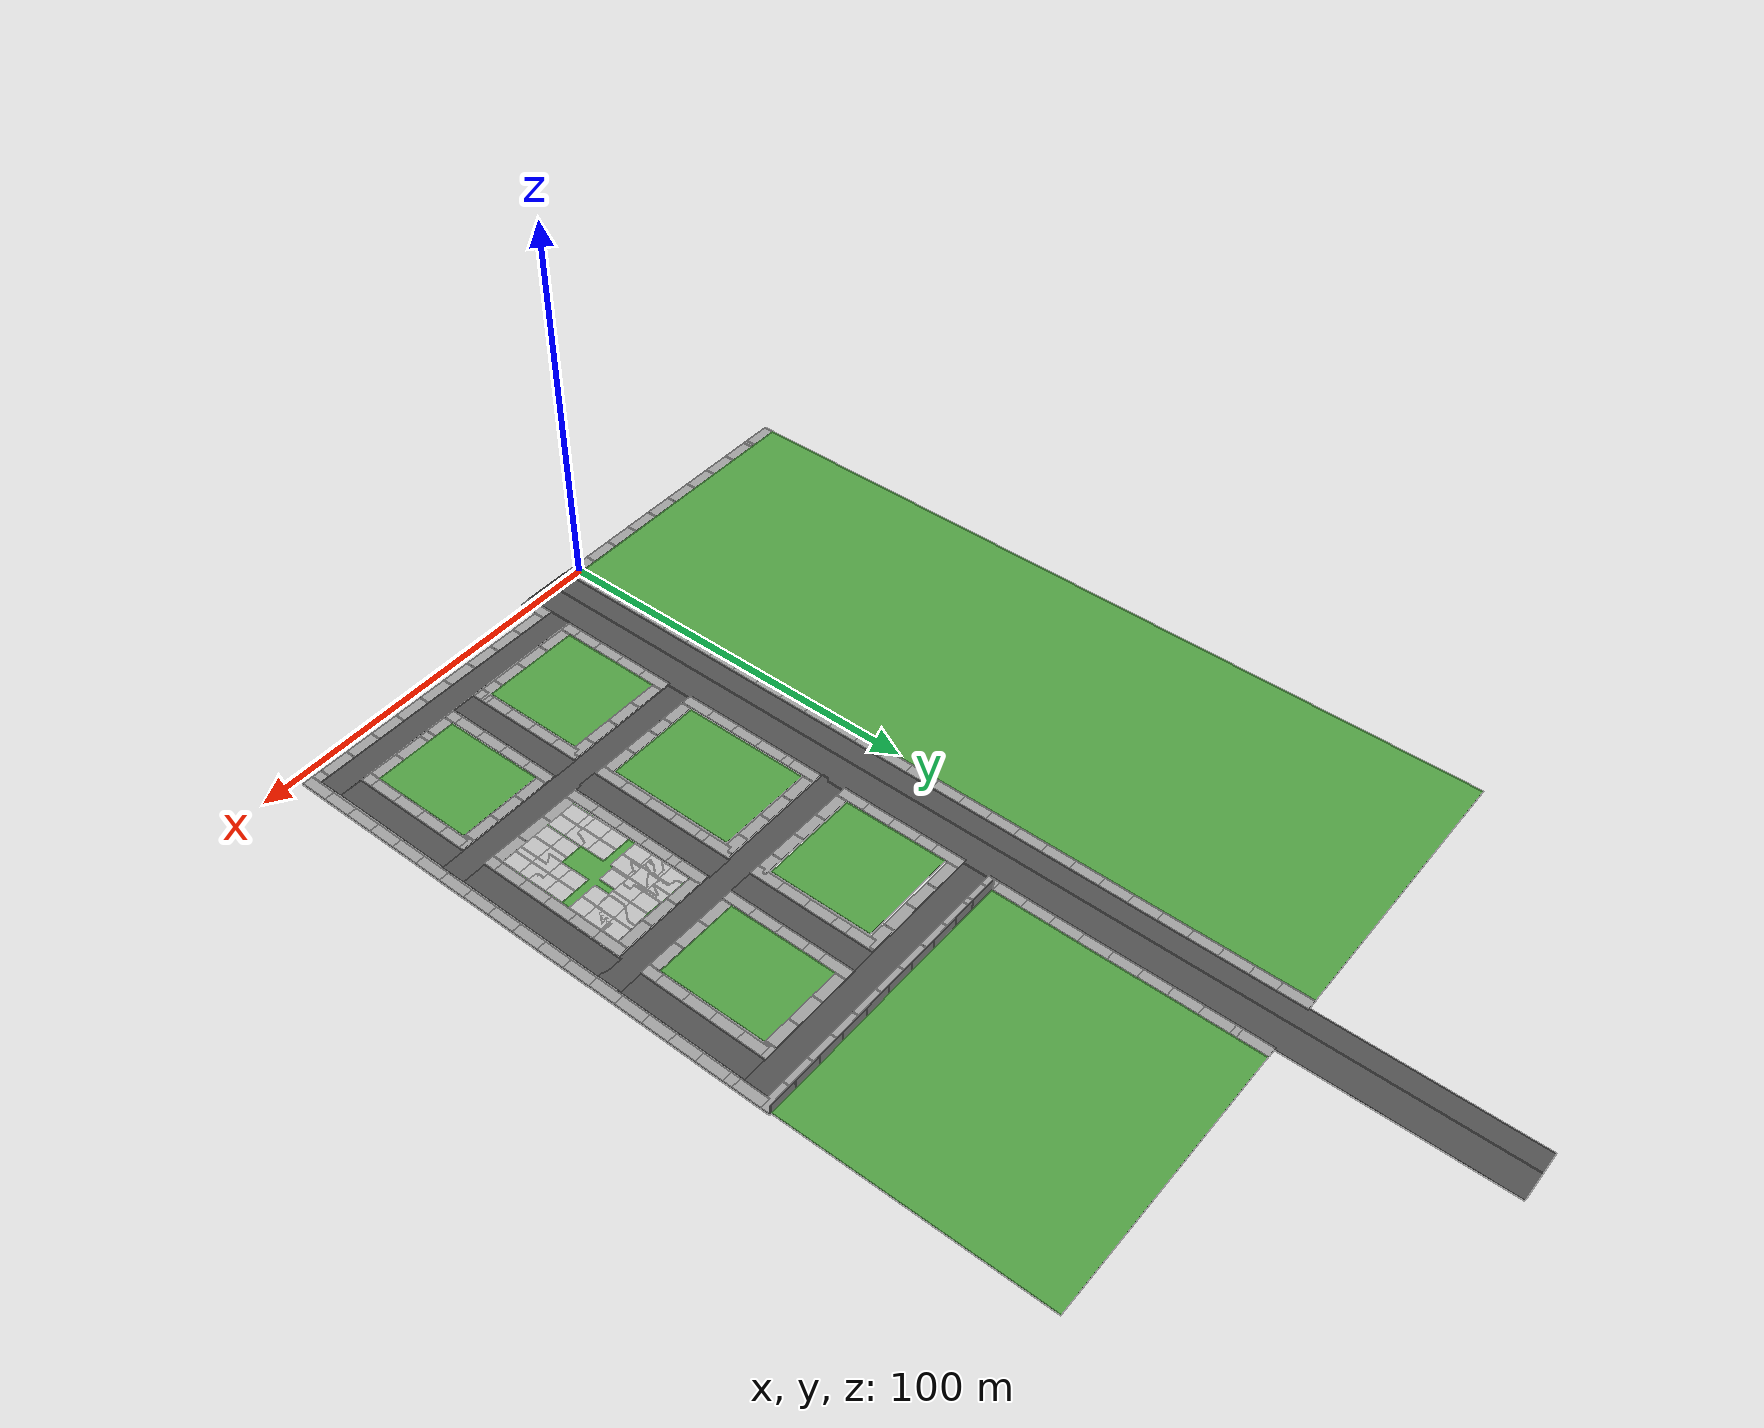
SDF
<sdf version="1.6">
 <world name="default">
  <spherical_coordinates>
   <latitude_deg>48.8789</latitude_deg>
   <longitude_deg>2.36778</longitude_deg>
   <surface_model>EARTH_WGS84</surface_model>
   <elevation>0</elevation>
   <heading_deg>0</heading_deg>
  </spherical_coordinates>
  <physics name="default_physics" default="0" type="ode">
   <real_time_update_rate>1000</real_time_update_rate>
   <max_step_size>0.001</max_step_size>
   <real_time_factor>1</real_time_factor>
   <max_contacts>20</max_contacts>
   <gravity>0 0 -9.81</gravity>
   <ode>
    <solver>
     <type>world</type>
     <min_step_size>0.0001</min_step_size>
     <iters>50</iters>
     <precon_iters>0</precon_iters>
     <sor>1.4</sor>
     <use_dynamic_moi_rescaling>1</use_dynamic_moi_rescaling>
    </solver>
    <constraints>
     <cfm>0</cfm>
     <erp>0.2</erp>
     <contact_max_correcting_vel>100</contact_max_correcting_vel>
     <contact_surface_layer>0.001</contact_surface_layer>
    </constraints>
   </ode>
  </physics>
  <atmosphere type="adiabatic">
   <temperature>298.15</temperature>
   <pressure>101325</pressure>
   <temperature_gradient>-0.0065</temperature_gradient>
  </atmosphere>
  <plugin name="fwman" filename="libsphinx_fwman.so">
   <spawn_point name="default"><pose>0 0 0.2 0 0 0</pose></spawn_point>
  </plugin>
  <plugin name="wind" filename="libsphinx_wind.so">
   <magnitude_mean>0.0</magnitude_mean>
   <direction_mean>0.0</direction_mean>
   <elevation_mean>0.0</elevation_mean>
   <magnitude_time_for_rise>10.0</magnitude_time_for_rise>
   <direction_time_for_rise>30.0</direction_time_for_rise>
   <elevation_time_for_rise>0.0</elevation_time_for_rise>
   <magnitude_expr>val*(1+0.05*sin(2*pi*time/15))</magnitude_expr>
   <direction_expr>360*time/60</direction_expr>
   <elevation_expr>0.03*noise()</elevation_expr>
  </plugin>
  <light name="sun" type="directional">
   <pose>0 0 10 0 -0 0</pose>
   <diffuse>0.8 0.8 0.8 1</diffuse>
   <specular>0.2 0.2 0.2 1</specular>
   <attenuation>
    <range>1000</range>
    <constant>0.9</constant>
    <linear>0.01</linear>
    <quadratic>0.001</quadratic>
   </attenuation>
   <direction>-0.5 0.1 -0.9</direction>
  </light>
  <gravity>0 0 -9.81</gravity>
  <magnetic_field>0 2.1e-05 -4.3e-05</magnetic_field>
  <scene><ambient>0.4 0.4 0.4 1</ambient><background>0.7 0.7 0.7 1</background><shadows>1</shadows></scene>
  <model name="grey_wall_clone">
   <static>1</static>
   <link name="link">
    <pose>0 0 1.4 0 -0 0</pose>
    <collision name="collision"><geometry><box><size>7.5 0.2 2.8</size></box></geometry></collision>
    <visual name="visual">
     <cast_shadows>0</cast_shadows>
     <geometry><box><size>7.5 0.2 2.8</size></box></geometry>
     <material>
      <script>
       <uri>model://grey_wall/materials/scripts</uri>
       <uri>model://grey_wall/materials/textures</uri>
       <name>vrc/grey_wall</name>
      </script>
     </material>
    </visual>
   </link>
   <pose>-1.20689 0.282178 -0.016498 -1.5862 0.002658 3.13547</pose>
  </model>
  <model name="Grass">
   <link name="link_0">
    <inertial>
     <mass>1393.09</mass>
     <inertia>
      <ixx>639346</ixx>
      <ixy>0</ixy>
      <ixz>0</ixz>
      <iyy>5.00315e+06</iyy>
      <iyz>0</iyz>
      <izz>5.64249e+06</izz>
     </inertia>
    </inertial>
    <pose>41.4488 69.2093 0 0 0 -1.57123</pose>
    <gravity>0</gravity>
    <self_collide>1</self_collide>
    <visual name="visual">
     <geometry><box><size>207.597 74.211 0.068473</size></box></geometry>
     <material>
      <lighting>1</lighting>
      <script><uri>file://media/materials/scripts/gazebo.material</uri><name>Gazebo/Grass</name></script>
      <shader type="vertex"><normal_map>__default__</normal_map></shader>
      <ambient>0.3 0.3 0.3 1</ambient>
      <diffuse>0.7 0.7 0.7 1</diffuse>
      <specular>0.01 0.01 0.01 1</specular>
      <emissive>0 0 0 1</emissive>
     </material>
    </visual>
    <collision name="collision_0">
     <geometry><box><size>207.597 74.211 0.068473</size></box></geometry>
     <surface>
      <friction>
       <ode><mu>1</mu><mu2>1</mu2><fdir1>0 0 0</fdir1><slip1>0</slip1><slip2>0</slip2></ode>
       <torsional>
        <coefficient>1</coefficient>
        <patch_radius>0</patch_radius>
        <surface_radius>0</surface_radius>
        <use_patch_radius>1</use_patch_radius>
        <ode><slip>0</slip></ode>
       </torsional>
      </friction>
      <bounce><restitution_coefficient>0</restitution_coefficient><threshold>1e+06</threshold></bounce>
      <contact>
       <collide_without_contact>0</collide_without_contact>
       <collide_without_contact_bitmask>1</collide_without_contact_bitmask>
       <collide_bitmask>1</collide_bitmask>
       <ode>
        <soft_cfm>0</soft_cfm>
        <soft_erp>0.2</soft_erp>
        <kp>1e+13</kp>
        <kd>1</kd>
        <max_vel>0.01</max_vel>
        <min_depth>0</min_depth>
       </ode>
       <bullet>
        <split_impulse>1</split_impulse>
        <split_impulse_penetration_threshold>-0.01</split_impulse_penetration_threshold>
        <soft_cfm>0</soft_cfm>
        <soft_erp>0.2</soft_erp>
        <kp>1e+13</kp>
        <kd>1</kd>
       </bullet>
      </contact>
     </surface>
    </collision>
   </link>
   <static>1</static>
   <pose>-77.1234 35.0147 0 0 -0 0</pose>
  </model>
  <model name="grey_wall_clone_clone">
   <static>1</static>
   <link name="link">
    <pose>0 0 1.4 0 -0 0</pose>
    <collision name="collision"><geometry><box><size>7.5 0.2 2.8</size></box></geometry></collision>
    <visual name="visual">
     <cast_shadows>0</cast_shadows>
     <geometry><box><size>7.5 0.2 2.8</size></box></geometry>
     <material>
      <script>
       <uri>model://grey_wall/materials/scripts</uri>
       <uri>model://grey_wall/materials/textures</uri>
       <name>vrc/grey_wall</name>
      </script>
     </material>
    </visual>
   </link>
   <pose>-8.68806 0.297918 -0.016498 -1.5862 0.002658 3.13547</pose>
  </model>
  <model name="grey_wall_clone_clone_0">
   <static>1</static>
   <link name="link">
    <pose>0 0 1.4 0 -0 0</pose>
    <collision name="collision"><geometry><box><size>7.5 0.2 2.8</size></box></geometry></collision>
    <visual name="visual">
     <cast_shadows>0</cast_shadows>
     <geometry><box><size>7.5 0.2 2.8</size></box></geometry>
     <material>
      <script>
       <uri>model://grey_wall/materials/scripts</uri>
       <uri>model://grey_wall/materials/textures</uri>
       <name>vrc/grey_wall</name>
      </script>
     </material>
    </visual>
   </link>
   <pose>-16.1629 0.317248 -0.016498 -1.5862 0.002658 3.13547</pose>
  </model>
  <model name="grey_wall_clone_clone_1">
   <static>1</static>
   <link name="link">
    <pose>0 0 1.4 0 -0 0</pose>
    <collision name="collision"><geometry><box><size>7.5 0.2 2.8</size></box></geometry></collision>
    <visual name="visual">
     <cast_shadows>0</cast_shadows>
     <geometry><box><size>7.5 0.2 2.8</size></box></geometry>
     <material>
      <script>
       <uri>model://grey_wall/materials/scripts</uri>
       <uri>model://grey_wall/materials/textures</uri>
       <name>vrc/grey_wall</name>
      </script>
     </material>
    </visual>
   </link>
   <pose>-23.6084 0.328788 -0.016498 -1.5862 0.002658 3.13547</pose>
  </model>
  <model name="grey_wall_clone_clone_2">
   <static>1</static>
   <link name="link">
    <pose>0 0 1.4 0 -0 0</pose>
    <collision name="collision"><geometry><box><size>7.5 0.2 2.8</size></box></geometry></collision>
    <visual name="visual">
     <cast_shadows>0</cast_shadows>
     <geometry><box><size>7.5 0.2 2.8</size></box></geometry>
     <material>
      <script>
       <uri>model://grey_wall/materials/scripts</uri>
       <uri>model://grey_wall/materials/textures</uri>
       <name>vrc/grey_wall</name>
      </script>
     </material>
    </visual>
   </link>
   <pose>-31.0663 0.368188 -0.016498 -1.5862 0.002658 3.13547</pose>
  </model>
  <model name="grey_wall_clone_clone_3">
   <static>1</static>
   <link name="link">
    <pose>0 0 1.4 0 -0 0</pose>
    <collision name="collision"><geometry><box><size>7.5 0.2 2.8</size></box></geometry></collision>
    <visual name="visual">
     <cast_shadows>0</cast_shadows>
     <geometry><box><size>7.5 0.2 2.8</size></box></geometry>
     <material>
      <script>
       <uri>model://grey_wall/materials/scripts</uri>
       <uri>model://grey_wall/materials/textures</uri>
       <name>vrc/grey_wall</name>
      </script>
     </material>
    </visual>
   </link>
   <pose>-38.4619 0.420228 -0.016498 -1.5862 0.002658 3.13547</pose>
  </model>
  <model name="grey_wall_clone_clone_4">
   <static>1</static>
   <link name="link">
    <pose>0 0 1.4 0 -0 0</pose>
    <collision name="collision"><geometry><box><size>7.5 0.2 2.8</size></box></geometry></collision>
    <visual name="visual">
     <cast_shadows>0</cast_shadows>
     <geometry><box><size>7.5 0.2 2.8</size></box></geometry>
     <material>
      <script>
       <uri>model://grey_wall/materials/scripts</uri>
       <uri>model://grey_wall/materials/textures</uri>
       <name>vrc/grey_wall</name>
      </script>
     </material>
    </visual>
   </link>
   <pose>-45.7935 0.470214 -0.016498 -1.5862 0.002658 3.13547</pose>
  </model>
  <model name="grey_wall_clone_clone_5">
   <static>1</static>
   <link name="link">
    <pose>0 0 1.4 0 -0 0</pose>
    <collision name="collision"><geometry><box><size>7.5 0.2 2.8</size></box></geometry></collision>
    <visual name="visual">
     <cast_shadows>0</cast_shadows>
     <geometry><box><size>7.5 0.2 2.8</size></box></geometry>
     <material>
      <script>
       <uri>model://grey_wall/materials/scripts</uri>
       <uri>model://grey_wall/materials/textures</uri>
       <name>vrc/grey_wall</name>
      </script>
     </material>
    </visual>
   </link>
   <pose>-53.2131 0.521137 -0.016498 -1.5862 0.002658 3.13547</pose>
  </model>
  <model name="grey_wall_clone_clone_6">
   <static>1</static>
   <link name="link">
    <pose>0 0 1.4 0 -0 0</pose>
    <collision name="collision"><geometry><box><size>7.5 0.2 2.8</size></box></geometry></collision>
    <visual name="visual">
     <cast_shadows>0</cast_shadows>
     <geometry><box><size>7.5 0.2 2.8</size></box></geometry>
     <material>
      <script>
       <uri>model://grey_wall/materials/scripts</uri>
       <uri>model://grey_wall/materials/textures</uri>
       <name>vrc/grey_wall</name>
      </script>
     </material>
    </visual>
   </link>
   <pose>-60.7192 0.56687 -0.016498 -1.5862 0.002658 3.13547</pose>
  </model>
  <model name="grey_wall_clone_clone_7">
   <static>1</static>
   <link name="link">
    <pose>0 0 1.4 0 -0 0</pose>
    <collision name="collision"><geometry><box><size>7.5 0.2 2.8</size></box></geometry></collision>
    <visual name="visual">
     <cast_shadows>0</cast_shadows>
     <geometry><box><size>7.5 0.2 2.8</size></box></geometry>
     <material>
      <script>
       <uri>model://grey_wall/materials/scripts</uri>
       <uri>model://grey_wall/materials/textures</uri>
       <name>vrc/grey_wall</name>
      </script>
     </material>
    </visual>
   </link>
   <pose>-68.0673 0.620468 -0.016498 -1.5862 0.002658 3.13547</pose>
  </model>
  <model name="grey_wall_clone_clone_8">
   <static>1</static>
   <link name="link">
    <pose>0 0 1.4 0 -0 0</pose>
    <collision name="collision"><geometry><box><size>7.5 0.2 2.8</size></box></geometry></collision>
    <visual name="visual">
     <cast_shadows>0</cast_shadows>
     <geometry><box><size>7.5 0.2 2.8</size></box></geometry>
     <material>
      <script>
       <uri>model://grey_wall/materials/scripts</uri>
       <uri>model://grey_wall/materials/textures</uri>
       <name>vrc/grey_wall</name>
      </script>
     </material>
    </visual>
   </link>
   <pose>-69.1277 0.631045 -0.012312 -1.5862 0.002658 3.13547</pose>
  </model>
  <model name="grey_wall_clone_clone_9">
   <static>1</static>
   <link name="link">
    <pose>0 0 1.4 0 -0 0</pose>
    <collision name="collision"><geometry><box><size>7.5 0.2 2.8</size></box></geometry></collision>
    <visual name="visual">
     <cast_shadows>0</cast_shadows>
     <geometry><box><size>7.5 0.2 2.8</size></box></geometry>
     <material>
      <script>
       <uri>model://grey_wall/materials/scripts</uri>
       <uri>model://grey_wall/materials/textures</uri>
       <name>vrc/grey_wall</name>
      </script>
     </material>
    </visual>
   </link>
   <pose>2.599 4.01474 -0.016998 -1.57343 0.001892 1.56332</pose>
  </model>
  <model name="grey_wall_clone_clone_9_clone">
   <static>1</static>
   <link name="link">
    <pose>0 0 1.4 0 -0 0</pose>
    <collision name="collision"><geometry><box><size>7.5 0.2 2.8</size></box></geometry></collision>
    <visual name="visual">
     <cast_shadows>0</cast_shadows>
     <geometry><box><size>7.5 0.2 2.8</size></box></geometry>
     <material>
      <script>
       <uri>model://grey_wall/materials/scripts</uri>
       <uri>model://grey_wall/materials/textures</uri>
       <name>vrc/grey_wall</name>
      </script>
     </material>
    </visual>
   </link>
   <pose>2.65569 11.4997 -0.016993 -1.57343 0.001892 1.56332</pose>
  </model>
  <model name="grey_wall_clone_clone_9_clone_0">
   <static>1</static>
   <link name="link">
    <pose>0 0 1.4 0 -0 0</pose>
    <collision name="collision"><geometry><box><size>7.5 0.2 2.8</size></box></geometry></collision>
    <visual name="visual">
     <cast_shadows>0</cast_shadows>
     <geometry><box><size>7.5 0.2 2.8</size></box></geometry>
     <material>
      <script>
       <uri>model://grey_wall/materials/scripts</uri>
       <uri>model://grey_wall/materials/textures</uri>
       <name>vrc/grey_wall</name>
      </script>
     </material>
    </visual>
   </link>
   <pose>2.70398 18.9263 -0.016993 -1.57343 0.001892 1.56332</pose>
  </model>
  <model name="grey_wall_clone_clone_9_clone_1">
   <static>1</static>
   <link name="link">
    <pose>0 0 1.4 0 -0 0</pose>
    <collision name="collision"><geometry><box><size>7.5 0.2 2.8</size></box></geometry></collision>
    <visual name="visual">
     <cast_shadows>0</cast_shadows>
     <geometry><box><size>7.5 0.2 2.8</size></box></geometry>
     <material>
      <script>
       <uri>model://grey_wall/materials/scripts</uri>
       <uri>model://grey_wall/materials/textures</uri>
       <name>vrc/grey_wall</name>
      </script>
     </material>
    </visual>
   </link>
   <pose>2.73693 26.4458 -0.01692 -1.57343 0.001892 1.56332</pose>
  </model>
  <model name="grey_wall_clone_clone_9_clone_2">
   <static>1</static>
   <link name="link">
    <pose>0 0 1.4 0 -0 0</pose>
    <collision name="collision"><geometry><box><size>7.5 0.2 2.8</size></box></geometry></collision>
    <visual name="visual">
     <cast_shadows>0</cast_shadows>
     <geometry><box><size>7.5 0.2 2.8</size></box></geometry>
     <material>
      <script>
       <uri>model://grey_wall/materials/scripts</uri>
       <uri>model://grey_wall/materials/textures</uri>
       <name>vrc/grey_wall</name>
      </script>
     </material>
    </visual>
   </link>
   <pose>2.82767 33.8561 -0.016993 -1.57343 0.001892 1.56332</pose>
  </model>
  <model name="grey_wall_clone_clone_9_clone_3">
   <static>1</static>
   <link name="link">
    <pose>0 0 1.4 0 -0 0</pose>
    <collision name="collision"><geometry><box><size>7.5 0.2 2.8</size></box></geometry></collision>
    <visual name="visual">
     <cast_shadows>0</cast_shadows>
     <geometry><box><size>7.5 0.2 2.8</size></box></geometry>
     <material>
      <script>
       <uri>model://grey_wall/materials/scripts</uri>
       <uri>model://grey_wall/materials/textures</uri>
       <name>vrc/grey_wall</name>
      </script>
     </material>
    </visual>
   </link>
   <pose>2.88818 41.3325 -0.016993 -1.57343 0.001892 1.56332</pose>
  </model>
  <model name="grey_wall_clone_clone_9_clone_4">
   <static>1</static>
   <link name="link">
    <pose>0 0 1.4 0 -0 0</pose>
    <collision name="collision"><geometry><box><size>7.5 0.2 2.8</size></box></geometry></collision>
    <visual name="visual">
     <cast_shadows>0</cast_shadows>
     <geometry><box><size>7.5 0.2 2.8</size></box></geometry>
     <material>
      <script>
       <uri>model://grey_wall/materials/scripts</uri>
       <uri>model://grey_wall/materials/textures</uri>
       <name>vrc/grey_wall</name>
      </script>
     </material>
    </visual>
   </link>
   <pose>2.94309 48.7292 -0.016993 -1.57343 0.001892 1.56332</pose>
  </model>
  <model name="grey_wall_clone_clone_9_clone_5">
   <static>1</static>
   <link name="link">
    <pose>0 0 1.4 0 -0 0</pose>
    <collision name="collision"><geometry><box><size>7.5 0.2 2.8</size></box></geometry></collision>
    <visual name="visual">
     <cast_shadows>0</cast_shadows>
     <geometry><box><size>7.5 0.2 2.8</size></box></geometry>
     <material>
      <script>
       <uri>model://grey_wall/materials/scripts</uri>
       <uri>model://grey_wall/materials/textures</uri>
       <name>vrc/grey_wall</name>
      </script>
     </material>
    </visual>
   </link>
   <pose>3.00389 56.2219 -0.016993 -1.57343 0.001892 1.56332</pose>
  </model>
  <model name="grey_wall_clone_clone_9_clone_6">
   <static>1</static>
   <link name="link">
    <pose>0 0 1.4 0 -0 0</pose>
    <collision name="collision"><geometry><box><size>7.5 0.2 2.8</size></box></geometry></collision>
    <visual name="visual">
     <cast_shadows>0</cast_shadows>
     <geometry><box><size>7.5 0.2 2.8</size></box></geometry>
     <material>
      <script>
       <uri>model://grey_wall/materials/scripts</uri>
       <uri>model://grey_wall/materials/textures</uri>
       <name>vrc/grey_wall</name>
      </script>
     </material>
    </visual>
   </link>
   <pose>3.05758 63.3006 -0.016993 -1.57343 0.001892 1.56332</pose>
  </model>
  <model name="grey_wall_clone_clone_9_clone_7">
   <static>1</static>
   <link name="link">
    <pose>0 0 1.4 0 -0 0</pose>
    <collision name="collision"><geometry><box><size>7.5 0.2 2.8</size></box></geometry></collision>
    <visual name="visual">
     <cast_shadows>0</cast_shadows>
     <geometry><box><size>7.5 0.2 2.8</size></box></geometry>
     <material>
      <script>
       <uri>model://grey_wall/materials/scripts</uri>
       <uri>model://grey_wall/materials/textures</uri>
       <name>vrc/grey_wall</name>
      </script>
     </material>
    </visual>
   </link>
   <pose>3.09587 70.7495 -0.016993 -1.57343 0.001892 1.56332</pose>
  </model>
  <model name="grey_wall_clone_clone_9_clone_8">
   <static>1</static>
   <link name="link">
    <pose>0 0 1.4 0 -0 0</pose>
    <collision name="collision"><geometry><box><size>7.5 0.2 2.8</size></box></geometry></collision>
    <visual name="visual">
     <cast_shadows>0</cast_shadows>
     <geometry><box><size>7.5 0.2 2.8</size></box></geometry>
     <material>
      <script>
       <uri>model://grey_wall/materials/scripts</uri>
       <uri>model://grey_wall/materials/textures</uri>
       <name>vrc/grey_wall</name>
      </script>
     </material>
    </visual>
   </link>
   <pose>3.15713 78.2163 -0.016993 -1.57343 0.001892 1.56332</pose>
  </model>
  <model name="grey_wall_clone_clone_9_clone_9">
   <static>1</static>
   <link name="link">
    <pose>0 0 1.4 0 -0 0</pose>
    <collision name="collision"><geometry><box><size>7.5 0.2 2.8</size></box></geometry></collision>
    <visual name="visual">
     <cast_shadows>0</cast_shadows>
     <geometry><box><size>7.5 0.2 2.8</size></box></geometry>
     <material>
      <script>
       <uri>model://grey_wall/materials/scripts</uri>
       <uri>model://grey_wall/materials/textures</uri>
       <name>vrc/grey_wall</name>
      </script>
     </material>
    </visual>
   </link>
   <pose>3.19599 85.6747 -0.016993 -1.57343 0.001892 1.56332</pose>
  </model>
  <model name="grey_wall_clone_clone_9_clone_10">
   <static>1</static>
   <link name="link">
    <pose>0 0 1.4 0 -0 0</pose>
    <collision name="collision"><geometry><box><size>7.5 0.2 2.8</size></box></geometry></collision>
    <visual name="visual">
     <cast_shadows>0</cast_shadows>
     <geometry><box><size>7.5 0.2 2.8</size></box></geometry>
     <material>
      <script>
       <uri>model://grey_wall/materials/scripts</uri>
       <uri>model://grey_wall/materials/textures</uri>
       <name>vrc/grey_wall</name>
      </script>
     </material>
    </visual>
   </link>
   <pose>3.27466 93.1318 -0.016993 -1.57343 0.001892 1.56332</pose>
  </model>
  <model name="grey_wall_clone_clone_9_clone_11">
   <static>1</static>
   <link name="link">
    <pose>0 0 1.4 0 -0 0</pose>
    <collision name="collision"><geometry><box><size>7.5 0.2 2.8</size></box></geometry></collision>
    <visual name="visual">
     <cast_shadows>0</cast_shadows>
     <geometry><box><size>7.5 0.2 2.8</size></box></geometry>
     <material>
      <script>
       <uri>model://grey_wall/materials/scripts</uri>
       <uri>model://grey_wall/materials/textures</uri>
       <name>vrc/grey_wall</name>
      </script>
     </material>
    </visual>
   </link>
   <pose>3.34177 100.585 -0.016993 -1.57343 0.001892 1.56332</pose>
  </model>
  <model name="grey_wall_clone_clone_9_clone_12">
   <static>1</static>
   <link name="link">
    <pose>0 0 1.4 0 -0 0</pose>
    <collision name="collision"><geometry><box><size>7.5 0.2 2.8</size></box></geometry></collision>
    <visual name="visual">
     <cast_shadows>0</cast_shadows>
     <geometry><box><size>7.5 0.2 2.8</size></box></geometry>
     <material>
      <script>
       <uri>model://grey_wall/materials/scripts</uri>
       <uri>model://grey_wall/materials/textures</uri>
       <name>vrc/grey_wall</name>
      </script>
     </material>
    </visual>
   </link>
   <pose>3.37904 108.071 -0.016993 -1.57343 0.001892 1.56332</pose>
  </model>
  <model name="grey_wall_clone_clone_9_clone_13">
   <static>1</static>
   <link name="link">
    <pose>0 0 1.4 0 -0 0</pose>
    <collision name="collision"><geometry><box><size>7.5 0.2 2.8</size></box></geometry></collision>
    <visual name="visual">
     <cast_shadows>0</cast_shadows>
     <geometry><box><size>7.5 0.2 2.8</size></box></geometry>
     <material>
      <script>
       <uri>model://grey_wall/materials/scripts</uri>
       <uri>model://grey_wall/materials/textures</uri>
       <name>vrc/grey_wall</name>
      </script>
     </material>
    </visual>
   </link>
   <pose>3.43038 115.536 -0.016993 -1.57343 0.001892 1.56332</pose>
  </model>
  <model name="grey_wall_clone_clone_9_clone_14">
   <static>1</static>
   <link name="link">
    <pose>0 0 1.4 0 -0 0</pose>
    <collision name="collision"><geometry><box><size>7.5 0.2 2.8</size></box></geometry></collision>
    <visual name="visual">
     <cast_shadows>0</cast_shadows>
     <geometry><box><size>7.5 0.2 2.8</size></box></geometry>
     <material>
      <script>
       <uri>model://grey_wall/materials/scripts</uri>
       <uri>model://grey_wall/materials/textures</uri>
       <name>vrc/grey_wall</name>
      </script>
     </material>
    </visual>
   </link>
   <pose>3.47192 123.01 -0.016993 -1.57343 0.001892 1.56332</pose>
  </model>
  <model name="grey_wall_clone_clone_9_clone_15">
   <static>1</static>
   <link name="link">
    <pose>0 0 1.4 0 -0 0</pose>
    <collision name="collision"><geometry><box><size>7.5 0.2 2.8</size></box></geometry></collision>
    <visual name="visual">
     <cast_shadows>0</cast_shadows>
     <geometry><box><size>7.5 0.2 2.8</size></box></geometry>
     <material>
      <script>
       <uri>model://grey_wall/materials/scripts</uri>
       <uri>model://grey_wall/materials/textures</uri>
       <name>vrc/grey_wall</name>
      </script>
     </material>
    </visual>
   </link>
   <pose>3.51541 130.459 -0.016993 -1.57343 0.001892 1.56332</pose>
  </model>
  <model name="grey_wall_clone_clone_9_clone_16">
   <static>1</static>
   <link name="link">
    <pose>0 0 1.4 0 -0 0</pose>
    <collision name="collision"><geometry><box><size>7.5 0.2 2.8</size></box></geometry></collision>
    <visual name="visual">
     <cast_shadows>0</cast_shadows>
     <geometry><box><size>7.5 0.2 2.8</size></box></geometry>
     <material>
      <script>
       <uri>model://grey_wall/materials/scripts</uri>
       <uri>model://grey_wall/materials/textures</uri>
       <name>vrc/grey_wall</name>
      </script>
     </material>
    </visual>
   </link>
   <pose>3.58315 137.961 -0.016993 -1.57343 0.001892 1.56332</pose>
  </model>
  <model name="grey_wall_clone_clone_9_clone_17">
   <static>1</static>
   <link name="link">
    <pose>0 0 1.4 0 -0 0</pose>
    <collision name="collision"><geometry><box><size>7.5 0.2 2.8</size></box></geometry></collision>
    <visual name="visual">
     <cast_shadows>0</cast_shadows>
     <geometry><box><size>7.5 0.2 2.8</size></box></geometry>
     <material>
      <script>
       <uri>model://grey_wall/materials/scripts</uri>
       <uri>model://grey_wall/materials/textures</uri>
       <name>vrc/grey_wall</name>
      </script>
     </material>
    </visual>
   </link>
   <pose>3.64485 145.448 -0.016993 -1.57343 0.001892 1.56332</pose>
  </model>
  <model name="grey_wall_clone_clone_9_clone_18">
   <static>1</static>
   <link name="link">
    <pose>0 0 1.4 0 -0 0</pose>
    <collision name="collision"><geometry><box><size>7.5 0.2 2.8</size></box></geometry></collision>
    <visual name="visual">
     <cast_shadows>0</cast_shadows>
     <geometry><box><size>7.5 0.2 2.8</size></box></geometry>
     <material>
      <script>
       <uri>model://grey_wall/materials/scripts</uri>
       <uri>model://grey_wall/materials/textures</uri>
       <name>vrc/grey_wall</name>
      </script>
     </material>
    </visual>
   </link>
   <pose>3.71423 152.905 -0.016993 -1.57343 0.001892 1.56332</pose>
  </model>
  <model name="grey_wall_clone_clone_9_clone_19">
   <static>1</static>
   <link name="link">
    <pose>0 0 1.4 0 -0 0</pose>
    <collision name="collision"><geometry><box><size>7.5 0.2 2.8</size></box></geometry></collision>
    <visual name="visual">
     <cast_shadows>0</cast_shadows>
     <geometry><box><size>7.5 0.2 2.8</size></box></geometry>
     <material>
      <script>
       <uri>model://grey_wall/materials/scripts</uri>
       <uri>model://grey_wall/materials/textures</uri>
       <name>vrc/grey_wall</name>
      </script>
     </material>
    </visual>
   </link>
   <pose>3.78725 160.34 -0.016993 -1.57343 0.001892 1.56332</pose>
  </model>
  <model name="grey_wall_clone_clone_9_clone_20">
   <static>1</static>
   <link name="link">
    <pose>0 0 1.4 0 -0 0</pose>
    <collision name="collision"><geometry><box><size>7.5 0.2 2.8</size></box></geometry></collision>
    <visual name="visual">
     <cast_shadows>0</cast_shadows>
     <geometry><box><size>7.5 0.2 2.8</size></box></geometry>
     <material>
      <script>
       <uri>model://grey_wall/materials/scripts</uri>
       <uri>model://grey_wall/materials/textures</uri>
       <name>vrc/grey_wall</name>
      </script>
     </material>
    </visual>
   </link>
   <pose>3.87527 167.804 -0.016993 -1.57343 0.001892 1.56332</pose>
  </model>
  <model name="grey_wall_clone_clone_9_clone_21">
   <static>1</static>
   <link name="link">
    <pose>0 0 1.4 0 -0 0</pose>
    <collision name="collision"><geometry><box><size>7.5 0.2 2.8</size></box></geometry></collision>
    <visual name="visual">
     <cast_shadows>0</cast_shadows>
     <geometry><box><size>7.5 0.2 2.8</size></box></geometry>
     <material>
      <script>
       <uri>model://grey_wall/materials/scripts</uri>
       <uri>model://grey_wall/materials/textures</uri>
       <name>vrc/grey_wall</name>
      </script>
     </material>
    </visual>
   </link>
   <pose>3.93042 175.282 -0.016993 -1.57343 0.001892 1.56332</pose>
  </model>
  <model name="grey_wall_clone_clone_9_clone_22">
   <static>1</static>
   <link name="link">
    <pose>0 0 1.4 0 -0 0</pose>
    <collision name="collision"><geometry><box><size>7.5 0.2 2.8</size></box></geometry></collision>
    <visual name="visual">
     <cast_shadows>0</cast_shadows>
     <geometry><box><size>7.5 0.2 2.8</size></box></geometry>
     <material>
      <script>
       <uri>model://grey_wall/materials/scripts</uri>
       <uri>model://grey_wall/materials/textures</uri>
       <name>vrc/grey_wall</name>
      </script>
     </material>
    </visual>
   </link>
   <pose>3.96067 182.755 -0.016993 -1.57343 0.001892 1.56332</pose>
  </model>
  <model name="grey_wall_clone_clone_9_clone_23">
   <static>1</static>
   <link name="link">
    <pose>0 0 1.4 0 -0 0</pose>
    <collision name="collision"><geometry><box><size>7.5 0.2 2.8</size></box></geometry></collision>
    <visual name="visual">
     <cast_shadows>0</cast_shadows>
     <geometry><box><size>7.5 0.2 2.8</size></box></geometry>
     <material>
      <script>
       <uri>model://grey_wall/materials/scripts</uri>
       <uri>model://grey_wall/materials/textures</uri>
       <name>vrc/grey_wall</name>
      </script>
     </material>
    </visual>
   </link>
   <pose>4.02602 190.245 -0.016993 -1.57343 0.001892 1.56332</pose>
  </model>
  <model name="grey_wall_clone_clone_9_clone_24">
   <static>1</static>
   <link name="link">
    <pose>0 0 1.4 0 -0 0</pose>
    <collision name="collision"><geometry><box><size>7.5 0.2 2.8</size></box></geometry></collision>
    <visual name="visual">
     <cast_shadows>0</cast_shadows>
     <geometry><box><size>7.5 0.2 2.8</size></box></geometry>
     <material>
      <script>
       <uri>model://grey_wall/materials/scripts</uri>
       <uri>model://grey_wall/materials/textures</uri>
       <name>vrc/grey_wall</name>
      </script>
     </material>
    </visual>
   </link>
   <pose>4.10089 197.661 -0.016993 -1.57343 0.001892 1.56332</pose>
  </model>
  <model name="grey_wall_clone_clone_9_clone_25">
   <static>1</static>
   <link name="link">
    <pose>0 0 1.4 0 -0 0</pose>
    <collision name="collision"><geometry><box><size>7.5 0.2 2.8</size></box></geometry></collision>
    <visual name="visual">
     <cast_shadows>0</cast_shadows>
     <geometry><box><size>7.5 0.2 2.8</size></box></geometry>
     <material>
      <script>
       <uri>model://grey_wall/materials/scripts</uri>
       <uri>model://grey_wall/materials/textures</uri>
       <name>vrc/grey_wall</name>
      </script>
     </material>
    </visual>
   </link>
   <pose>4.13179 204.265 -0.016993 -1.57343 0.001892 1.56332</pose>
  </model>
  <model name="grey_wall_clone_clone_10">
   <static>1</static>
   <link name="link">
    <pose>0 0 1.4 0 -0 0</pose>
    <collision name="collision"><geometry><box><size>7.5 0.2 2.8</size></box></geometry></collision>
    <visual name="visual">
     <cast_shadows>0</cast_shadows>
     <geometry><box><size>7.5 0.2 2.8</size></box></geometry>
     <material>
      <script>
       <uri>model://grey_wall/materials/scripts</uri>
       <uri>model://grey_wall/materials/textures</uri>
       <name>vrc/grey_wall</name>
      </script>
     </material>
    </visual>
   </link>
   <pose>21.7064 4.98903 -0.013396 -1.5862 0.002658 3.13547</pose>
  </model>
  <model name="grey_wall_clone_clone_9_clone_26">
   <static>1</static>
   <link name="link">
    <pose>0 0 1.4 0 -0 0</pose>
    <collision name="collision"><geometry><box><size>7.5 0.2 2.8</size></box></geometry></collision>
    <visual name="visual">
     <cast_shadows>0</cast_shadows>
     <geometry><box><size>7.5 0.2 2.8</size></box></geometry>
     <material>
      <script>
       <uri>model://grey_wall/materials/scripts</uri>
       <uri>model://grey_wall/materials/textures</uri>
       <name>vrc/grey_wall</name>
      </script>
     </material>
    </visual>
   </link>
   <pose>17.9158 1.22551 -0.017166 -1.57343 0.001892 1.56332</pose>
  </model>
  <model name="grey_wall_clone_clone_10_clone">
   <static>1</static>
   <link name="link">
    <pose>0 0 1.4 0 -0 0</pose>
    <collision name="collision"><geometry><box><size>7.5 0.2 2.8</size></box></geometry></collision>
    <visual name="visual">
     <cast_shadows>0</cast_shadows>
     <geometry><box><size>7.5 0.2 2.8</size></box></geometry>
     <material>
      <script>
       <uri>model://grey_wall/materials/scripts</uri>
       <uri>model://grey_wall/materials/textures</uri>
       <name>vrc/grey_wall</name>
      </script>
     </material>
    </visual>
   </link>
   <pose>29.2163 4.97085 -0.013115 -1.5862 0.002658 3.13547</pose>
  </model>
  <model name="grey_wall_clone_clone_10_clone_0">
   <static>1</static>
   <link name="link">
    <pose>0 0 1.4 0 -0 0</pose>
    <collision name="collision"><geometry><box><size>7.5 0.2 2.8</size></box></geometry></collision>
    <visual name="visual">
     <cast_shadows>0</cast_shadows>
     <geometry><box><size>7.5 0.2 2.8</size></box></geometry>
     <material>
      <script>
       <uri>model://grey_wall/materials/scripts</uri>
       <uri>model://grey_wall/materials/textures</uri>
       <name>vrc/grey_wall</name>
      </script>
     </material>
    </visual>
   </link>
   <pose>36.7163 4.92179 -0.013076 -1.5862 0.002658 3.13547</pose>
  </model>
  <model name="grey_wall_clone_clone_10_clone_1">
   <static>1</static>
   <link name="link">
    <pose>0 0 1.4 0 -0 0</pose>
    <collision name="collision"><geometry><box><size>7.5 0.2 2.8</size></box></geometry></collision>
    <visual name="visual">
     <cast_shadows>0</cast_shadows>
     <geometry><box><size>7.5 0.2 2.8</size></box></geometry>
     <material>
      <script>
       <uri>model://grey_wall/materials/scripts</uri>
       <uri>model://grey_wall/materials/textures</uri>
       <name>vrc/grey_wall</name>
      </script>
     </material>
    </visual>
   </link>
   <pose>44.1707 4.85128 -0.01475 -1.5862 0.002658 3.13547</pose>
  </model>
  <model name="grey_wall_clone_clone_10_clone_2">
   <static>1</static>
   <link name="link">
    <pose>0 0 1.4 0 -0 0</pose>
    <collision name="collision"><geometry><box><size>7.5 0.2 2.8</size></box></geometry></collision>
    <visual name="visual">
     <cast_shadows>0</cast_shadows>
     <geometry><box><size>7.5 0.2 2.8</size></box></geometry>
     <material>
      <script>
       <uri>model://grey_wall/materials/scripts</uri>
       <uri>model://grey_wall/materials/textures</uri>
       <name>vrc/grey_wall</name>
      </script>
     </material>
    </visual>
   </link>
   <pose>51.6181 4.83221 -0.013794 -1.5862 0.002658 3.13547</pose>
  </model>
  <model name="grey_wall_clone_clone_10_clone_3">
   <static>1</static>
   <link name="link">
    <pose>0 0 1.4 0 -0 0</pose>
    <collision name="collision"><geometry><box><size>7.5 0.2 2.8</size></box></geometry></collision>
    <visual name="visual">
     <cast_shadows>0</cast_shadows>
     <geometry><box><size>7.5 0.2 2.8</size></box></geometry>
     <material>
      <script>
       <uri>model://grey_wall/materials/scripts</uri>
       <uri>model://grey_wall/materials/textures</uri>
       <name>vrc/grey_wall</name>
      </script>
     </material>
    </visual>
   </link>
   <pose>59.1382 4.80138 -0.016498 -1.5862 0.002658 3.13547</pose>
  </model>
  <model name="grey_wall_clone_clone_10_clone_3_clone">
   <static>1</static>
   <link name="link">
    <pose>0 0 1.4 0 -0 0</pose>
    <collision name="collision"><geometry><box><size>7.5 0.2 2.8</size></box></geometry></collision>
    <visual name="visual">
     <cast_shadows>0</cast_shadows>
     <geometry><box><size>7.5 0.2 2.8</size></box></geometry>
     <material>
      <script>
       <uri>model://grey_wall/materials/scripts</uri>
       <uri>model://grey_wall/materials/textures</uri>
       <name>vrc/grey_wall</name>
      </script>
     </material>
    </visual>
   </link>
   <pose>66.6247 4.78706 -0.016498 -1.5862 0.002658 3.13547</pose>
  </model>
  <model name="grey_wall_clone_clone_10_clone_3_clone_0">
   <static>1</static>
   <link name="link">
    <pose>0 0 1.4 0 -0 0</pose>
    <collision name="collision"><geometry><box><size>7.5 0.2 2.8</size></box></geometry></collision>
    <visual name="visual">
     <cast_shadows>0</cast_shadows>
     <geometry><box><size>7.5 0.2 2.8</size></box></geometry>
     <material>
      <script>
       <uri>model://grey_wall/materials/scripts</uri>
       <uri>model://grey_wall/materials/textures</uri>
       <name>vrc/grey_wall</name>
      </script>
     </material>
    </visual>
   </link>
   <pose>74.0722 4.73995 -0.016498 -1.5862 0.002658 3.13547</pose>
  </model>
  <model name="grey_wall_clone_clone_10_clone_3_clone_1">
   <static>1</static>
   <link name="link">
    <pose>0 0 1.4 0 -0 0</pose>
    <collision name="collision"><geometry><box><size>7.5 0.2 2.8</size></box></geometry></collision>
    <visual name="visual">
     <cast_shadows>0</cast_shadows>
     <geometry><box><size>7.5 0.2 2.8</size></box></geometry>
     <material>
      <script>
       <uri>model://grey_wall/materials/scripts</uri>
       <uri>model://grey_wall/materials/textures</uri>
       <name>vrc/grey_wall</name>
      </script>
     </material>
    </visual>
   </link>
   <pose>81.5711 4.6927 -0.016498 -1.5862 0.002658 3.13547</pose>
  </model>
  <model name="grey_wall_clone_clone_10_clone_3_clone_1_clone">
   <static>1</static>
   <link name="link">
    <pose>0 0 1.4 0 -0 0</pose>
    <collision name="collision"><geometry><box><size>7.5 0.2 2.8</size></box></geometry></collision>
    <visual name="visual">
     <cast_shadows>0</cast_shadows>
     <geometry><box><size>7.5 0.2 2.8</size></box></geometry>
     <material>
      <script>
       <uri>model://grey_wall/materials/scripts</uri>
       <uri>model://grey_wall/materials/textures</uri>
       <name>vrc/grey_wall</name>
      </script>
     </material>
    </visual>
   </link>
   <pose>84.1226 4.69737 -0.017706 -1.5862 0.002658 3.13547</pose>
  </model>
  <model name="grey_wall_clone_clone_9_clone_26_clone">
   <static>1</static>
   <link name="link">
    <pose>0 0 1.4 0 -0 0</pose>
    <collision name="collision"><geometry><box><size>7.5 0.2 2.8</size></box></geometry></collision>
    <visual name="visual">
     <cast_shadows>0</cast_shadows>
     <geometry><box><size>7.5 0.2 2.8</size></box></geometry>
     <material>
      <script>
       <uri>model://grey_wall/materials/scripts</uri>
       <uri>model://grey_wall/materials/textures</uri>
       <name>vrc/grey_wall</name>
      </script>
     </material>
    </visual>
   </link>
   <pose>90.6631 5.6235 -0.017166 -1.57343 0.001892 1.56332</pose>
  </model>
  <model name="grey_wall_clone_clone_9_clone_26_clone_0">
   <static>1</static>
   <link name="link">
    <pose>0 0 1.4 0 -0 0</pose>
    <collision name="collision"><geometry><box><size>7.5 0.2 2.8</size></box></geometry></collision>
    <visual name="visual">
     <cast_shadows>0</cast_shadows>
     <geometry><box><size>7.5 0.2 2.8</size></box></geometry>
     <material>
      <script>
       <uri>model://grey_wall/materials/scripts</uri>
       <uri>model://grey_wall/materials/textures</uri>
       <name>vrc/grey_wall</name>
      </script>
     </material>
    </visual>
   </link>
   <pose>90.7336 13.0047 -0.017166 -1.57343 0.001892 1.56332</pose>
  </model>
  <model name="grey_wall_clone_clone_9_clone_26_clone_0_clone">
   <static>1</static>
   <link name="link">
    <pose>0 0 1.4 0 -0 0</pose>
    <collision name="collision"><geometry><box><size>7.5 0.2 2.8</size></box></geometry></collision>
    <visual name="visual">
     <cast_shadows>0</cast_shadows>
     <geometry><box><size>7.5 0.2 2.8</size></box></geometry>
     <material>
      <script>
       <uri>model://grey_wall/materials/scripts</uri>
       <uri>model://grey_wall/materials/textures</uri>
       <name>vrc/grey_wall</name>
      </script>
     </material>
    </visual>
   </link>
   <pose>90.7792 20.4331 -0.017166 -1.57343 0.001892 1.56332</pose>
  </model>
  <model name="grey_wall_clone_clone_9_clone_26_clone_0_clone_0">
   <static>1</static>
   <link name="link">
    <pose>0 0 1.4 0 -0 0</pose>
    <collision name="collision"><geometry><box><size>7.5 0.2 2.8</size></box></geometry></collision>
    <visual name="visual">
     <cast_shadows>0</cast_shadows>
     <geometry><box><size>7.5 0.2 2.8</size></box></geometry>
     <material>
      <script>
       <uri>model://grey_wall/materials/scripts</uri>
       <uri>model://grey_wall/materials/textures</uri>
       <name>vrc/grey_wall</name>
      </script>
     </material>
    </visual>
   </link>
   <pose>90.7983 27.8211 -0.017166 -1.57343 0.001892 1.56332</pose>
  </model>
  <model name="grey_wall_clone_clone_9_clone_26_clone_0_clone_1">
   <static>1</static>
   <link name="link">
    <pose>0 0 1.4 0 -0 0</pose>
    <collision name="collision"><geometry><box><size>7.5 0.2 2.8</size></box></geometry></collision>
    <visual name="visual">
     <cast_shadows>0</cast_shadows>
     <geometry><box><size>7.5 0.2 2.8</size></box></geometry>
     <material>
      <script>
       <uri>model://grey_wall/materials/scripts</uri>
       <uri>model://grey_wall/materials/textures</uri>
       <name>vrc/grey_wall</name>
      </script>
     </material>
    </visual>
   </link>
   <pose>90.8333 35.096 -0.017166 -1.57343 0.001892 1.56332</pose>
  </model>
  <model name="grey_wall_clone_clone_9_clone_26_clone_0_clone_2">
   <static>1</static>
   <link name="link">
    <pose>0 0 1.4 0 -0 0</pose>
    <collision name="collision"><geometry><box><size>7.5 0.2 2.8</size></box></geometry></collision>
    <visual name="visual">
     <cast_shadows>0</cast_shadows>
     <geometry><box><size>7.5 0.2 2.8</size></box></geometry>
     <material>
      <script>
       <uri>model://grey_wall/materials/scripts</uri>
       <uri>model://grey_wall/materials/textures</uri>
       <name>vrc/grey_wall</name>
      </script>
     </material>
    </visual>
   </link>
   <pose>90.9059 42.4997 -0.017166 -1.57343 0.001892 1.56332</pose>
  </model>
  <model name="grey_wall_clone_clone_9_clone_26_clone_0_clone_2_clone">
   <static>1</static>
   <link name="link">
    <pose>0 0 1.4 0 -0 0</pose>
    <collision name="collision"><geometry><box><size>7.5 0.2 2.8</size></box></geometry></collision>
    <visual name="visual">
     <cast_shadows>0</cast_shadows>
     <geometry><box><size>7.5 0.2 2.8</size></box></geometry>
     <material>
      <script>
       <uri>model://grey_wall/materials/scripts</uri>
       <uri>model://grey_wall/materials/textures</uri>
       <name>vrc/grey_wall</name>
      </script>
     </material>
    </visual>
   </link>
   <pose>90.9958 49.9713 -0.017166 -1.57343 0.001892 1.56332</pose>
  </model>
  <model name="grey_wall_clone_clone_9_clone_26_clone_0_clone_2_clone_0">
   <static>1</static>
   <link name="link">
    <pose>0 0 1.4 0 -0 0</pose>
    <collision name="collision"><geometry><box><size>7.5 0.2 2.8</size></box></geometry></collision>
    <visual name="visual">
     <cast_shadows>0</cast_shadows>
     <geometry><box><size>7.5 0.2 2.8</size></box></geometry>
     <material>
      <script>
       <uri>model://grey_wall/materials/scripts</uri>
       <uri>model://grey_wall/materials/textures</uri>
       <name>vrc/grey_wall</name>
      </script>
     </material>
    </visual>
   </link>
   <pose>91.0088 57.3369 -0.017166 -1.57343 0.001892 1.56332</pose>
  </model>
  <model name="grey_wall_clone_clone_9_clone_26_clone_0_clone_2_clone_1">
   <static>1</static>
   <link name="link">
    <pose>0 0 1.4 0 -0 0</pose>
    <collision name="collision"><geometry><box><size>7.5 0.2 2.8</size></box></geometry></collision>
    <visual name="visual">
     <cast_shadows>0</cast_shadows>
     <geometry><box><size>7.5 0.2 2.8</size></box></geometry>
     <material>
      <script>
       <uri>model://grey_wall/materials/scripts</uri>
       <uri>model://grey_wall/materials/textures</uri>
       <name>vrc/grey_wall</name>
      </script>
     </material>
    </visual>
   </link>
   <pose>91.0605 64.7691 -0.017166 -1.57343 0.001892 1.56332</pose>
  </model>
  <model name="grey_wall_clone_clone_9_clone_26_clone_0_clone_2_clone_2">
   <static>1</static>
   <link name="link">
    <pose>0 0 1.4 0 -0 0</pose>
    <collision name="collision"><geometry><box><size>7.5 0.2 2.8</size></box></geometry></collision>
    <visual name="visual">
     <cast_shadows>0</cast_shadows>
     <geometry><box><size>7.5 0.2 2.8</size></box></geometry>
     <material>
      <script>
       <uri>model://grey_wall/materials/scripts</uri>
       <uri>model://grey_wall/materials/textures</uri>
       <name>vrc/grey_wall</name>
      </script>
     </material>
    </visual>
   </link>
   <pose>91.1323 72.1084 -0.017166 -1.57343 0.001892 1.56332</pose>
  </model>
  <model name="grey_wall_clone_clone_9_clone_26_clone_0_clone_2_clone_3">
   <static>1</static>
   <link name="link">
    <pose>0 0 1.4 0 -0 0</pose>
    <collision name="collision"><geometry><box><size>7.5 0.2 2.8</size></box></geometry></collision>
    <visual name="visual">
     <cast_shadows>0</cast_shadows>
     <geometry><box><size>7.5 0.2 2.8</size></box></geometry>
     <material>
      <script>
       <uri>model://grey_wall/materials/scripts</uri>
       <uri>model://grey_wall/materials/textures</uri>
       <name>vrc/grey_wall</name>
      </script>
     </material>
    </visual>
   </link>
   <pose>91.2109 79.4437 -0.017166 -1.57343 0.001892 1.56332</pose>
  </model>
  <model name="grey_wall_clone_clone_9_clone_26_clone_0_clone_2_clone_4">
   <static>1</static>
   <link name="link">
    <pose>0 0 1.4 0 -0 0</pose>
    <collision name="collision"><geometry><box><size>7.5 0.2 2.8</size></box></geometry></collision>
    <visual name="visual">
     <cast_shadows>0</cast_shadows>
     <geometry><box><size>7.5 0.2 2.8</size></box></geometry>
     <material>
      <script>
       <uri>model://grey_wall/materials/scripts</uri>
       <uri>model://grey_wall/materials/textures</uri>
       <name>vrc/grey_wall</name>
      </script>
     </material>
    </visual>
   </link>
   <pose>91.2554 86.9199 -0.017166 -1.57343 0.001892 1.56332</pose>
  </model>
  <model name="grey_wall_clone_clone_9_clone_26_clone_0_clone_2_clone_4_clone">
   <static>1</static>
   <link name="link">
    <pose>0 0 1.4 0 -0 0</pose>
    <collision name="collision"><geometry><box><size>7.5 0.2 2.8</size></box></geometry></collision>
    <visual name="visual">
     <cast_shadows>0</cast_shadows>
     <geometry><box><size>7.5 0.2 2.8</size></box></geometry>
     <material>
      <script>
       <uri>model://grey_wall/materials/scripts</uri>
       <uri>model://grey_wall/materials/textures</uri>
       <name>vrc/grey_wall</name>
      </script>
     </material>
    </visual>
   </link>
   <pose>91.2568 94.3054 -0.017166 -1.57343 0.001892 1.56332</pose>
  </model>
  <model name="grey_wall_clone_clone_9_clone_26_clone_0_clone_2_clone_4_clone_0">
   <static>1</static>
   <link name="link">
    <pose>0 0 1.4 0 -0 0</pose>
    <collision name="collision"><geometry><box><size>7.5 0.2 2.8</size></box></geometry></collision>
    <visual name="visual">
     <cast_shadows>0</cast_shadows>
     <geometry><box><size>7.5 0.2 2.8</size></box></geometry>
     <material>
      <script>
       <uri>model://grey_wall/materials/scripts</uri>
       <uri>model://grey_wall/materials/textures</uri>
       <name>vrc/grey_wall</name>
      </script>
     </material>
    </visual>
   </link>
   <pose>91.3338 101.558 -0.017166 -1.57343 0.001892 1.56332</pose>
  </model>
  <model name="grey_wall_clone_clone_9_clone_26_clone_0_clone_2_clone_4_clone_1">
   <static>1</static>
   <link name="link">
    <pose>0 0 1.4 0 -0 0</pose>
    <collision name="collision"><geometry><box><size>7.5 0.2 2.8</size></box></geometry></collision>
    <visual name="visual">
     <cast_shadows>0</cast_shadows>
     <geometry><box><size>7.5 0.2 2.8</size></box></geometry>
     <material>
      <script>
       <uri>model://grey_wall/materials/scripts</uri>
       <uri>model://grey_wall/materials/textures</uri>
       <name>vrc/grey_wall</name>
      </script>
     </material>
    </visual>
   </link>
   <pose>91.3954 109.062 -0.017166 -1.57343 0.001892 1.56332</pose>
  </model>
  <model name="grey_wall_clone_clone_9_clone_26_clone_0_clone_2_clone_4_clone_2">
   <static>1</static>
   <link name="link">
    <pose>0 0 1.4 0 -0 0</pose>
    <collision name="collision"><geometry><box><size>7.5 0.2 2.8</size></box></geometry></collision>
    <visual name="visual">
     <cast_shadows>0</cast_shadows>
     <geometry><box><size>7.5 0.2 2.8</size></box></geometry>
     <material>
      <script>
       <uri>model://grey_wall/materials/scripts</uri>
       <uri>model://grey_wall/materials/textures</uri>
       <name>vrc/grey_wall</name>
      </script>
     </material>
    </visual>
   </link>
   <pose>91.4675 116.368 -0.017166 -1.57343 0.001892 1.56332</pose>
  </model>
  <model name="grey_wall_clone_clone_9_clone_26_clone_0_clone_2_clone_4_clone_3">
   <static>1</static>
   <link name="link">
    <pose>0 0 1.4 0 -0 0</pose>
    <collision name="collision"><geometry><box><size>7.5 0.2 2.8</size></box></geometry></collision>
    <visual name="visual">
     <cast_shadows>0</cast_shadows>
     <geometry><box><size>7.5 0.2 2.8</size></box></geometry>
     <material>
      <script>
       <uri>model://grey_wall/materials/scripts</uri>
       <uri>model://grey_wall/materials/textures</uri>
       <name>vrc/grey_wall</name>
      </script>
     </material>
    </visual>
   </link>
   <pose>91.5501 123.729 -0.017166 -1.57343 0.001892 1.56332</pose>
  </model>
  <model name="grey_wall_clone_clone_9_clone_26_clone_0_clone_2_clone_4_clone_4">
   <static>1</static>
   <link name="link">
    <pose>0 0 1.4 0 -0 0</pose>
    <collision name="collision"><geometry><box><size>7.5 0.2 2.8</size></box></geometry></collision>
    <visual name="visual">
     <cast_shadows>0</cast_shadows>
     <geometry><box><size>7.5 0.2 2.8</size></box></geometry>
     <material>
      <script>
       <uri>model://grey_wall/materials/scripts</uri>
       <uri>model://grey_wall/materials/textures</uri>
       <name>vrc/grey_wall</name>
      </script>
     </material>
    </visual>
   </link>
   <pose>91.5755 131.004 -0.017166 -1.57343 0.001892 1.56332</pose>
  </model>
  <model name="grey_wall_clone_clone_9_clone_26_clone_0_clone_2_clone_4_clone_5">
   <static>1</static>
   <link name="link">
    <pose>0 0 1.4 0 -0 0</pose>
    <collision name="collision"><geometry><box><size>7.5 0.2 2.8</size></box></geometry></collision>
    <visual name="visual">
     <cast_shadows>0</cast_shadows>
     <geometry><box><size>7.5 0.2 2.8</size></box></geometry>
     <material>
      <script>
       <uri>model://grey_wall/materials/scripts</uri>
       <uri>model://grey_wall/materials/textures</uri>
       <name>vrc/grey_wall</name>
      </script>
     </material>
    </visual>
   </link>
   <pose>91.588 133.388 -0.017187 -1.57343 0.001892 1.56332</pose>
  </model>
  <model name="grey_wall_clone_clone_9_clone_26_clone_0_clone_2_clone_4_clone_2_clone">
   <static>1</static>
   <link name="link">
    <pose>0 0 1.4 0 -0 0</pose>
    <collision name="collision"><geometry><box><size>7.5 0.2 2.8</size></box></geometry></collision>
    <visual name="visual">
     <cast_shadows>0</cast_shadows>
     <geometry><box><size>7.5 0.2 2.8</size></box></geometry>
     <material>
      <script>
       <uri>model://grey_wall/materials/scripts</uri>
       <uri>model://grey_wall/materials/textures</uri>
       <name>vrc/grey_wall</name>
      </script>
     </material>
    </visual>
   </link>
   <pose>18.4366 100.578 -0.01749 -1.57343 0.001892 1.56332</pose>
  </model>
  <model name="grey_wall_clone_clone_9_clone_26_clone_0_clone_2_clone_4_clone_2_clone_0">
   <static>1</static>
   <link name="link">
    <pose>0 0 1.4 0 -0 0</pose>
    <collision name="collision"><geometry><box><size>7.5 0.2 2.8</size></box></geometry></collision>
    <visual name="visual">
     <cast_shadows>0</cast_shadows>
     <geometry><box><size>7.5 0.2 2.8</size></box></geometry>
     <material>
      <script>
       <uri>model://grey_wall/materials/scripts</uri>
       <uri>model://grey_wall/materials/textures</uri>
       <name>vrc/grey_wall</name>
      </script>
     </material>
    </visual>
   </link>
   <pose>18.5191 107.656 -0.017166 -1.57343 0.001892 1.56332</pose>
  </model>
  <model name="grey_wall_clone_clone_9_clone_26_clone_0_clone_2_clone_4_clone_2_clone_1">
   <static>1</static>
   <link name="link">
    <pose>0 0 1.4 0 -0 0</pose>
    <collision name="collision"><geometry><box><size>7.5 0.2 2.8</size></box></geometry></collision>
    <visual name="visual">
     <cast_shadows>0</cast_shadows>
     <geometry><box><size>7.5 0.2 2.8</size></box></geometry>
     <material>
      <script>
       <uri>model://grey_wall/materials/scripts</uri>
       <uri>model://grey_wall/materials/textures</uri>
       <name>vrc/grey_wall</name>
      </script>
     </material>
    </visual>
   </link>
   <pose>18.5349 114.948 -0.017166 -1.57343 0.001892 1.56332</pose>
  </model>
  <model name="grey_wall_clone_clone_9_clone_26_clone_0_clone_2_clone_4_clone_2_clone_2">
   <static>1</static>
   <link name="link">
    <pose>0 0 1.4 0 -0 0</pose>
    <collision name="collision"><geometry><box><size>7.5 0.2 2.8</size></box></geometry></collision>
    <visual name="visual">
     <cast_shadows>0</cast_shadows>
     <geometry><box><size>7.5 0.2 2.8</size></box></geometry>
     <material>
      <script>
       <uri>model://grey_wall/materials/scripts</uri>
       <uri>model://grey_wall/materials/textures</uri>
       <name>vrc/grey_wall</name>
      </script>
     </material>
    </visual>
   </link>
   <pose>18.5576 122.15 -0.017166 -1.57343 0.001892 1.56332</pose>
  </model>
  <model name="grey_wall_clone_clone_9_clone_26_clone_0_clone_2_clone_4_clone_2_clone_3">
   <static>1</static>
   <link name="link">
    <pose>0 0 1.4 0 -0 0</pose>
    <collision name="collision"><geometry><box><size>7.5 0.2 2.8</size></box></geometry></collision>
    <visual name="visual">
     <cast_shadows>0</cast_shadows>
     <geometry><box><size>7.5 0.2 2.8</size></box></geometry>
     <material>
      <script>
       <uri>model://grey_wall/materials/scripts</uri>
       <uri>model://grey_wall/materials/textures</uri>
       <name>vrc/grey_wall</name>
      </script>
     </material>
    </visual>
   </link>
   <pose>18.5846 126.764 -0.017166 -1.57343 0.001892 1.56332</pose>
  </model>
  <model name="grey_wall_clone_clone_9_clone_26_clone_0_clone_2_clone_4_clone_2_clone_4">
   <static>1</static>
   <link name="link">
    <pose>0 0 1.4 0 -0 0</pose>
    <collision name="collision"><geometry><box><size>7.5 0.2 2.8</size></box></geometry></collision>
    <visual name="visual">
     <cast_shadows>0</cast_shadows>
     <geometry><box><size>7.5 0.2 2.8</size></box></geometry>
     <material>
      <script>
       <uri>model://grey_wall/materials/scripts</uri>
       <uri>model://grey_wall/materials/textures</uri>
       <name>vrc/grey_wall</name>
      </script>
     </material>
    </visual>
   </link>
   <pose>47.6978 100.297 -0.017166 -1.57343 0.001892 1.56332</pose>
  </model>
  <model name="grey_wall_clone_clone_9_clone_26_clone_0_clone_2_clone_4_clone_2_clone_5">
   <static>1</static>
   <link name="link">
    <pose>0 0 1.4 0 -0 0</pose>
    <collision name="collision"><geometry><box><size>7.5 0.2 2.8</size></box></geometry></collision>
    <visual name="visual">
     <cast_shadows>0</cast_shadows>
     <geometry><box><size>7.5 0.2 2.8</size></box></geometry>
     <material>
      <script>
       <uri>model://grey_wall/materials/scripts</uri>
       <uri>model://grey_wall/materials/textures</uri>
       <name>vrc/grey_wall</name>
      </script>
     </material>
    </visual>
   </link>
   <pose>47.7384 107.785 -0.017166 -1.57343 0.001892 1.56332</pose>
  </model>
  <model name="grey_wall_clone_clone_9_clone_26_clone_0_clone_2_clone_4_clone_2_clone_6">
   <static>1</static>
   <link name="link">
    <pose>0 0 1.4 0 -0 0</pose>
    <collision name="collision"><geometry><box><size>7.5 0.2 2.8</size></box></geometry></collision>
    <visual name="visual">
     <cast_shadows>0</cast_shadows>
     <geometry><box><size>7.5 0.2 2.8</size></box></geometry>
     <material>
      <script>
       <uri>model://grey_wall/materials/scripts</uri>
       <uri>model://grey_wall/materials/textures</uri>
       <name>vrc/grey_wall</name>
      </script>
     </material>
    </visual>
   </link>
   <pose>47.8198 115.202 -0.017166 -1.57343 0.001892 1.56332</pose>
  </model>
  <model name="grey_wall_clone_clone_9_clone_26_clone_0_clone_2_clone_4_clone_2_clone_7">
   <static>1</static>
   <link name="link">
    <pose>0 0 1.4 0 -0 0</pose>
    <collision name="collision"><geometry><box><size>7.5 0.2 2.8</size></box></geometry></collision>
    <visual name="visual">
     <cast_shadows>0</cast_shadows>
     <geometry><box><size>7.5 0.2 2.8</size></box></geometry>
     <material>
      <script>
       <uri>model://grey_wall/materials/scripts</uri>
       <uri>model://grey_wall/materials/textures</uri>
       <name>vrc/grey_wall</name>
      </script>
     </material>
    </visual>
   </link>
   <pose>47.8441 122.649 -0.017166 -1.57343 0.001892 1.56332</pose>
  </model>
  <model name="grey_wall_clone_clone_9_clone_26_clone_0_clone_2_clone_4_clone_2_clone_8">
   <static>1</static>
   <link name="link">
    <pose>0 0 1.4 0 -0 0</pose>
    <collision name="collision"><geometry><box><size>7.5 0.2 2.8</size></box></geometry></collision>
    <visual name="visual">
     <cast_shadows>0</cast_shadows>
     <geometry><box><size>7.5 0.2 2.8</size></box></geometry>
     <material>
      <script>
       <uri>model://grey_wall/materials/scripts</uri>
       <uri>model://grey_wall/materials/textures</uri>
       <name>vrc/grey_wall</name>
      </script>
     </material>
    </visual>
   </link>
   <pose>47.8666 126.583 -0.017306 -1.57343 0.001892 1.56332</pose>
  </model>
  <model name="grey_wall_clone_clone_9_clone_26_clone_0_clone_2_clone_4_clone_2_clone_9">
   <static>1</static>
   <link name="link">
    <pose>0 0 1.4 0 -0 0</pose>
    <collision name="collision"><geometry><box><size>7.5 0.2 2.8</size></box></geometry></collision>
    <visual name="visual">
     <cast_shadows>0</cast_shadows>
     <geometry><box><size>7.5 0.2 2.8</size></box></geometry>
     <material>
      <script>
       <uri>model://grey_wall/materials/scripts</uri>
       <uri>model://grey_wall/materials/textures</uri>
       <name>vrc/grey_wall</name>
      </script>
     </material>
    </visual>
   </link>
   <pose>82.3459 126.61 -0.017166 -1.57343 0.001892 1.56332</pose>
  </model>
  <model name="grey_wall_clone_clone_9_clone_26_clone_0_clone_2_clone_4_clone_2_clone_10">
   <static>1</static>
   <link name="link">
    <pose>0 0 1.4 0 -0 0</pose>
    <collision name="collision"><geometry><box><size>7.5 0.2 2.8</size></box></geometry></collision>
    <visual name="visual">
     <cast_shadows>0</cast_shadows>
     <geometry><box><size>7.5 0.2 2.8</size></box></geometry>
     <material>
      <script>
       <uri>model://grey_wall/materials/scripts</uri>
       <uri>model://grey_wall/materials/textures</uri>
       <name>vrc/grey_wall</name>
      </script>
     </material>
    </visual>
   </link>
   <pose>82.3013 119.227 -0.017166 -1.57343 0.001892 1.56332</pose>
  </model>
  <model name="grey_wall_clone_clone_9_clone_26_clone_0_clone_2_clone_4_clone_2_clone_11">
   <static>1</static>
   <link name="link">
    <pose>0 0 1.4 0 -0 0</pose>
    <collision name="collision"><geometry><box><size>7.5 0.2 2.8</size></box></geometry></collision>
    <visual name="visual">
     <cast_shadows>0</cast_shadows>
     <geometry><box><size>7.5 0.2 2.8</size></box></geometry>
     <material>
      <script>
       <uri>model://grey_wall/materials/scripts</uri>
       <uri>model://grey_wall/materials/textures</uri>
       <name>vrc/grey_wall</name>
      </script>
     </material>
    </visual>
   </link>
   <pose>82.2316 111.762 -0.017166 -1.57343 0.001892 1.56332</pose>
  </model>
  <model name="grey_wall_clone_clone_9_clone_26_clone_0_clone_2_clone_4_clone_2_clone_12">
   <static>1</static>
   <link name="link">
    <pose>0 0 1.4 0 -0 0</pose>
    <collision name="collision"><geometry><box><size>7.5 0.2 2.8</size></box></geometry></collision>
    <visual name="visual">
     <cast_shadows>0</cast_shadows>
     <geometry><box><size>7.5 0.2 2.8</size></box></geometry>
     <material>
      <script>
       <uri>model://grey_wall/materials/scripts</uri>
       <uri>model://grey_wall/materials/textures</uri>
       <name>vrc/grey_wall</name>
      </script>
     </material>
    </visual>
   </link>
   <pose>82.1538 104.33 -0.017166 -1.57343 0.001892 1.56332</pose>
  </model>
  <model name="grey_wall_clone_clone_9_clone_26_clone_0_clone_2_clone_4_clone_2_clone_13">
   <static>1</static>
   <link name="link">
    <pose>0 0 1.4 0 -0 0</pose>
    <collision name="collision"><geometry><box><size>7.5 0.2 2.8</size></box></geometry></collision>
    <visual name="visual">
     <cast_shadows>0</cast_shadows>
     <geometry><box><size>7.5 0.2 2.8</size></box></geometry>
     <material>
      <script>
       <uri>model://grey_wall/materials/scripts</uri>
       <uri>model://grey_wall/materials/textures</uri>
       <name>vrc/grey_wall</name>
      </script>
     </material>
    </visual>
   </link>
   <pose>82.0917 100.286 -0.017166 -1.57343 0.001892 1.56332</pose>
  </model>
  <model name="grey_wall_clone_clone_9_clone_26_clone_0_clone_2_clone_4_clone_2_clone_14">
   <static>1</static>
   <link name="link">
    <pose>0 0 1.4 0 -0 0</pose>
    <collision name="collision"><geometry><box><size>7.5 0.2 2.8</size></box></geometry></collision>
    <visual name="visual">
     <cast_shadows>0</cast_shadows>
     <geometry><box><size>7.5 0.2 2.8</size></box></geometry>
     <material>
      <script>
       <uri>model://grey_wall/materials/scripts</uri>
       <uri>model://grey_wall/materials/textures</uri>
       <name>vrc/grey_wall</name>
      </script>
     </material>
    </visual>
   </link>
   <pose>56.7772 100.361 -0.017166 -1.57343 0.001892 1.56332</pose>
  </model>
  <model name="grey_wall_clone_clone_9_clone_26_clone_0_clone_2_clone_4_clone_2_clone_15">
   <static>1</static>
   <link name="link">
    <pose>0 0 1.4 0 -0 0</pose>
    <collision name="collision"><geometry><box><size>7.5 0.2 2.8</size></box></geometry></collision>
    <visual name="visual">
     <cast_shadows>0</cast_shadows>
     <geometry><box><size>7.5 0.2 2.8</size></box></geometry>
     <material>
      <script>
       <uri>model://grey_wall/materials/scripts</uri>
       <uri>model://grey_wall/materials/textures</uri>
       <name>vrc/grey_wall</name>
      </script>
     </material>
    </visual>
   </link>
   <pose>56.8465 107.672 -0.017166 -1.57343 0.001892 1.56332</pose>
  </model>
  <model name="grey_wall_clone_clone_9_clone_26_clone_0_clone_2_clone_4_clone_2_clone_16">
   <static>1</static>
   <link name="link">
    <pose>0 0 1.4 0 -0 0</pose>
    <collision name="collision"><geometry><box><size>7.5 0.2 2.8</size></box></geometry></collision>
    <visual name="visual">
     <cast_shadows>0</cast_shadows>
     <geometry><box><size>7.5 0.2 2.8</size></box></geometry>
     <material>
      <script>
       <uri>model://grey_wall/materials/scripts</uri>
       <uri>model://grey_wall/materials/textures</uri>
       <name>vrc/grey_wall</name>
      </script>
     </material>
    </visual>
   </link>
   <pose>56.8775 115.076 -0.017166 -1.57343 0.001892 1.56332</pose>
  </model>
  <model name="grey_wall_clone_clone_9_clone_26_clone_0_clone_2_clone_4_clone_2_clone_17">
   <static>1</static>
   <link name="link">
    <pose>0 0 1.4 0 -0 0</pose>
    <collision name="collision"><geometry><box><size>7.5 0.2 2.8</size></box></geometry></collision>
    <visual name="visual">
     <cast_shadows>0</cast_shadows>
     <geometry><box><size>7.5 0.2 2.8</size></box></geometry>
     <material>
      <script>
       <uri>model://grey_wall/materials/scripts</uri>
       <uri>model://grey_wall/materials/textures</uri>
       <name>vrc/grey_wall</name>
      </script>
     </material>
    </visual>
   </link>
   <pose>56.9216 122.452 -0.017166 -1.57343 0.001892 1.56332</pose>
  </model>
  <model name="grey_wall_clone_clone_9_clone_26_clone_0_clone_2_clone_4_clone_2_clone_18">
   <static>1</static>
   <link name="link">
    <pose>0 0 1.4 0 -0 0</pose>
    <collision name="collision"><geometry><box><size>7.5 0.2 2.8</size></box></geometry></collision>
    <visual name="visual">
     <cast_shadows>0</cast_shadows>
     <geometry><box><size>7.5 0.2 2.8</size></box></geometry>
     <material>
      <script>
       <uri>model://grey_wall/materials/scripts</uri>
       <uri>model://grey_wall/materials/textures</uri>
       <name>vrc/grey_wall</name>
      </script>
     </material>
    </visual>
   </link>
   <pose>56.9629 126.791 -0.017166 -1.57343 0.001892 1.56332</pose>
  </model>
  <model name="grey_wall_clone_clone_9_clone_26_clone_0_clone_2_clone_4_clone_2_clone_19">
   <static>1</static>
   <link name="link">
    <pose>0 0 1.4 0 -0 0</pose>
    <collision name="collision"><geometry><box><size>7.5 0.2 2.8</size></box></geometry></collision>
    <visual name="visual">
     <cast_shadows>0</cast_shadows>
     <geometry><box><size>7.5 0.2 2.8</size></box></geometry>
     <material>
      <script>
       <uri>model://grey_wall/materials/scripts</uri>
       <uri>model://grey_wall/materials/textures</uri>
       <name>vrc/grey_wall</name>
      </script>
     </material>
    </visual>
   </link>
   <pose>81.8274 86.4169 -0.017262 -1.57343 0.001892 1.56332</pose>
  </model>
  <model name="grey_wall_clone_clone_9_clone_26_clone_0_clone_2_clone_4_clone_2_clone_20">
   <static>1</static>
   <link name="link">
    <pose>0 0 1.4 0 -0 0</pose>
    <collision name="collision"><geometry><box><size>7.5 0.2 2.8</size></box></geometry></collision>
    <visual name="visual">
     <cast_shadows>0</cast_shadows>
     <geometry><box><size>7.5 0.2 2.8</size></box></geometry>
     <material>
      <script>
       <uri>model://grey_wall/materials/scripts</uri>
       <uri>model://grey_wall/materials/textures</uri>
       <name>vrc/grey_wall</name>
      </script>
     </material>
    </visual>
   </link>
   <pose>81.7695 79.277 -0.017166 -1.57343 0.001892 1.56332</pose>
  </model>
  <model name="grey_wall_clone_clone_9_clone_26_clone_0_clone_2_clone_4_clone_2_clone_21">
   <static>1</static>
   <link name="link">
    <pose>0 0 1.4 0 -0 0</pose>
    <collision name="collision"><geometry><box><size>7.5 0.2 2.8</size></box></geometry></collision>
    <visual name="visual">
     <cast_shadows>0</cast_shadows>
     <geometry><box><size>7.5 0.2 2.8</size></box></geometry>
     <material>
      <script>
       <uri>model://grey_wall/materials/scripts</uri>
       <uri>model://grey_wall/materials/textures</uri>
       <name>vrc/grey_wall</name>
      </script>
     </material>
    </visual>
   </link>
   <pose>81.7291 71.8637 -0.017166 -1.57343 0.001892 1.56332</pose>
  </model>
  <model name="grey_wall_clone_clone_9_clone_26_clone_0_clone_2_clone_4_clone_2_clone_22">
   <static>1</static>
   <link name="link">
    <pose>0 0 1.4 0 -0 0</pose>
    <collision name="collision"><geometry><box><size>7.5 0.2 2.8</size></box></geometry></collision>
    <visual name="visual">
     <cast_shadows>0</cast_shadows>
     <geometry><box><size>7.5 0.2 2.8</size></box></geometry>
     <material>
      <script>
       <uri>model://grey_wall/materials/scripts</uri>
       <uri>model://grey_wall/materials/textures</uri>
       <name>vrc/grey_wall</name>
      </script>
     </material>
    </visual>
   </link>
   <pose>81.6977 64.4825 -0.017166 -1.57343 0.001892 1.56332</pose>
  </model>
  <model name="grey_wall_clone_clone_9_clone_26_clone_0_clone_2_clone_4_clone_2_clone_23">
   <static>1</static>
   <link name="link">
    <pose>0 0 1.4 0 -0 0</pose>
    <collision name="collision"><geometry><box><size>7.5 0.2 2.8</size></box></geometry></collision>
    <visual name="visual">
     <cast_shadows>0</cast_shadows>
     <geometry><box><size>7.5 0.2 2.8</size></box></geometry>
     <material>
      <script>
       <uri>model://grey_wall/materials/scripts</uri>
       <uri>model://grey_wall/materials/textures</uri>
       <name>vrc/grey_wall</name>
      </script>
     </material>
    </visual>
   </link>
   <pose>81.6523 57.0631 -0.017166 -1.57343 0.001892 1.56332</pose>
  </model>
  <model name="grey_wall_clone_clone_9_clone_26_clone_0_clone_2_clone_4_clone_2_clone_24">
   <static>1</static>
   <link name="link">
    <pose>0 0 1.4 0 -0 0</pose>
    <collision name="collision"><geometry><box><size>7.5 0.2 2.8</size></box></geometry></collision>
    <visual name="visual">
     <cast_shadows>0</cast_shadows>
     <geometry><box><size>7.5 0.2 2.8</size></box></geometry>
     <material>
      <script>
       <uri>model://grey_wall/materials/scripts</uri>
       <uri>model://grey_wall/materials/textures</uri>
       <name>vrc/grey_wall</name>
      </script>
     </material>
    </visual>
   </link>
   <pose>81.6323 53.952 -0.017166 -1.57343 0.001892 1.56332</pose>
  </model>
  <model name="grey_wall_clone_clone_9_clone_26_clone_0_clone_2_clone_4_clone_2_clone_25">
   <static>1</static>
   <link name="link">
    <pose>0 0 1.4 0 -0 0</pose>
    <collision name="collision"><geometry><box><size>7.5 0.2 2.8</size></box></geometry></collision>
    <visual name="visual">
     <cast_shadows>0</cast_shadows>
     <geometry><box><size>7.5 0.2 2.8</size></box></geometry>
     <material>
      <script>
       <uri>model://grey_wall/materials/scripts</uri>
       <uri>model://grey_wall/materials/textures</uri>
       <name>vrc/grey_wall</name>
      </script>
     </material>
    </visual>
   </link>
   <pose>56.5378 54.1438 -0.017166 -1.57343 0.001892 1.56332</pose>
  </model>
  <model name="grey_wall_clone_clone_9_clone_26_clone_0_clone_2_clone_4_clone_2_clone_26">
   <static>1</static>
   <link name="link">
    <pose>0 0 1.4 0 -0 0</pose>
    <collision name="collision"><geometry><box><size>7.5 0.2 2.8</size></box></geometry></collision>
    <visual name="visual">
     <cast_shadows>0</cast_shadows>
     <geometry><box><size>7.5 0.2 2.8</size></box></geometry>
     <material>
      <script>
       <uri>model://grey_wall/materials/scripts</uri>
       <uri>model://grey_wall/materials/textures</uri>
       <name>vrc/grey_wall</name>
      </script>
     </material>
    </visual>
   </link>
   <pose>56.5858 61.6588 -0.017166 -1.57343 0.001892 1.56332</pose>
  </model>
  <model name="grey_wall_clone_clone_9_clone_26_clone_0_clone_2_clone_4_clone_2_clone_27">
   <static>1</static>
   <link name="link">
    <pose>0 0 1.4 0 -0 0</pose>
    <collision name="collision"><geometry><box><size>7.5 0.2 2.8</size></box></geometry></collision>
    <visual name="visual">
     <cast_shadows>0</cast_shadows>
     <geometry><box><size>7.5 0.2 2.8</size></box></geometry>
     <material>
      <script>
       <uri>model://grey_wall/materials/scripts</uri>
       <uri>model://grey_wall/materials/textures</uri>
       <name>vrc/grey_wall</name>
      </script>
     </material>
    </visual>
   </link>
   <pose>56.6428 69.1546 -0.017166 -1.57343 0.001892 1.56332</pose>
  </model>
  <model name="grey_wall_clone_clone_9_clone_26_clone_0_clone_2_clone_4_clone_2_clone_28">
   <static>1</static>
   <link name="link">
    <pose>0 0 1.4 0 -0 0</pose>
    <collision name="collision"><geometry><box><size>7.5 0.2 2.8</size></box></geometry></collision>
    <visual name="visual">
     <cast_shadows>0</cast_shadows>
     <geometry><box><size>7.5 0.2 2.8</size></box></geometry>
     <material>
      <script>
       <uri>model://grey_wall/materials/scripts</uri>
       <uri>model://grey_wall/materials/textures</uri>
       <name>vrc/grey_wall</name>
      </script>
     </material>
    </visual>
   </link>
   <pose>56.6949 76.5854 -0.017166 -1.57343 0.001892 1.56332</pose>
  </model>
  <model name="grey_wall_clone_clone_9_clone_26_clone_0_clone_2_clone_4_clone_2_clone_29">
   <static>1</static>
   <link name="link">
    <pose>0 0 1.4 0 -0 0</pose>
    <collision name="collision"><geometry><box><size>7.5 0.2 2.8</size></box></geometry></collision>
    <visual name="visual">
     <cast_shadows>0</cast_shadows>
     <geometry><box><size>7.5 0.2 2.8</size></box></geometry>
     <material>
      <script>
       <uri>model://grey_wall/materials/scripts</uri>
       <uri>model://grey_wall/materials/textures</uri>
       <name>vrc/grey_wall</name>
      </script>
     </material>
    </visual>
   </link>
   <pose>56.747 83.9835 -0.017166 -1.57343 0.001892 1.56332</pose>
  </model>
  <model name="grey_wall_clone_clone_9_clone_26_clone_0_clone_2_clone_4_clone_2_clone_30">
   <static>1</static>
   <link name="link">
    <pose>0 0 1.4 0 -0 0</pose>
    <collision name="collision"><geometry><box><size>7.5 0.2 2.8</size></box></geometry></collision>
    <visual name="visual">
     <cast_shadows>0</cast_shadows>
     <geometry><box><size>7.5 0.2 2.8</size></box></geometry>
     <material>
      <script>
       <uri>model://grey_wall/materials/scripts</uri>
       <uri>model://grey_wall/materials/textures</uri>
       <name>vrc/grey_wall</name>
      </script>
     </material>
    </visual>
   </link>
   <pose>56.771 86.5557 -0.017166 -1.57343 0.001892 1.56332</pose>
  </model>
  <model name="grey_wall_clone_clone_9_clone_26_clone_0_clone_2_clone_4_clone_2_clone_31">
   <static>1</static>
   <link name="link">
    <pose>0 0 1.4 0 -0 0</pose>
    <collision name="collision"><geometry><box><size>7.5 0.2 2.8</size></box></geometry></collision>
    <visual name="visual">
     <cast_shadows>0</cast_shadows>
     <geometry><box><size>7.5 0.2 2.8</size></box></geometry>
     <material>
      <script>
       <uri>model://grey_wall/materials/scripts</uri>
       <uri>model://grey_wall/materials/textures</uri>
       <name>vrc/grey_wall</name>
      </script>
     </material>
    </visual>
   </link>
   <pose>47.2963 54.2249 -0.017166 -1.57343 0.001892 1.56332</pose>
  </model>
  <model name="grey_wall_clone_clone_9_clone_26_clone_0_clone_2_clone_4_clone_2_clone_32">
   <static>1</static>
   <link name="link">
    <pose>0 0 1.4 0 -0 0</pose>
    <collision name="collision"><geometry><box><size>7.5 0.2 2.8</size></box></geometry></collision>
    <visual name="visual">
     <cast_shadows>0</cast_shadows>
     <geometry><box><size>7.5 0.2 2.8</size></box></geometry>
     <material>
      <script>
       <uri>model://grey_wall/materials/scripts</uri>
       <uri>model://grey_wall/materials/textures</uri>
       <name>vrc/grey_wall</name>
      </script>
     </material>
    </visual>
   </link>
   <pose>47.3534 61.7351 -0.017166 -1.57343 0.001892 1.56332</pose>
  </model>
  <model name="grey_wall_clone_clone_9_clone_26_clone_0_clone_2_clone_4_clone_2_clone_33">
   <static>1</static>
   <link name="link">
    <pose>0 0 1.4 0 -0 0</pose>
    <collision name="collision"><geometry><box><size>7.5 0.2 2.8</size></box></geometry></collision>
    <visual name="visual">
     <cast_shadows>0</cast_shadows>
     <geometry><box><size>7.5 0.2 2.8</size></box></geometry>
     <material>
      <script>
       <uri>model://grey_wall/materials/scripts</uri>
       <uri>model://grey_wall/materials/textures</uri>
       <name>vrc/grey_wall</name>
      </script>
     </material>
    </visual>
   </link>
   <pose>47.4381 69.2125 -0.017166 -1.57343 0.001892 1.56332</pose>
  </model>
  <model name="grey_wall_clone_clone_9_clone_26_clone_0_clone_2_clone_4_clone_2_clone_34">
   <static>1</static>
   <link name="link">
    <pose>0 0 1.4 0 -0 0</pose>
    <collision name="collision"><geometry><box><size>7.5 0.2 2.8</size></box></geometry></collision>
    <visual name="visual">
     <cast_shadows>0</cast_shadows>
     <geometry><box><size>7.5 0.2 2.8</size></box></geometry>
     <material>
      <script>
       <uri>model://grey_wall/materials/scripts</uri>
       <uri>model://grey_wall/materials/textures</uri>
       <name>vrc/grey_wall</name>
      </script>
     </material>
    </visual>
   </link>
   <pose>47.4903 76.6903 -0.017166 -1.57343 0.001892 1.56332</pose>
  </model>
  <model name="grey_wall_clone_clone_9_clone_26_clone_0_clone_2_clone_4_clone_2_clone_35">
   <static>1</static>
   <link name="link">
    <pose>0 0 1.4 0 -0 0</pose>
    <collision name="collision"><geometry><box><size>7.5 0.2 2.8</size></box></geometry></collision>
    <visual name="visual">
     <cast_shadows>0</cast_shadows>
     <geometry><box><size>7.5 0.2 2.8</size></box></geometry>
     <material>
      <script>
       <uri>model://grey_wall/materials/scripts</uri>
       <uri>model://grey_wall/materials/textures</uri>
       <name>vrc/grey_wall</name>
      </script>
     </material>
    </visual>
   </link>
   <pose>47.5425 83.9495 -0.017166 -1.57343 0.001892 1.56332</pose>
  </model>
  <model name="grey_wall_clone_clone_9_clone_26_clone_0_clone_2_clone_4_clone_2_clone_36">
   <static>1</static>
   <link name="link">
    <pose>0 0 1.4 0 -0 0</pose>
    <collision name="collision"><geometry><box><size>7.5 0.2 2.8</size></box></geometry></collision>
    <visual name="visual">
     <cast_shadows>0</cast_shadows>
     <geometry><box><size>7.5 0.2 2.8</size></box></geometry>
     <material>
      <script>
       <uri>model://grey_wall/materials/scripts</uri>
       <uri>model://grey_wall/materials/textures</uri>
       <name>vrc/grey_wall</name>
      </script>
     </material>
    </visual>
   </link>
   <pose>47.5621 86.4063 -0.017166 -1.57343 0.001892 1.56332</pose>
  </model>
  <model name="grey_wall_clone_clone_9_clone_26_clone_0_clone_2_clone_4_clone_2_clone_39">
   <static>1</static>
   <link name="link">
    <pose>0 0 1.4 0 -0 0</pose>
    <collision name="collision"><geometry><box><size>7.5 0.2 2.8</size></box></geometry></collision>
    <visual name="visual">
     <cast_shadows>0</cast_shadows>
     <geometry><box><size>7.5 0.2 2.8</size></box></geometry>
     <material>
      <script>
       <uri>model://grey_wall/materials/scripts</uri>
       <uri>model://grey_wall/materials/textures</uri>
       <name>vrc/grey_wall</name>
      </script>
     </material>
    </visual>
   </link>
   <pose>18.5087 69.2251 -0.017166 -1.57343 0.001892 1.56332</pose>
  </model>
  <model name="grey_wall_clone_clone_9_clone_26_clone_0_clone_2_clone_4_clone_2_clone_38">
   <static>1</static>
   <link name="link">
    <pose>0 0 1.4 0 -0 0</pose>
    <collision name="collision"><geometry><box><size>7.5 0.2 2.8</size></box></geometry></collision>
    <visual name="visual">
     <cast_shadows>0</cast_shadows>
     <geometry><box><size>7.5 0.2 2.8</size></box></geometry>
     <material>
      <script>
       <uri>model://grey_wall/materials/scripts</uri>
       <uri>model://grey_wall/materials/textures</uri>
       <name>vrc/grey_wall</name>
      </script>
     </material>
    </visual>
   </link>
   <pose>18.4355 61.8102 -0.017166 -1.57343 0.001892 1.56332</pose>
  </model>
  <model name="grey_wall_clone_clone_9_clone_26_clone_0_clone_2_clone_4_clone_2_clone_37">
   <static>1</static>
   <link name="link">
    <pose>0 0 1.4 0 -0 0</pose>
    <collision name="collision"><geometry><box><size>7.5 0.2 2.8</size></box></geometry></collision>
    <visual name="visual">
     <cast_shadows>0</cast_shadows>
     <geometry><box><size>7.5 0.2 2.8</size></box></geometry>
     <material>
      <script>
       <uri>model://grey_wall/materials/scripts</uri>
       <uri>model://grey_wall/materials/textures</uri>
       <name>vrc/grey_wall</name>
      </script>
     </material>
    </visual>
   </link>
   <pose>18.4013 54.3012 -0.017166 -1.57343 0.001892 1.56332</pose>
  </model>
  <model name="grey_wall_clone_clone_9_clone_26_clone_0_clone_2_clone_4_clone_2_clone_40">
   <static>1</static>
   <link name="link">
    <pose>0 0 1.4 0 -0 0</pose>
    <collision name="collision"><geometry><box><size>7.5 0.2 2.8</size></box></geometry></collision>
    <visual name="visual">
     <cast_shadows>0</cast_shadows>
     <geometry><box><size>7.5 0.2 2.8</size></box></geometry>
     <material>
      <script>
       <uri>model://grey_wall/materials/scripts</uri>
       <uri>model://grey_wall/materials/textures</uri>
       <name>vrc/grey_wall</name>
      </script>
     </material>
    </visual>
   </link>
   <pose>18.5782 76.6614 -0.017166 -1.57343 0.001892 1.56332</pose>
  </model>
  <model name="grey_wall_clone_clone_9_clone_26_clone_0_clone_2_clone_4_clone_2_clone_41">
   <static>1</static>
   <link name="link">
    <pose>0 0 1.4 0 -0 0</pose>
    <collision name="collision"><geometry><box><size>7.5 0.2 2.8</size></box></geometry></collision>
    <visual name="visual">
     <cast_shadows>0</cast_shadows>
     <geometry><box><size>7.5 0.2 2.8</size></box></geometry>
     <material>
      <script>
       <uri>model://grey_wall/materials/scripts</uri>
       <uri>model://grey_wall/materials/textures</uri>
       <name>vrc/grey_wall</name>
      </script>
     </material>
    </visual>
   </link>
   <pose>18.6154 84.0721 -0.017166 -1.57343 0.001892 1.56332</pose>
  </model>
  <model name="grey_wall_clone_clone_9_clone_26_clone_0_clone_2_clone_4_clone_2_clone_42">
   <static>1</static>
   <link name="link">
    <pose>0 0 1.4 0 -0 0</pose>
    <collision name="collision"><geometry><box><size>7.5 0.2 2.8</size></box></geometry></collision>
    <visual name="visual">
     <cast_shadows>0</cast_shadows>
     <geometry><box><size>7.5 0.2 2.8</size></box></geometry>
     <material>
      <script>
       <uri>model://grey_wall/materials/scripts</uri>
       <uri>model://grey_wall/materials/textures</uri>
       <name>vrc/grey_wall</name>
      </script>
     </material>
    </visual>
   </link>
   <pose>18.6449 86.4101 -0.017166 -1.57343 0.001892 1.56332</pose>
  </model>
  <model name="grey_wall_clone_clone_9_clone_26_clone_0_clone_2_clone_4_clone_2_clone_43">
   <static>1</static>
   <link name="link">
    <pose>0 0 1.4 0 -0 0</pose>
    <collision name="collision"><geometry><box><size>7.5 0.2 2.8</size></box></geometry></collision>
    <visual name="visual">
     <cast_shadows>0</cast_shadows>
     <geometry><box><size>7.5 0.2 2.8</size></box></geometry>
     <material>
      <script>
       <uri>model://grey_wall/materials/scripts</uri>
       <uri>model://grey_wall/materials/textures</uri>
       <name>vrc/grey_wall</name>
      </script>
     </material>
    </visual>
   </link>
   <pose>18.3391 40.2844 -0.017166 -1.57343 0.001892 1.56332</pose>
  </model>
  <model name="grey_wall_clone_clone_9_clone_26_clone_0_clone_2_clone_4_clone_2_clone_44">
   <static>1</static>
   <link name="link">
    <pose>0 0 1.4 0 -0 0</pose>
    <collision name="collision"><geometry><box><size>7.5 0.2 2.8</size></box></geometry></collision>
    <visual name="visual">
     <cast_shadows>0</cast_shadows>
     <geometry><box><size>7.5 0.2 2.8</size></box></geometry>
     <material>
      <script>
       <uri>model://grey_wall/materials/scripts</uri>
       <uri>model://grey_wall/materials/textures</uri>
       <name>vrc/grey_wall</name>
      </script>
     </material>
    </visual>
   </link>
   <pose>18.2638 32.9824 -0.017166 -1.57343 0.001892 1.56332</pose>
  </model>
  <model name="grey_wall_clone_clone_9_clone_26_clone_0_clone_2_clone_4_clone_2_clone_45">
   <static>1</static>
   <link name="link">
    <pose>0 0 1.4 0 -0 0</pose>
    <collision name="collision"><geometry><box><size>7.5 0.2 2.8</size></box></geometry></collision>
    <visual name="visual">
     <cast_shadows>0</cast_shadows>
     <geometry><box><size>7.5 0.2 2.8</size></box></geometry>
     <material>
      <script>
       <uri>model://grey_wall/materials/scripts</uri>
       <uri>model://grey_wall/materials/textures</uri>
       <name>vrc/grey_wall</name>
      </script>
     </material>
    </visual>
   </link>
   <pose>18.188 25.7192 -0.017166 -1.57343 0.001892 1.56332</pose>
  </model>
  <model name="grey_wall_clone_clone_9_clone_26_clone_0_clone_2_clone_4_clone_2_clone_46">
   <static>1</static>
   <link name="link">
    <pose>0 0 1.4 0 -0 0</pose>
    <collision name="collision"><geometry><box><size>7.5 0.2 2.8</size></box></geometry></collision>
    <visual name="visual">
     <cast_shadows>0</cast_shadows>
     <geometry><box><size>7.5 0.2 2.8</size></box></geometry>
     <material>
      <script>
       <uri>model://grey_wall/materials/scripts</uri>
       <uri>model://grey_wall/materials/textures</uri>
       <name>vrc/grey_wall</name>
      </script>
     </material>
    </visual>
   </link>
   <pose>18.1755 19.0276 -0.017166 -1.57343 0.001892 1.56332</pose>
  </model>
  <model name="grey_wall_clone_clone_9_clone_26_clone_0_clone_2_clone_4_clone_2_clone_47">
   <static>1</static>
   <link name="link">
    <pose>0 0 1.4 0 -0 0</pose>
    <collision name="collision"><geometry><box><size>7.5 0.2 2.8</size></box></geometry></collision>
    <visual name="visual">
     <cast_shadows>0</cast_shadows>
     <geometry><box><size>7.5 0.2 2.8</size></box></geometry>
     <material>
      <script>
       <uri>model://grey_wall/materials/scripts</uri>
       <uri>model://grey_wall/materials/textures</uri>
       <name>vrc/grey_wall</name>
      </script>
     </material>
    </visual>
   </link>
   <pose>18.1043 15.0054 -0.017166 -1.57343 0.001892 1.56332</pose>
  </model>
  <model name="grey_wall_clone_clone_9_clone_26_clone_0_clone_2_clone_4_clone_2_clone_48">
   <static>1</static>
   <link name="link">
    <pose>0 0 1.4 0 -0 0</pose>
    <collision name="collision"><geometry><box><size>7.5 0.2 2.8</size></box></geometry></collision>
    <visual name="visual">
     <cast_shadows>0</cast_shadows>
     <geometry><box><size>7.5 0.2 2.8</size></box></geometry>
     <material>
      <script>
       <uri>model://grey_wall/materials/scripts</uri>
       <uri>model://grey_wall/materials/textures</uri>
       <name>vrc/grey_wall</name>
      </script>
     </material>
    </visual>
   </link>
   <pose>47.2403 40.1997 -0.017166 -1.57343 0.001892 1.56332</pose>
  </model>
  <model name="grey_wall_clone_clone_9_clone_26_clone_0_clone_2_clone_4_clone_2_clone_49">
   <static>1</static>
   <link name="link">
    <pose>0 0 1.4 0 -0 0</pose>
    <collision name="collision"><geometry><box><size>7.5 0.2 2.8</size></box></geometry></collision>
    <visual name="visual">
     <cast_shadows>0</cast_shadows>
     <geometry><box><size>7.5 0.2 2.8</size></box></geometry>
     <material>
      <script>
       <uri>model://grey_wall/materials/scripts</uri>
       <uri>model://grey_wall/materials/textures</uri>
       <name>vrc/grey_wall</name>
      </script>
     </material>
    </visual>
   </link>
   <pose>47.2089 32.7515 -0.017166 -1.57343 0.001892 1.56332</pose>
  </model>
  <model name="grey_wall_clone_clone_9_clone_26_clone_0_clone_2_clone_4_clone_2_clone_50">
   <static>1</static>
   <link name="link">
    <pose>0 0 1.4 0 -0 0</pose>
    <collision name="collision"><geometry><box><size>7.5 0.2 2.8</size></box></geometry></collision>
    <visual name="visual">
     <cast_shadows>0</cast_shadows>
     <geometry><box><size>7.5 0.2 2.8</size></box></geometry>
     <material>
      <script>
       <uri>model://grey_wall/materials/scripts</uri>
       <uri>model://grey_wall/materials/textures</uri>
       <name>vrc/grey_wall</name>
      </script>
     </material>
    </visual>
   </link>
   <pose>47.1787 25.2763 -0.017166 -1.57343 0.001892 1.56332</pose>
  </model>
  <model name="grey_wall_clone_clone_9_clone_26_clone_0_clone_2_clone_4_clone_2_clone_51">
   <static>1</static>
   <link name="link">
    <pose>0 0 1.4 0 -0 0</pose>
    <collision name="collision"><geometry><box><size>7.5 0.2 2.8</size></box></geometry></collision>
    <visual name="visual">
     <cast_shadows>0</cast_shadows>
     <geometry><box><size>7.5 0.2 2.8</size></box></geometry>
     <material>
      <script>
       <uri>model://grey_wall/materials/scripts</uri>
       <uri>model://grey_wall/materials/textures</uri>
       <name>vrc/grey_wall</name>
      </script>
     </material>
    </visual>
   </link>
   <pose>47.1824 19.0235 -0.017166 -1.57343 0.001892 1.56332</pose>
  </model>
  <model name="grey_wall_clone_clone_9_clone_26_clone_0_clone_2_clone_4_clone_2_clone_52">
   <static>1</static>
   <link name="link">
    <pose>0 0 1.4 0 -0 0</pose>
    <collision name="collision"><geometry><box><size>7.5 0.2 2.8</size></box></geometry></collision>
    <visual name="visual">
     <cast_shadows>0</cast_shadows>
     <geometry><box><size>7.5 0.2 2.8</size></box></geometry>
     <material>
      <script>
       <uri>model://grey_wall/materials/scripts</uri>
       <uri>model://grey_wall/materials/textures</uri>
       <name>vrc/grey_wall</name>
      </script>
     </material>
    </visual>
   </link>
   <pose>47.1698 15.1354 -0.017166 -1.57343 0.001892 1.56332</pose>
  </model>
  <model name="grey_wall_clone_clone_9_clone_26_clone_0_clone_2_clone_4_clone_2_clone_53">
   <static>1</static>
   <link name="link">
    <pose>0 0 1.4 0 -0 0</pose>
    <collision name="collision"><geometry><box><size>7.5 0.2 2.8</size></box></geometry></collision>
    <visual name="visual">
     <cast_shadows>0</cast_shadows>
     <geometry><box><size>7.5 0.2 2.8</size></box></geometry>
     <material>
      <script>
       <uri>model://grey_wall/materials/scripts</uri>
       <uri>model://grey_wall/materials/textures</uri>
       <name>vrc/grey_wall</name>
      </script>
     </material>
    </visual>
   </link>
   <pose>56.4437 40.252 -0.017166 -1.57343 0.001892 1.56332</pose>
  </model>
  <model name="grey_wall_clone_clone_9_clone_26_clone_0_clone_2_clone_4_clone_2_clone_54">
   <static>1</static>
   <link name="link">
    <pose>0 0 1.4 0 -0 0</pose>
    <collision name="collision"><geometry><box><size>7.5 0.2 2.8</size></box></geometry></collision>
    <visual name="visual">
     <cast_shadows>0</cast_shadows>
     <geometry><box><size>7.5 0.2 2.8</size></box></geometry>
     <material>
      <script>
       <uri>model://grey_wall/materials/scripts</uri>
       <uri>model://grey_wall/materials/textures</uri>
       <name>vrc/grey_wall</name>
      </script>
     </material>
    </visual>
   </link>
   <pose>56.3934 32.7667 -0.017297 -1.57343 0.001892 1.56332</pose>
  </model>
  <model name="grey_wall_clone_clone_9_clone_26_clone_0_clone_2_clone_4_clone_2_clone_55">
   <static>1</static>
   <link name="link">
    <pose>0 0 1.4 0 -0 0</pose>
    <collision name="collision"><geometry><box><size>7.5 0.2 2.8</size></box></geometry></collision>
    <visual name="visual">
     <cast_shadows>0</cast_shadows>
     <geometry><box><size>7.5 0.2 2.8</size></box></geometry>
     <material>
      <script>
       <uri>model://grey_wall/materials/scripts</uri>
       <uri>model://grey_wall/materials/textures</uri>
       <name>vrc/grey_wall</name>
      </script>
     </material>
    </visual>
   </link>
   <pose>56.334 25.3981 -0.017166 -1.57343 0.001892 1.56332</pose>
  </model>
  <model name="grey_wall_clone_clone_9_clone_26_clone_0_clone_2_clone_4_clone_2_clone_56">
   <static>1</static>
   <link name="link">
    <pose>0 0 1.4 0 -0 0</pose>
    <collision name="collision"><geometry><box><size>7.5 0.2 2.8</size></box></geometry></collision>
    <visual name="visual">
     <cast_shadows>0</cast_shadows>
     <geometry><box><size>7.5 0.2 2.8</size></box></geometry>
     <material>
      <script>
       <uri>model://grey_wall/materials/scripts</uri>
       <uri>model://grey_wall/materials/textures</uri>
       <name>vrc/grey_wall</name>
      </script>
     </material>
    </visual>
   </link>
   <pose>56.286 18.1505 -0.017166 -1.57343 0.001892 1.56332</pose>
  </model>
  <model name="grey_wall_clone_clone_9_clone_26_clone_0_clone_2_clone_4_clone_2_clone_57">
   <static>1</static>
   <link name="link">
    <pose>0 0 1.4 0 -0 0</pose>
    <collision name="collision"><geometry><box><size>7.5 0.2 2.8</size></box></geometry></collision>
    <visual name="visual">
     <cast_shadows>0</cast_shadows>
     <geometry><box><size>7.5 0.2 2.8</size></box></geometry>
     <material>
      <script>
       <uri>model://grey_wall/materials/scripts</uri>
       <uri>model://grey_wall/materials/textures</uri>
       <name>vrc/grey_wall</name>
      </script>
     </material>
    </visual>
   </link>
   <pose>56.2753 14.9633 -0.017395 -1.57343 0.001892 1.56332</pose>
  </model>
  <model name="grey_wall_clone_clone_9_clone_26_clone_0_clone_2_clone_4_clone_2_clone_58">
   <static>1</static>
   <link name="link">
    <pose>0 0 1.4 0 -0 0</pose>
    <collision name="collision"><geometry><box><size>7.5 0.2 2.8</size></box></geometry></collision>
    <visual name="visual">
     <cast_shadows>0</cast_shadows>
     <geometry><box><size>7.5 0.2 2.8</size></box></geometry>
     <material>
      <script>
       <uri>model://grey_wall/materials/scripts</uri>
       <uri>model://grey_wall/materials/textures</uri>
       <name>vrc/grey_wall</name>
      </script>
     </material>
    </visual>
   </link>
   <pose>81.795 40.1296 -0.016945 -1.57343 0.001892 1.56332</pose>
  </model>
  <model name="grey_wall_clone_clone_9_clone_26_clone_0_clone_2_clone_4_clone_2_clone_59">
   <static>1</static>
   <link name="link">
    <pose>0 0 1.4 0 -0 0</pose>
    <collision name="collision"><geometry><box><size>7.5 0.2 2.8</size></box></geometry></collision>
    <visual name="visual">
     <cast_shadows>0</cast_shadows>
     <geometry><box><size>7.5 0.2 2.8</size></box></geometry>
     <material>
      <script>
       <uri>model://grey_wall/materials/scripts</uri>
       <uri>model://grey_wall/materials/textures</uri>
       <name>vrc/grey_wall</name>
      </script>
     </material>
    </visual>
   </link>
   <pose>81.751 32.7982 -0.017166 -1.57343 0.001892 1.56332</pose>
  </model>
  <model name="grey_wall_clone_clone_9_clone_26_clone_0_clone_2_clone_4_clone_2_clone_60">
   <static>1</static>
   <link name="link">
    <pose>0 0 1.4 0 -0 0</pose>
    <collision name="collision"><geometry><box><size>7.5 0.2 2.8</size></box></geometry></collision>
    <visual name="visual">
     <cast_shadows>0</cast_shadows>
     <geometry><box><size>7.5 0.2 2.8</size></box></geometry>
     <material>
      <script>
       <uri>model://grey_wall/materials/scripts</uri>
       <uri>model://grey_wall/materials/textures</uri>
       <name>vrc/grey_wall</name>
      </script>
     </material>
    </visual>
   </link>
   <pose>81.711 25.3318 -0.017166 -1.57343 0.001892 1.56332</pose>
  </model>
  <model name="grey_wall_clone_clone_9_clone_26_clone_0_clone_2_clone_4_clone_2_clone_61">
   <static>1</static>
   <link name="link">
    <pose>0 0 1.4 0 -0 0</pose>
    <collision name="collision"><geometry><box><size>7.5 0.2 2.8</size></box></geometry></collision>
    <visual name="visual">
     <cast_shadows>0</cast_shadows>
     <geometry><box><size>7.5 0.2 2.8</size></box></geometry>
     <material>
      <script>
       <uri>model://grey_wall/materials/scripts</uri>
       <uri>model://grey_wall/materials/textures</uri>
       <name>vrc/grey_wall</name>
      </script>
     </material>
    </visual>
   </link>
   <pose>81.661 17.9008 -0.017166 -1.57343 0.001892 1.56332</pose>
  </model>
  <model name="grey_wall_clone_clone_9_clone_26_clone_0_clone_2_clone_4_clone_2_clone_62">
   <static>1</static>
   <link name="link">
    <pose>0 0 1.4 0 -0 0</pose>
    <collision name="collision"><geometry><box><size>7.5 0.2 2.8</size></box></geometry></collision>
    <visual name="visual">
     <cast_shadows>0</cast_shadows>
     <geometry><box><size>7.5 0.2 2.8</size></box></geometry>
     <material>
      <script>
       <uri>model://grey_wall/materials/scripts</uri>
       <uri>model://grey_wall/materials/textures</uri>
       <name>vrc/grey_wall</name>
      </script>
     </material>
    </visual>
   </link>
   <pose>81.6398 14.9486 -0.017166 -1.57343 0.001892 1.56332</pose>
  </model>
  <model name="grey_wall_clone_clone_10_clone_4">
   <static>1</static>
   <link name="link">
    <pose>0 0 1.4 0 -0 0</pose>
    <collision name="collision"><geometry><box><size>7.5 0.2 2.8</size></box></geometry></collision>
    <visual name="visual">
     <cast_shadows>0</cast_shadows>
     <geometry><box><size>7.5 0.2 2.8</size></box></geometry>
     <material>
      <script>
       <uri>model://grey_wall/materials/scripts</uri>
       <uri>model://grey_wall/materials/textures</uri>
       <name>vrc/grey_wall</name>
      </script>
     </material>
    </visual>
   </link>
   <pose>21.8305 14.1416 -0.013396 -1.5862 0.002658 3.13547</pose>
  </model>
  <model name="grey_wall_clone_clone_10_clone_5">
   <static>1</static>
   <link name="link">
    <pose>0 0 1.4 0 -0 0</pose>
    <collision name="collision"><geometry><box><size>7.5 0.2 2.8</size></box></geometry></collision>
    <visual name="visual">
     <cast_shadows>0</cast_shadows>
     <geometry><box><size>7.5 0.2 2.8</size></box></geometry>
     <material>
      <script>
       <uri>model://grey_wall/materials/scripts</uri>
       <uri>model://grey_wall/materials/textures</uri>
       <name>vrc/grey_wall</name>
      </script>
     </material>
    </visual>
   </link>
   <pose>29.337 14.1241 -0.013396 -1.5862 0.002658 3.13547</pose>
  </model>
  <model name="grey_wall_clone_clone_10_clone_6">
   <static>1</static>
   <link name="link">
    <pose>0 0 1.4 0 -0 0</pose>
    <collision name="collision"><geometry><box><size>7.5 0.2 2.8</size></box></geometry></collision>
    <visual name="visual">
     <cast_shadows>0</cast_shadows>
     <geometry><box><size>7.5 0.2 2.8</size></box></geometry>
     <material>
      <script>
       <uri>model://grey_wall/materials/scripts</uri>
       <uri>model://grey_wall/materials/textures</uri>
       <name>vrc/grey_wall</name>
      </script>
     </material>
    </visual>
   </link>
   <pose>36.7964 14.1166 -0.013396 -1.5862 0.002658 3.13547</pose>
  </model>
  <model name="grey_wall_clone_clone_10_clone_7">
   <static>1</static>
   <link name="link">
    <pose>0 0 1.4 0 -0 0</pose>
    <collision name="collision"><geometry><box><size>7.5 0.2 2.8</size></box></geometry></collision>
    <visual name="visual">
     <cast_shadows>0</cast_shadows>
     <geometry><box><size>7.5 0.2 2.8</size></box></geometry>
     <material>
      <script>
       <uri>model://grey_wall/materials/scripts</uri>
       <uri>model://grey_wall/materials/textures</uri>
       <name>vrc/grey_wall</name>
      </script>
     </material>
    </visual>
   </link>
   <pose>43.4196 14.1077 -0.012282 -1.5862 0.002658 3.13547</pose>
  </model>
  <model name="grey_wall_clone_clone_10_clone_8">
   <static>1</static>
   <link name="link">
    <pose>0 0 1.4 0 -0 0</pose>
    <collision name="collision"><geometry><box><size>7.5 0.2 2.8</size></box></geometry></collision>
    <visual name="visual">
     <cast_shadows>0</cast_shadows>
     <geometry><box><size>7.5 0.2 2.8</size></box></geometry>
     <material>
      <script>
       <uri>model://grey_wall/materials/scripts</uri>
       <uri>model://grey_wall/materials/textures</uri>
       <name>vrc/grey_wall</name>
      </script>
     </material>
    </visual>
   </link>
   <pose>22.0405 44.033 -0.013396 -1.5862 0.002658 3.13547</pose>
  </model>
  <model name="grey_wall_clone_clone_10_clone_9">
   <static>1</static>
   <link name="link">
    <pose>0 0 1.4 0 -0 0</pose>
    <collision name="collision"><geometry><box><size>7.5 0.2 2.8</size></box></geometry></collision>
    <visual name="visual">
     <cast_shadows>0</cast_shadows>
     <geometry><box><size>7.5 0.2 2.8</size></box></geometry>
     <material>
      <script>
       <uri>model://grey_wall/materials/scripts</uri>
       <uri>model://grey_wall/materials/textures</uri>
       <name>vrc/grey_wall</name>
      </script>
     </material>
    </visual>
   </link>
   <pose>29.5082 43.9818 -0.013396 -1.5862 0.002658 3.13547</pose>
  </model>
  <model name="grey_wall_clone_clone_10_clone_10">
   <static>1</static>
   <link name="link">
    <pose>0 0 1.4 0 -0 0</pose>
    <collision name="collision"><geometry><box><size>7.5 0.2 2.8</size></box></geometry></collision>
    <visual name="visual">
     <cast_shadows>0</cast_shadows>
     <geometry><box><size>7.5 0.2 2.8</size></box></geometry>
     <material>
      <script>
       <uri>model://grey_wall/materials/scripts</uri>
       <uri>model://grey_wall/materials/textures</uri>
       <name>vrc/grey_wall</name>
      </script>
     </material>
    </visual>
   </link>
   <pose>36.9688 43.938 -0.013396 -1.5862 0.002658 3.13547</pose>
  </model>
  <model name="grey_wall_clone_clone_10_clone_11">
   <static>1</static>
   <link name="link">
    <pose>0 0 1.4 0 -0 0</pose>
    <collision name="collision"><geometry><box><size>7.5 0.2 2.8</size></box></geometry></collision>
    <visual name="visual">
     <cast_shadows>0</cast_shadows>
     <geometry><box><size>7.5 0.2 2.8</size></box></geometry>
     <material>
      <script>
       <uri>model://grey_wall/materials/scripts</uri>
       <uri>model://grey_wall/materials/textures</uri>
       <name>vrc/grey_wall</name>
      </script>
     </material>
    </visual>
   </link>
   <pose>42.1292 43.9431 -0.013396 -1.5862 0.002658 3.13547</pose>
  </model>
  <model name="grey_wall_clone_clone_10_clone_12">
   <static>1</static>
   <link name="link">
    <pose>0 0 1.4 0 -0 0</pose>
    <collision name="collision"><geometry><box><size>7.5 0.2 2.8</size></box></geometry></collision>
    <visual name="visual">
     <cast_shadows>0</cast_shadows>
     <geometry><box><size>7.5 0.2 2.8</size></box></geometry>
     <material>
      <script>
       <uri>model://grey_wall/materials/scripts</uri>
       <uri>model://grey_wall/materials/textures</uri>
       <name>vrc/grey_wall</name>
      </script>
     </material>
    </visual>
   </link>
   <pose>40.8349 53.3616 -0.013396 -1.5862 0.002658 3.13547</pose>
  </model>
  <model name="grey_wall_clone_clone_10_clone_13">
   <static>1</static>
   <link name="link">
    <pose>0 0 1.4 0 -0 0</pose>
    <collision name="collision"><geometry><box><size>7.5 0.2 2.8</size></box></geometry></collision>
    <visual name="visual">
     <cast_shadows>0</cast_shadows>
     <geometry><box><size>7.5 0.2 2.8</size></box></geometry>
     <material>
      <script>
       <uri>model://grey_wall/materials/scripts</uri>
       <uri>model://grey_wall/materials/textures</uri>
       <name>vrc/grey_wall</name>
      </script>
     </material>
    </visual>
   </link>
   <pose>33.5125 53.3843 -0.013396 -1.5862 0.002658 3.13547</pose>
  </model>
  <model name="grey_wall_clone_clone_10_clone_14">
   <static>1</static>
   <link name="link">
    <pose>0 0 1.4 0 -0 0</pose>
    <collision name="collision"><geometry><box><size>7.5 0.2 2.8</size></box></geometry></collision>
    <visual name="visual">
     <cast_shadows>0</cast_shadows>
     <geometry><box><size>7.5 0.2 2.8</size></box></geometry>
     <material>
      <script>
       <uri>model://grey_wall/materials/scripts</uri>
       <uri>model://grey_wall/materials/textures</uri>
       <name>vrc/grey_wall</name>
      </script>
     </material>
    </visual>
   </link>
   <pose>26.0626 53.4036 -0.013396 -1.5862 0.002658 3.13547</pose>
  </model>
  <model name="grey_wall_clone_clone_10_clone_16">
   <static>1</static>
   <link name="link">
    <pose>0 0 1.4 0 -0 0</pose>
    <collision name="collision"><geometry><box><size>7.5 0.2 2.8</size></box></geometry></collision>
    <visual name="visual">
     <cast_shadows>0</cast_shadows>
     <geometry><box><size>7.5 0.2 2.8</size></box></geometry>
     <material>
      <script>
       <uri>model://grey_wall/materials/scripts</uri>
       <uri>model://grey_wall/materials/textures</uri>
       <name>vrc/grey_wall</name>
      </script>
     </material>
    </visual>
   </link>
   <pose>22.3675 90.183 -0.013396 -1.5862 0.002658 3.13547</pose>
  </model>
  <model name="grey_wall_clone_clone_10_clone_17">
   <static>1</static>
   <link name="link">
    <pose>0 0 1.4 0 -0 0</pose>
    <collision name="collision"><geometry><box><size>7.5 0.2 2.8</size></box></geometry></collision>
    <visual name="visual">
     <cast_shadows>0</cast_shadows>
     <geometry><box><size>7.5 0.2 2.8</size></box></geometry>
     <material>
      <script>
       <uri>model://grey_wall/materials/scripts</uri>
       <uri>model://grey_wall/materials/textures</uri>
       <name>vrc/grey_wall</name>
      </script>
     </material>
    </visual>
   </link>
   <pose>29.7513 90.1649 -0.013396 -1.5862 0.002658 3.13547</pose>
  </model>
  <model name="grey_wall_clone_clone_10_clone_18">
   <static>1</static>
   <link name="link">
    <pose>0 0 1.4 0 -0 0</pose>
    <collision name="collision"><geometry><box><size>7.5 0.2 2.8</size></box></geometry></collision>
    <visual name="visual">
     <cast_shadows>0</cast_shadows>
     <geometry><box><size>7.5 0.2 2.8</size></box></geometry>
     <material>
      <script>
       <uri>model://grey_wall/materials/scripts</uri>
       <uri>model://grey_wall/materials/textures</uri>
       <name>vrc/grey_wall</name>
      </script>
     </material>
    </visual>
   </link>
   <pose>37.0434 90.1315 -0.013396 -1.5862 0.002658 3.13547</pose>
  </model>
  <model name="grey_wall_clone_clone_10_clone_19">
   <static>1</static>
   <link name="link">
    <pose>0 0 1.4 0 -0 0</pose>
    <collision name="collision"><geometry><box><size>7.5 0.2 2.8</size></box></geometry></collision>
    <visual name="visual">
     <cast_shadows>0</cast_shadows>
     <geometry><box><size>7.5 0.2 2.8</size></box></geometry>
     <material>
      <script>
       <uri>model://grey_wall/materials/scripts</uri>
       <uri>model://grey_wall/materials/textures</uri>
       <name>vrc/grey_wall</name>
      </script>
     </material>
    </visual>
   </link>
   <pose>42.3302 90.107 -0.013396 -1.5862 0.002658 3.13547</pose>
  </model>
  <model name="grey_wall_clone_clone_10_clone_20">
   <static>1</static>
   <link name="link">
    <pose>0 0 1.4 0 -0 0</pose>
    <collision name="collision"><geometry><box><size>7.5 0.2 2.8</size></box></geometry></collision>
    <visual name="visual">
     <cast_shadows>0</cast_shadows>
     <geometry><box><size>7.5 0.2 2.8</size></box></geometry>
     <material>
      <script>
       <uri>model://grey_wall/materials/scripts</uri>
       <uri>model://grey_wall/materials/textures</uri>
       <name>vrc/grey_wall</name>
      </script>
     </material>
    </visual>
   </link>
   <pose>22.069 99.5716 -0.013396 -1.5862 0.002658 3.13547</pose>
  </model>
  <model name="grey_wall_clone_clone_10_clone_21">
   <static>1</static>
   <link name="link">
    <pose>0 0 1.4 0 -0 0</pose>
    <collision name="collision"><geometry><box><size>7.5 0.2 2.8</size></box></geometry></collision>
    <visual name="visual">
     <cast_shadows>0</cast_shadows>
     <geometry><box><size>7.5 0.2 2.8</size></box></geometry>
     <material>
      <script>
       <uri>model://grey_wall/materials/scripts</uri>
       <uri>model://grey_wall/materials/textures</uri>
       <name>vrc/grey_wall</name>
      </script>
     </material>
    </visual>
   </link>
   <pose>29.4073 99.5164 -0.013396 -1.5862 0.002658 3.13547</pose>
  </model>
  <model name="grey_wall_clone_clone_10_clone_22">
   <static>1</static>
   <link name="link">
    <pose>0 0 1.4 0 -0 0</pose>
    <collision name="collision"><geometry><box><size>7.5 0.2 2.8</size></box></geometry></collision>
    <visual name="visual">
     <cast_shadows>0</cast_shadows>
     <geometry><box><size>7.5 0.2 2.8</size></box></geometry>
     <material>
      <script>
       <uri>model://grey_wall/materials/scripts</uri>
       <uri>model://grey_wall/materials/textures</uri>
       <name>vrc/grey_wall</name>
      </script>
     </material>
    </visual>
   </link>
   <pose>36.8354 99.458 -0.013396 -1.5862 0.002658 3.13547</pose>
  </model>
  <model name="grey_wall_clone_clone_10_clone_23">
   <static>1</static>
   <link name="link">
    <pose>0 0 1.4 0 -0 0</pose>
    <collision name="collision"><geometry><box><size>7.5 0.2 2.8</size></box></geometry></collision>
    <visual name="visual">
     <cast_shadows>0</cast_shadows>
     <geometry><box><size>7.5 0.2 2.8</size></box></geometry>
     <material>
      <script>
       <uri>model://grey_wall/materials/scripts</uri>
       <uri>model://grey_wall/materials/textures</uri>
       <name>vrc/grey_wall</name>
      </script>
     </material>
    </visual>
   </link>
   <pose>42.1129 99.4479 -0.013396 -1.5862 0.002658 3.13547</pose>
  </model>
  <model name="grey_wall_clone_clone_10_clone_24">
   <static>1</static>
   <link name="link">
    <pose>0 0 1.4 0 -0 0</pose>
    <collision name="collision"><geometry><box><size>7.5 0.2 2.8</size></box></geometry></collision>
    <visual name="visual">
     <cast_shadows>0</cast_shadows>
     <geometry><box><size>7.5 0.2 2.8</size></box></geometry>
     <material>
      <script>
       <uri>model://grey_wall/materials/scripts</uri>
       <uri>model://grey_wall/materials/textures</uri>
       <name>vrc/grey_wall</name>
      </script>
     </material>
    </visual>
   </link>
   <pose>22.3013 130.476 -0.013396 -1.5862 0.002658 3.13547</pose>
  </model>
  <model name="grey_wall_clone_clone_10_clone_25">
   <static>1</static>
   <link name="link">
    <pose>0 0 1.4 0 -0 0</pose>
    <collision name="collision"><geometry><box><size>7.5 0.2 2.8</size></box></geometry></collision>
    <visual name="visual">
     <cast_shadows>0</cast_shadows>
     <geometry><box><size>7.5 0.2 2.8</size></box></geometry>
     <material>
      <script>
       <uri>model://grey_wall/materials/scripts</uri>
       <uri>model://grey_wall/materials/textures</uri>
       <name>vrc/grey_wall</name>
      </script>
     </material>
    </visual>
   </link>
   <pose>29.496 130.457 -0.013396 -1.5862 0.002658 3.13547</pose>
  </model>
  <model name="grey_wall_clone_clone_10_clone_26">
   <static>1</static>
   <link name="link">
    <pose>0 0 1.4 0 -0 0</pose>
    <collision name="collision"><geometry><box><size>7.5 0.2 2.8</size></box></geometry></collision>
    <visual name="visual">
     <cast_shadows>0</cast_shadows>
     <geometry><box><size>7.5 0.2 2.8</size></box></geometry>
     <material>
      <script>
       <uri>model://grey_wall/materials/scripts</uri>
       <uri>model://grey_wall/materials/textures</uri>
       <name>vrc/grey_wall</name>
      </script>
     </material>
    </visual>
   </link>
   <pose>36.9355 130.39 -0.011971 -1.5862 0.002658 3.13547</pose>
  </model>
  <model name="grey_wall_clone_clone_10_clone_27">
   <static>1</static>
   <link name="link">
    <pose>0 0 1.4 0 -0 0</pose>
    <collision name="collision"><geometry><box><size>7.5 0.2 2.8</size></box></geometry></collision>
    <visual name="visual">
     <cast_shadows>0</cast_shadows>
     <geometry><box><size>7.5 0.2 2.8</size></box></geometry>
     <material>
      <script>
       <uri>model://grey_wall/materials/scripts</uri>
       <uri>model://grey_wall/materials/textures</uri>
       <name>vrc/grey_wall</name>
      </script>
     </material>
    </visual>
   </link>
   <pose>43.6773 130.349 -0.012283 -1.5862 0.002658 3.13547</pose>
  </model>
  <model name="grey_wall_clone_clone_10_clone_23_clone">
   <static>1</static>
   <link name="link">
    <pose>0 0 1.4 0 -0 0</pose>
    <collision name="collision"><geometry><box><size>7.5 0.2 2.8</size></box></geometry></collision>
    <visual name="visual">
     <cast_shadows>0</cast_shadows>
     <geometry><box><size>7.5 0.2 2.8</size></box></geometry>
     <material>
      <script>
       <uri>model://grey_wall/materials/scripts</uri>
       <uri>model://grey_wall/materials/textures</uri>
       <name>vrc/grey_wall</name>
      </script>
     </material>
    </visual>
   </link>
   <pose>75.5704 99.3579 -0.013396 -1.5862 0.002658 3.13547</pose>
  </model>
  <model name="grey_wall_clone_clone_10_clone_23_clone_0">
   <static>1</static>
   <link name="link">
    <pose>0 0 1.4 0 -0 0</pose>
    <collision name="collision"><geometry><box><size>7.5 0.2 2.8</size></box></geometry></collision>
    <visual name="visual">
     <cast_shadows>0</cast_shadows>
     <geometry><box><size>7.5 0.2 2.8</size></box></geometry>
     <material>
      <script>
       <uri>model://grey_wall/materials/scripts</uri>
       <uri>model://grey_wall/materials/textures</uri>
       <name>vrc/grey_wall</name>
      </script>
     </material>
    </visual>
   </link>
   <pose>68.0582 99.4183 -0.013396 -1.5862 0.002658 3.13547</pose>
  </model>
  <model name="grey_wall_clone_clone_10_clone_23_clone_1">
   <static>1</static>
   <link name="link">
    <pose>0 0 1.4 0 -0 0</pose>
    <collision name="collision"><geometry><box><size>7.5 0.2 2.8</size></box></geometry></collision>
    <visual name="visual">
     <cast_shadows>0</cast_shadows>
     <geometry><box><size>7.5 0.2 2.8</size></box></geometry>
     <material>
      <script>
       <uri>model://grey_wall/materials/scripts</uri>
       <uri>model://grey_wall/materials/textures</uri>
       <name>vrc/grey_wall</name>
      </script>
     </material>
    </visual>
   </link>
   <pose>60.5603 99.4492 -0.013396 -1.5862 0.002658 3.13547</pose>
  </model>
  <model name="grey_wall_clone_clone_10_clone_23_clone_2">
   <static>1</static>
   <link name="link">
    <pose>0 0 1.4 0 -0 0</pose>
    <collision name="collision"><geometry><box><size>7.5 0.2 2.8</size></box></geometry></collision>
    <visual name="visual">
     <cast_shadows>0</cast_shadows>
     <geometry><box><size>7.5 0.2 2.8</size></box></geometry>
     <material>
      <script>
       <uri>model://grey_wall/materials/scripts</uri>
       <uri>model://grey_wall/materials/textures</uri>
       <name>vrc/grey_wall</name>
      </script>
     </material>
    </visual>
   </link>
   <pose>60.673 130.55 -0.010134 -1.5862 0.002658 3.13547</pose>
  </model>
  <model name="grey_wall_clone_clone_10_clone_23_clone_3">
   <static>1</static>
   <link name="link">
    <pose>0 0 1.4 0 -0 0</pose>
    <collision name="collision"><geometry><box><size>7.5 0.2 2.8</size></box></geometry></collision>
    <visual name="visual">
     <cast_shadows>0</cast_shadows>
     <geometry><box><size>7.5 0.2 2.8</size></box></geometry>
     <material>
      <script>
       <uri>model://grey_wall/materials/scripts</uri>
       <uri>model://grey_wall/materials/textures</uri>
       <name>vrc/grey_wall</name>
      </script>
     </material>
    </visual>
   </link>
   <pose>68.1196 130.503 -0.013396 -1.5862 0.002658 3.13547</pose>
  </model>
  <model name="grey_wall_clone_clone_10_clone_23_clone_4">
   <static>1</static>
   <link name="link">
    <pose>0 0 1.4 0 -0 0</pose>
    <collision name="collision"><geometry><box><size>7.5 0.2 2.8</size></box></geometry></collision>
    <visual name="visual">
     <cast_shadows>0</cast_shadows>
     <geometry><box><size>7.5 0.2 2.8</size></box></geometry>
     <material>
      <script>
       <uri>model://grey_wall/materials/scripts</uri>
       <uri>model://grey_wall/materials/textures</uri>
       <name>vrc/grey_wall</name>
      </script>
     </material>
    </visual>
   </link>
   <pose>75.1953 130.446 -0.013396 -1.5862 0.002658 3.13547</pose>
  </model>
  <model name="grey_wall_clone_clone_10_clone_23_clone_5">
   <static>1</static>
   <link name="link">
    <pose>0 0 1.4 0 -0 0</pose>
    <collision name="collision"><geometry><box><size>7.5 0.2 2.8</size></box></geometry></collision>
    <visual name="visual">
     <cast_shadows>0</cast_shadows>
     <geometry><box><size>7.5 0.2 2.8</size></box></geometry>
     <material>
      <script>
       <uri>model://grey_wall/materials/scripts</uri>
       <uri>model://grey_wall/materials/textures</uri>
       <name>vrc/grey_wall</name>
      </script>
     </material>
    </visual>
   </link>
   <pose>78.6031 130.41 -0.013396 -1.5862 0.002658 3.13547</pose>
  </model>
  <model name="grey_wall_clone_clone_10_clone_23_clone_clone">
   <static>1</static>
   <link name="link">
    <pose>0 0 1.4 0 -0 0</pose>
    <collision name="collision"><geometry><box><size>7.5 0.2 2.8</size></box></geometry></collision>
    <visual name="visual">
     <cast_shadows>0</cast_shadows>
     <geometry><box><size>7.5 0.2 2.8</size></box></geometry>
     <material>
      <script>
       <uri>model://grey_wall/materials/scripts</uri>
       <uri>model://grey_wall/materials/textures</uri>
       <name>vrc/grey_wall</name>
      </script>
     </material>
    </visual>
   </link>
   <pose>75.3474 90.1916 -0.013396 -1.5862 0.002658 3.13547</pose>
  </model>
  <model name="grey_wall_clone_clone_10_clone_23_clone_clone_0">
   <static>1</static>
   <link name="link">
    <pose>0 0 1.4 0 -0 0</pose>
    <collision name="collision"><geometry><box><size>7.5 0.2 2.8</size></box></geometry></collision>
    <visual name="visual">
     <cast_shadows>0</cast_shadows>
     <geometry><box><size>7.5 0.2 2.8</size></box></geometry>
     <material>
      <script>
       <uri>model://grey_wall/materials/scripts</uri>
       <uri>model://grey_wall/materials/textures</uri>
       <name>vrc/grey_wall</name>
      </script>
     </material>
    </visual>
   </link>
   <pose>67.8565 90.2403 -0.013396 -1.5862 0.002658 3.13547</pose>
  </model>
  <model name="grey_wall_clone_clone_10_clone_23_clone_clone_1">
   <static>1</static>
   <link name="link">
    <pose>0 0 1.4 0 -0 0</pose>
    <collision name="collision"><geometry><box><size>7.5 0.2 2.8</size></box></geometry></collision>
    <visual name="visual">
     <cast_shadows>0</cast_shadows>
     <geometry><box><size>7.5 0.2 2.8</size></box></geometry>
     <material>
      <script>
       <uri>model://grey_wall/materials/scripts</uri>
       <uri>model://grey_wall/materials/textures</uri>
       <name>vrc/grey_wall</name>
      </script>
     </material>
    </visual>
   </link>
   <pose>60.364 90.3071 0.001726 -1.5862 0.002658 3.13547</pose>
  </model>
  <model name="grey_wall_clone_clone_10_clone_23_clone_clone_2">
   <static>1</static>
   <link name="link">
    <pose>0 0 1.4 0 -0 0</pose>
    <collision name="collision"><geometry><box><size>7.5 0.2 2.8</size></box></geometry></collision>
    <visual name="visual">
     <cast_shadows>0</cast_shadows>
     <geometry><box><size>7.5 0.2 2.8</size></box></geometry>
     <material>
      <script>
       <uri>model://grey_wall/materials/scripts</uri>
       <uri>model://grey_wall/materials/textures</uri>
       <name>vrc/grey_wall</name>
      </script>
     </material>
    </visual>
   </link>
   <pose>75.0788 53.0508 -0.013396 -1.5862 0.002658 3.13547</pose>
  </model>
  <model name="grey_wall_clone_clone_10_clone_23_clone_clone_3">
   <static>1</static>
   <link name="link">
    <pose>0 0 1.4 0 -0 0</pose>
    <collision name="collision"><geometry><box><size>7.5 0.2 2.8</size></box></geometry></collision>
    <visual name="visual">
     <cast_shadows>0</cast_shadows>
     <geometry><box><size>7.5 0.2 2.8</size></box></geometry>
     <material>
      <script>
       <uri>model://grey_wall/materials/scripts</uri>
       <uri>model://grey_wall/materials/textures</uri>
       <name>vrc/grey_wall</name>
      </script>
     </material>
    </visual>
   </link>
   <pose>67.6313 53.1199 -0.013396 -1.5862 0.002658 3.13547</pose>
  </model>
  <model name="grey_wall_clone_clone_10_clone_23_clone_clone_4">
   <static>1</static>
   <link name="link">
    <pose>0 0 1.4 0 -0 0</pose>
    <collision name="collision"><geometry><box><size>7.5 0.2 2.8</size></box></geometry></collision>
    <visual name="visual">
     <cast_shadows>0</cast_shadows>
     <geometry><box><size>7.5 0.2 2.8</size></box></geometry>
     <material>
      <script>
       <uri>model://grey_wall/materials/scripts</uri>
       <uri>model://grey_wall/materials/textures</uri>
       <name>vrc/grey_wall</name>
      </script>
     </material>
    </visual>
   </link>
   <pose>60.2104 53.176 -0.013396 -1.5862 0.002658 3.13547</pose>
  </model>
  <model name="grey_wall_clone_clone_10_clone_23_clone_clone_5">
   <static>1</static>
   <link name="link">
    <pose>0 0 1.4 0 -0 0</pose>
    <collision name="collision"><geometry><box><size>7.5 0.2 2.8</size></box></geometry></collision>
    <visual name="visual">
     <cast_shadows>0</cast_shadows>
     <geometry><box><size>7.5 0.2 2.8</size></box></geometry>
     <material>
      <script>
       <uri>model://grey_wall/materials/scripts</uri>
       <uri>model://grey_wall/materials/textures</uri>
       <name>vrc/grey_wall</name>
      </script>
     </material>
    </visual>
   </link>
   <pose>74.611 43.9681 -0.012802 -1.5862 0.002658 3.13547</pose>
  </model>
  <model name="grey_wall_clone_clone_10_clone_23_clone_clone_6">
   <static>1</static>
   <link name="link">
    <pose>0 0 1.4 0 -0 0</pose>
    <collision name="collision"><geometry><box><size>7.5 0.2 2.8</size></box></geometry></collision>
    <visual name="visual">
     <cast_shadows>0</cast_shadows>
     <geometry><box><size>7.5 0.2 2.8</size></box></geometry>
     <material>
      <script>
       <uri>model://grey_wall/materials/scripts</uri>
       <uri>model://grey_wall/materials/textures</uri>
       <name>vrc/grey_wall</name>
      </script>
     </material>
    </visual>
   </link>
   <pose>67.1228 43.9971 -0.012703 -1.5862 0.002658 3.13547</pose>
  </model>
  <model name="grey_wall_clone_clone_10_clone_23_clone_clone_7">
   <static>1</static>
   <link name="link">
    <pose>0 0 1.4 0 -0 0</pose>
    <collision name="collision"><geometry><box><size>7.5 0.2 2.8</size></box></geometry></collision>
    <visual name="visual">
     <cast_shadows>0</cast_shadows>
     <geometry><box><size>7.5 0.2 2.8</size></box></geometry>
     <material>
      <script>
       <uri>model://grey_wall/materials/scripts</uri>
       <uri>model://grey_wall/materials/textures</uri>
       <name>vrc/grey_wall</name>
      </script>
     </material>
    </visual>
   </link>
   <pose>59.666 44.0142 -0.013396 -1.5862 0.002658 3.13547</pose>
  </model>
  <model name="grey_wall_clone_clone_10_clone_23_clone_clone_5_clone">
   <static>1</static>
   <link name="link">
    <pose>0 0 1.4 0 -0 0</pose>
    <collision name="collision"><geometry><box><size>7.5 0.2 2.8</size></box></geometry></collision>
    <visual name="visual">
     <cast_shadows>0</cast_shadows>
     <geometry><box><size>7.5 0.2 2.8</size></box></geometry>
     <material>
      <script>
       <uri>model://grey_wall/materials/scripts</uri>
       <uri>model://grey_wall/materials/textures</uri>
       <name>vrc/grey_wall</name>
      </script>
     </material>
    </visual>
   </link>
   <pose>78.0491 43.954 -0.012819 -1.5862 0.002658 3.13547</pose>
  </model>
  <model name="grey_wall_clone_clone_10_clone_23_clone_clone_5_clone_0">
   <static>1</static>
   <link name="link">
    <pose>0 0 1.4 0 -0 0</pose>
    <collision name="collision"><geometry><box><size>7.5 0.2 2.8</size></box></geometry></collision>
    <visual name="visual">
     <cast_shadows>0</cast_shadows>
     <geometry><box><size>7.5 0.2 2.8</size></box></geometry>
     <material>
      <script>
       <uri>model://grey_wall/materials/scripts</uri>
       <uri>model://grey_wall/materials/textures</uri>
       <name>vrc/grey_wall</name>
      </script>
     </material>
    </visual>
   </link>
   <pose>75.0764 14.0279 -0.012802 -1.5862 0.002658 3.13547</pose>
  </model>
  <model name="grey_wall_clone_clone_10_clone_23_clone_clone_5_clone_1">
   <static>1</static>
   <link name="link">
    <pose>0 0 1.4 0 -0 0</pose>
    <collision name="collision"><geometry><box><size>7.5 0.2 2.8</size></box></geometry></collision>
    <visual name="visual">
     <cast_shadows>0</cast_shadows>
     <geometry><box><size>7.5 0.2 2.8</size></box></geometry>
     <material>
      <script>
       <uri>model://grey_wall/materials/scripts</uri>
       <uri>model://grey_wall/materials/textures</uri>
       <name>vrc/grey_wall</name>
      </script>
     </material>
    </visual>
   </link>
   <pose>67.646 14.0599 -0.012802 -1.5862 0.002658 3.13547</pose>
  </model>
  <model name="grey_wall_clone_clone_10_clone_23_clone_clone_5_clone_2">
   <static>1</static>
   <link name="link">
    <pose>0 0 1.4 0 -0 0</pose>
    <collision name="collision"><geometry><box><size>7.5 0.2 2.8</size></box></geometry></collision>
    <visual name="visual">
     <cast_shadows>0</cast_shadows>
     <geometry><box><size>7.5 0.2 2.8</size></box></geometry>
     <material>
      <script>
       <uri>model://grey_wall/materials/scripts</uri>
       <uri>model://grey_wall/materials/textures</uri>
       <name>vrc/grey_wall</name>
      </script>
     </material>
    </visual>
   </link>
   <pose>60.212 14.0756 -0.012802 -1.5862 0.002658 3.13547</pose>
  </model>
  <model name="grey_wall_clone_clone_10_clone_23_clone_clone_5_clone_3">
   <static>1</static>
   <link name="link">
    <pose>0 0 1.4 0 -0 0</pose>
    <collision name="collision"><geometry><box><size>7.5 0.2 2.8</size></box></geometry></collision>
    <visual name="visual">
     <cast_shadows>0</cast_shadows>
     <geometry><box><size>7.5 0.2 2.8</size></box></geometry>
     <material>
      <script>
       <uri>model://grey_wall/materials/scripts</uri>
       <uri>model://grey_wall/materials/textures</uri>
       <name>vrc/grey_wall</name>
      </script>
     </material>
    </visual>
   </link>
   <pose>58.0749 14.0167 -0.012802 -1.5862 0.002658 3.13547</pose>
  </model>
  <model name="grey_wall_clone_clone_10_clone_23_clone_clone_5_clone_4">
   <static>1</static>
   <link name="link">
    <pose>0 0 1.4 0 -0 0</pose>
    <collision name="collision"><geometry><box><size>7.5 0.2 2.8</size></box></geometry></collision>
    <visual name="visual">
     <cast_shadows>0</cast_shadows>
     <geometry><box><size>7.5 0.2 2.8</size></box></geometry>
     <material>
      <script>
       <uri>model://grey_wall/materials/scripts</uri>
       <uri>model://grey_wall/materials/textures</uri>
       <name>vrc/grey_wall</name>
      </script>
     </material>
    </visual>
   </link>
   <pose>87.8748 139.355 -0.013578 -1.5862 0.002658 3.13547</pose>
  </model>
  <model name="grey_wall_clone_clone_10_clone_23_clone_clone_5_clone_5">
   <static>1</static>
   <link name="link">
    <pose>0 0 1.4 0 -0 0</pose>
    <collision name="collision"><geometry><box><size>7.5 0.2 2.8</size></box></geometry></collision>
    <visual name="visual">
     <cast_shadows>0</cast_shadows>
     <geometry><box><size>7.5 0.2 2.8</size></box></geometry>
     <material>
      <script>
       <uri>model://grey_wall/materials/scripts</uri>
       <uri>model://grey_wall/materials/textures</uri>
       <name>vrc/grey_wall</name>
      </script>
     </material>
    </visual>
   </link>
   <pose>80.4043 139.422 -0.012802 -1.5862 0.002658 3.13547</pose>
  </model>
  <model name="grey_wall_clone_clone_10_clone_23_clone_clone_5_clone_6">
   <static>1</static>
   <link name="link">
    <pose>0 0 1.4 0 -0 0</pose>
    <collision name="collision"><geometry><box><size>7.5 0.2 2.8</size></box></geometry></collision>
    <visual name="visual">
     <cast_shadows>0</cast_shadows>
     <geometry><box><size>7.5 0.2 2.8</size></box></geometry>
     <material>
      <script>
       <uri>model://grey_wall/materials/scripts</uri>
       <uri>model://grey_wall/materials/textures</uri>
       <name>vrc/grey_wall</name>
      </script>
     </material>
    </visual>
   </link>
   <pose>72.9861 139.454 -0.017249 -1.5862 0.002658 3.13547</pose>
  </model>
  <model name="grey_wall_clone_clone_10_clone_23_clone_clone_5_clone_7">
   <static>1</static>
   <link name="link">
    <pose>0 0 1.4 0 -0 0</pose>
    <collision name="collision"><geometry><box><size>7.5 0.2 2.8</size></box></geometry></collision>
    <visual name="visual">
     <cast_shadows>0</cast_shadows>
     <geometry><box><size>7.5 0.2 2.8</size></box></geometry>
     <material>
      <script>
       <uri>model://grey_wall/materials/scripts</uri>
       <uri>model://grey_wall/materials/textures</uri>
       <name>vrc/grey_wall</name>
      </script>
     </material>
    </visual>
   </link>
   <pose>65.7098 139.495 -0.016639 -1.5862 0.002658 3.13547</pose>
  </model>
  <model name="grey_wall_clone_clone_10_clone_23_clone_clone_5_clone_8">
   <static>1</static>
   <link name="link">
    <pose>0 0 1.4 0 -0 0</pose>
    <collision name="collision"><geometry><box><size>7.5 0.2 2.8</size></box></geometry></collision>
    <visual name="visual">
     <cast_shadows>0</cast_shadows>
     <geometry><box><size>7.5 0.2 2.8</size></box></geometry>
     <material>
      <script>
       <uri>model://grey_wall/materials/scripts</uri>
       <uri>model://grey_wall/materials/textures</uri>
       <name>vrc/grey_wall</name>
      </script>
     </material>
    </visual>
   </link>
   <pose>58.6986 139.529 -0.016394 -1.5862 0.002658 3.13547</pose>
  </model>
  <model name="grey_wall_clone_clone_10_clone_23_clone_clone_5_clone_9">
   <static>1</static>
   <link name="link">
    <pose>0 0 1.4 0 -0 0</pose>
    <collision name="collision"><geometry><box><size>7.5 0.2 2.8</size></box></geometry></collision>
    <visual name="visual">
     <cast_shadows>0</cast_shadows>
     <geometry><box><size>7.5 0.2 2.8</size></box></geometry>
     <material>
      <script>
       <uri>model://grey_wall/materials/scripts</uri>
       <uri>model://grey_wall/materials/textures</uri>
       <name>vrc/grey_wall</name>
      </script>
     </material>
    </visual>
   </link>
   <pose>51.2436 139.554 -0.016636 -1.5862 0.002658 3.13547</pose>
  </model>
  <model name="grey_wall_clone_clone_10_clone_23_clone_clone_5_clone_10">
   <static>1</static>
   <link name="link">
    <pose>0 0 1.4 0 -0 0</pose>
    <collision name="collision"><geometry><box><size>7.5 0.2 2.8</size></box></geometry></collision>
    <visual name="visual">
     <cast_shadows>0</cast_shadows>
     <geometry><box><size>7.5 0.2 2.8</size></box></geometry>
     <material>
      <script>
       <uri>model://grey_wall/materials/scripts</uri>
       <uri>model://grey_wall/materials/textures</uri>
       <name>vrc/grey_wall</name>
      </script>
     </material>
    </visual>
   </link>
   <pose>43.7993 139.599 -0.015997 -1.5862 0.002658 3.13547</pose>
  </model>
  <model name="grey_wall_clone_clone_10_clone_23_clone_clone_5_clone_11">
   <static>1</static>
   <link name="link">
    <pose>0 0 1.4 0 -0 0</pose>
    <collision name="collision"><geometry><box><size>7.5 0.2 2.8</size></box></geometry></collision>
    <visual name="visual">
     <cast_shadows>0</cast_shadows>
     <geometry><box><size>7.5 0.2 2.8</size></box></geometry>
     <material>
      <script>
       <uri>model://grey_wall/materials/scripts</uri>
       <uri>model://grey_wall/materials/textures</uri>
       <name>vrc/grey_wall</name>
      </script>
     </material>
    </visual>
   </link>
   <pose>36.2944 139.634 -0.015903 -1.5862 0.002658 3.13547</pose>
  </model>
  <model name="grey_wall_clone_clone_10_clone_23_clone_clone_5_clone_12">
   <static>1</static>
   <link name="link">
    <pose>0 0 1.4 0 -0 0</pose>
    <collision name="collision"><geometry><box><size>7.5 0.2 2.8</size></box></geometry></collision>
    <visual name="visual">
     <cast_shadows>0</cast_shadows>
     <geometry><box><size>7.5 0.2 2.8</size></box></geometry>
     <material>
      <script>
       <uri>model://grey_wall/materials/scripts</uri>
       <uri>model://grey_wall/materials/textures</uri>
       <name>vrc/grey_wall</name>
      </script>
     </material>
    </visual>
   </link>
   <pose>28.9808 139.661 -0.016508 -1.5862 0.002658 3.13547</pose>
  </model>
  <model name="grey_wall_clone_clone_10_clone_23_clone_clone_5_clone_13">
   <static>1</static>
   <link name="link">
    <pose>0 0 1.4 0 -0 0</pose>
    <collision name="collision"><geometry><box><size>7.5 0.2 2.8</size></box></geometry></collision>
    <visual name="visual">
     <cast_shadows>0</cast_shadows>
     <geometry><box><size>7.5 0.2 2.8</size></box></geometry>
     <material>
      <script>
       <uri>model://grey_wall/materials/scripts</uri>
       <uri>model://grey_wall/materials/textures</uri>
       <name>vrc/grey_wall</name>
      </script>
     </material>
    </visual>
   </link>
   <pose>21.6649 139.705 -0.017362 -1.5862 0.002658 3.13547</pose>
  </model>
  <model name="grey_wall_clone_clone_10_clone_23_clone_clone_5_clone_14">
   <static>1</static>
   <link name="link">
    <pose>0 0 1.4 0 -0 0</pose>
    <collision name="collision"><geometry><box><size>7.5 0.2 2.8</size></box></geometry></collision>
    <visual name="visual">
     <cast_shadows>0</cast_shadows>
     <geometry><box><size>7.5 0.2 2.8</size></box></geometry>
     <material>
      <script>
       <uri>model://grey_wall/materials/scripts</uri>
       <uri>model://grey_wall/materials/textures</uri>
       <name>vrc/grey_wall</name>
      </script>
     </material>
    </visual>
   </link>
   <pose>19.9904 139.683 -0.018468 -1.5862 0.002658 3.13547</pose>
  </model>
  <model name="grey_wall_clone_clone_9_clone_22_clone">
   <static>1</static>
   <link name="link">
    <pose>0 0 1.4 0 -0 0</pose>
    <collision name="collision"><geometry><box><size>7.5 0.2 2.8</size></box></geometry></collision>
    <visual name="visual">
     <cast_shadows>0</cast_shadows>
     <geometry><box><size>7.5 0.2 2.8</size></box></geometry>
     <material>
      <script>
       <uri>model://grey_wall/materials/scripts</uri>
       <uri>model://grey_wall/materials/textures</uri>
       <name>vrc/grey_wall</name>
      </script>
     </material>
    </visual>
   </link>
   <pose>18.9223 143.657 -0.017317 -1.57343 0.001892 1.56332</pose>
  </model>
  <model name="grey_wall_clone_clone_9_clone_22_clone_0">
   <static>1</static>
   <link name="link">
    <pose>0 0 1.4 0 -0 0</pose>
    <collision name="collision"><geometry><box><size>7.5 0.2 2.8</size></box></geometry></collision>
    <visual name="visual">
     <cast_shadows>0</cast_shadows>
     <geometry><box><size>7.5 0.2 2.8</size></box></geometry>
     <material>
      <script>
       <uri>model://grey_wall/materials/scripts</uri>
       <uri>model://grey_wall/materials/textures</uri>
       <name>vrc/grey_wall</name>
      </script>
     </material>
    </visual>
   </link>
   <pose>19.0261 150.863 -0.016993 -1.57343 0.001892 1.56332</pose>
  </model>
  <model name="grey_wall_clone_clone_9_clone_22_clone_1">
   <static>1</static>
   <link name="link">
    <pose>0 0 1.4 0 -0 0</pose>
    <collision name="collision"><geometry><box><size>7.5 0.2 2.8</size></box></geometry></collision>
    <visual name="visual">
     <cast_shadows>0</cast_shadows>
     <geometry><box><size>7.5 0.2 2.8</size></box></geometry>
     <material>
      <script>
       <uri>model://grey_wall/materials/scripts</uri>
       <uri>model://grey_wall/materials/textures</uri>
       <name>vrc/grey_wall</name>
      </script>
     </material>
    </visual>
   </link>
   <pose>19.0669 158.218 -0.016993 -1.57343 0.001892 1.56332</pose>
  </model>
  <model name="grey_wall_clone_clone_9_clone_22_clone_2">
   <static>1</static>
   <link name="link">
    <pose>0 0 1.4 0 -0 0</pose>
    <collision name="collision"><geometry><box><size>7.5 0.2 2.8</size></box></geometry></collision>
    <visual name="visual">
     <cast_shadows>0</cast_shadows>
     <geometry><box><size>7.5 0.2 2.8</size></box></geometry>
     <material>
      <script>
       <uri>model://grey_wall/materials/scripts</uri>
       <uri>model://grey_wall/materials/textures</uri>
       <name>vrc/grey_wall</name>
      </script>
     </material>
    </visual>
   </link>
   <pose>19.1397 165.488 -0.016993 -1.57343 0.001892 1.56332</pose>
  </model>
  <model name="grey_wall_clone_clone_9_clone_22_clone_3">
   <static>1</static>
   <link name="link">
    <pose>0 0 1.4 0 -0 0</pose>
    <collision name="collision"><geometry><box><size>7.5 0.2 2.8</size></box></geometry></collision>
    <visual name="visual">
     <cast_shadows>0</cast_shadows>
     <geometry><box><size>7.5 0.2 2.8</size></box></geometry>
     <material>
      <script>
       <uri>model://grey_wall/materials/scripts</uri>
       <uri>model://grey_wall/materials/textures</uri>
       <name>vrc/grey_wall</name>
      </script>
     </material>
    </visual>
   </link>
   <pose>19.1727 172.888 -0.016993 -1.57343 0.001892 1.56332</pose>
  </model>
  <model name="grey_wall_clone_clone_9_clone_22_clone_4">
   <static>1</static>
   <link name="link">
    <pose>0 0 1.4 0 -0 0</pose>
    <collision name="collision"><geometry><box><size>7.5 0.2 2.8</size></box></geometry></collision>
    <visual name="visual">
     <cast_shadows>0</cast_shadows>
     <geometry><box><size>7.5 0.2 2.8</size></box></geometry>
     <material>
      <script>
       <uri>model://grey_wall/materials/scripts</uri>
       <uri>model://grey_wall/materials/textures</uri>
       <name>vrc/grey_wall</name>
      </script>
     </material>
    </visual>
   </link>
   <pose>19.1633 180.259 -0.016993 -1.57343 0.001892 1.56332</pose>
  </model>
  <model name="grey_wall_clone_clone_9_clone_22_clone_5">
   <static>1</static>
   <link name="link">
    <pose>0 0 1.4 0 -0 0</pose>
    <collision name="collision"><geometry><box><size>7.5 0.2 2.8</size></box></geometry></collision>
    <visual name="visual">
     <cast_shadows>0</cast_shadows>
     <geometry><box><size>7.5 0.2 2.8</size></box></geometry>
     <material>
      <script>
       <uri>model://grey_wall/materials/scripts</uri>
       <uri>model://grey_wall/materials/textures</uri>
       <name>vrc/grey_wall</name>
      </script>
     </material>
    </visual>
   </link>
   <pose>19.205 187.552 -0.016993 -1.57343 0.001892 1.56332</pose>
  </model>
  <model name="grey_wall_clone_clone_9_clone_22_clone_6">
   <static>1</static>
   <link name="link">
    <pose>0 0 1.4 0 -0 0</pose>
    <collision name="collision"><geometry><box><size>7.5 0.2 2.8</size></box></geometry></collision>
    <visual name="visual">
     <cast_shadows>0</cast_shadows>
     <geometry><box><size>7.5 0.2 2.8</size></box></geometry>
     <material>
      <script>
       <uri>model://grey_wall/materials/scripts</uri>
       <uri>model://grey_wall/materials/textures</uri>
       <name>vrc/grey_wall</name>
      </script>
     </material>
    </visual>
   </link>
   <pose>19.2821 194.944 -0.016993 -1.57343 0.001892 1.56332</pose>
  </model>
  <model name="grey_wall_clone_clone_9_clone_22_clone_7">
   <static>1</static>
   <link name="link">
    <pose>0 0 1.4 0 -0 0</pose>
    <collision name="collision"><geometry><box><size>7.5 0.2 2.8</size></box></geometry></collision>
    <visual name="visual">
     <cast_shadows>0</cast_shadows>
     <geometry><box><size>7.5 0.2 2.8</size></box></geometry>
     <material>
      <script>
       <uri>model://grey_wall/materials/scripts</uri>
       <uri>model://grey_wall/materials/textures</uri>
       <name>vrc/grey_wall</name>
      </script>
     </material>
    </visual>
   </link>
   <pose>19.3351 202.428 -0.016993 -1.57343 0.001892 1.56332</pose>
  </model>
  <model name="grey_wall_clone_clone_9_clone_22_clone_8">
   <static>1</static>
   <link name="link">
    <pose>0 0 1.4 0 -0 0</pose>
    <collision name="collision"><geometry><box><size>7.5 0.2 2.8</size></box></geometry></collision>
    <visual name="visual">
     <cast_shadows>0</cast_shadows>
     <geometry><box><size>7.5 0.2 2.8</size></box></geometry>
     <material>
      <script>
       <uri>model://grey_wall/materials/scripts</uri>
       <uri>model://grey_wall/materials/textures</uri>
       <name>vrc/grey_wall</name>
      </script>
     </material>
    </visual>
   </link>
   <pose>19.347 203.977 -0.016993 -1.57343 0.001892 1.56332</pose>
  </model>
  <model name="Road_clone_clone_clone_clone_clone">
   <static>1</static>
   <link name="link_0">
    <inertial>
     <mass>3902.93</mass>
     <inertia><ixx>13288.4</ixx><ixy>0</ixy><ixz>0</ixz><iyy>107351</iyy><iyz>0</iyz><izz>120639</izz></inertia>
    </inertial>
    <gravity>0</gravity>
    <self_collide>1</self_collide>
    <visual name="visual">
     <geometry><box><size>264.598 7.64177 0.01701</size></box></geometry>
     <material>
      <lighting>1</lighting>
      <script><uri>file://media/materials/scripts/gazebo.material</uri><name>Gazebo/Road</name></script>
      <shader type="pixel"><normal_map>__default__</normal_map></shader>
      <ambient>0.1 0.1 0.1 1</ambient>
      <diffuse>0.8 0.8 0.8 1</diffuse>
      <specular>0.01 0.01 0.01 1</specular>
      <emissive>0 0 0 1</emissive>
     </material>
    </visual>
    <collision name="collision">
     <geometry><box><size>264.598 7.64177 0.01701</size></box></geometry>
     <surface>
      <friction>
       <ode><mu>1</mu><mu2>1</mu2><fdir1>0 0 0</fdir1><slip1>0</slip1><slip2>0</slip2></ode>
       <torsional>
        <coefficient>1</coefficient>
        <patch_radius>0</patch_radius>
        <surface_radius>0</surface_radius>
        <use_patch_radius>1</use_patch_radius>
        <ode><slip>0</slip></ode>
       </torsional>
      </friction>
      <bounce><restitution_coefficient>0</restitution_coefficient><threshold>1e+06</threshold></bounce>
      <contact>
       <collide_without_contact>0</collide_without_contact>
       <collide_without_contact_bitmask>1</collide_without_contact_bitmask>
       <collide_bitmask>1</collide_bitmask>
       <ode>
        <soft_cfm>0</soft_cfm>
        <soft_erp>0.2</soft_erp>
        <kp>1e+13</kp>
        <kd>1</kd>
        <max_vel>0.01</max_vel>
        <min_depth>0</min_depth>
       </ode>
       <bullet>
        <split_impulse>1</split_impulse>
        <split_impulse_penetration_threshold>-0.01</split_impulse_penetration_threshold>
        <soft_cfm>0</soft_cfm>
        <soft_erp>0.2</soft_erp>
        <kp>1e+13</kp>
        <kd>1</kd>
       </bullet>
      </contact>
     </surface>
    </collision>
   </link>
   <static>0</static>
   <pose>12.7796 129.606 0 0 -0 1.56485</pose>
  </model>
  <model name="Road_clone">
   <static>1</static>
   <link name="link_0">
    <inertial>
     <mass>3902.93</mass>
     <inertia><ixx>13288.4</ixx><ixy>0</ixy><ixz>0</ixz><iyy>107351</iyy><iyz>0</iyz><izz>120639</izz></inertia>
    </inertial>
    <gravity>0</gravity>
    <self_collide>1</self_collide>
    <visual name="visual">
     <geometry><box><size>72.6629 6.39189 0.01701</size></box></geometry>
     <material>
      <lighting>1</lighting>
      <script><uri>file://media/materials/scripts/gazebo.material</uri><name>Gazebo/Road</name></script>
      <shader type="pixel"><normal_map>__default__</normal_map></shader>
      <ambient>0.1 0.1 0.1 1</ambient>
      <diffuse>0.8 0.8 0.8 1</diffuse>
      <specular>0.01 0.01 0.01 1</specular>
      <emissive>0 0 0 1</emissive>
     </material>
    </visual>
    <collision name="collision">
     <geometry><box><size>72.6629 6.39189 0.01701</size></box></geometry>
     <surface>
      <friction>
       <ode><mu>1</mu><mu2>1</mu2><fdir1>0 0 0</fdir1><slip1>0</slip1><slip2>0</slip2></ode>
       <torsional>
        <coefficient>1</coefficient>
        <patch_radius>0</patch_radius>
        <surface_radius>0</surface_radius>
        <use_patch_radius>1</use_patch_radius>
        <ode><slip>0</slip></ode>
       </torsional>
      </friction>
      <bounce><restitution_coefficient>0</restitution_coefficient><threshold>1e+06</threshold></bounce>
      <contact>
       <collide_without_contact>0</collide_without_contact>
       <collide_without_contact_bitmask>1</collide_without_contact_bitmask>
       <collide_bitmask>1</collide_bitmask>
       <ode>
        <soft_cfm>0</soft_cfm>
        <soft_erp>0.2</soft_erp>
        <kp>1e+13</kp>
        <kd>1</kd>
        <max_vel>0.01</max_vel>
        <min_depth>0</min_depth>
       </ode>
       <bullet>
        <split_impulse>1</split_impulse>
        <split_impulse_penetration_threshold>-0.01</split_impulse_penetration_threshold>
        <soft_cfm>0</soft_cfm>
        <soft_erp>0.2</soft_erp>
        <kp>1e+13</kp>
        <kd>1</kd>
       </bullet>
      </contact>
     </surface>
    </collision>
   </link>
   <static>0</static>
   <pose>51.7457 47.3568 0 0 -0 0</pose>
  </model>
  <model name="Road_clone_0">
   <static>1</static>
   <link name="link_0">
    <inertial>
     <mass>3902.93</mass>
     <inertia><ixx>13288.4</ixx><ixy>0</ixy><ixz>0</ixz><iyy>107351</iyy><iyz>0</iyz><izz>120639</izz></inertia>
    </inertial>
    <gravity>0</gravity>
    <self_collide>1</self_collide>
    <visual name="visual">
     <geometry><box><size>72.6629 6.39189 0.01701</size></box></geometry>
     <material>
      <lighting>1</lighting>
      <script><uri>file://media/materials/scripts/gazebo.material</uri><name>Gazebo/Road</name></script>
      <shader type="pixel"><normal_map>__default__</normal_map></shader>
      <ambient>0.1 0.1 0.1 1</ambient>
      <diffuse>0.8 0.8 0.8 1</diffuse>
      <specular>0.01 0.01 0.01 1</specular>
      <emissive>0 0 0 1</emissive>
     </material>
    </visual>
    <collision name="collision">
     <geometry><box><size>72.6629 6.39189 0.01701</size></box></geometry>
     <surface>
      <friction>
       <ode><mu>1</mu><mu2>1</mu2><fdir1>0 0 0</fdir1><slip1>0</slip1><slip2>0</slip2></ode>
       <torsional>
        <coefficient>1</coefficient>
        <patch_radius>0</patch_radius>
        <surface_radius>0</surface_radius>
        <use_patch_radius>1</use_patch_radius>
        <ode><slip>0</slip></ode>
       </torsional>
      </friction>
      <bounce><restitution_coefficient>0</restitution_coefficient><threshold>1e+06</threshold></bounce>
      <contact>
       <collide_without_contact>0</collide_without_contact>
       <collide_without_contact_bitmask>1</collide_without_contact_bitmask>
       <collide_bitmask>1</collide_bitmask>
       <ode>
        <soft_cfm>0</soft_cfm>
        <soft_erp>0.2</soft_erp>
        <kp>1e+13</kp>
        <kd>1</kd>
        <max_vel>0.01</max_vel>
        <min_depth>0</min_depth>
       </ode>
       <bullet>
        <split_impulse>1</split_impulse>
        <split_impulse_penetration_threshold>-0.01</split_impulse_penetration_threshold>
        <soft_cfm>0</soft_cfm>
        <soft_erp>0.2</soft_erp>
        <kp>1e+13</kp>
        <kd>1</kd>
       </bullet>
      </contact>
     </surface>
    </collision>
   </link>
   <static>0</static>
   <pose>51.9427 93.6278 0 0 -0 0</pose>
  </model>
  <model name="Road_clone_1">
   <static>1</static>
   <link name="link_0">
    <inertial>
     <mass>3902.93</mass>
     <inertia><ixx>13288.4</ixx><ixy>0</ixy><ixz>0</ixz><iyy>107351</iyy><iyz>0</iyz><izz>120639</izz></inertia>
    </inertial>
    <gravity>0</gravity>
    <self_collide>1</self_collide>
    <visual name="visual">
     <geometry><box><size>76.1581 6.39189 0.01701</size></box></geometry>
     <material>
      <lighting>1</lighting>
      <script><uri>file://media/materials/scripts/gazebo.material</uri><name>Gazebo/Road</name></script>
      <shader type="pixel"><normal_map>__default__</normal_map></shader>
      <ambient>0.1 0.1 0.1 1</ambient>
      <diffuse>0.8 0.8 0.8 1</diffuse>
      <specular>0.01 0.01 0.01 1</specular>
      <emissive>0 0 0 1</emissive>
     </material>
    </visual>
    <collision name="collision">
     <geometry><box><size>76.1581 6.39189 0.01701</size></box></geometry>
     <surface>
      <friction>
       <ode><mu>1</mu><mu2>1</mu2><fdir1>0 0 0</fdir1><slip1>0</slip1><slip2>0</slip2></ode>
       <torsional>
        <coefficient>1</coefficient>
        <patch_radius>0</patch_radius>
        <surface_radius>0</surface_radius>
        <use_patch_radius>1</use_patch_radius>
        <ode><slip>0</slip></ode>
       </torsional>
      </friction>
      <bounce><restitution_coefficient>0</restitution_coefficient><threshold>1e+06</threshold></bounce>
      <contact>
       <collide_without_contact>0</collide_without_contact>
       <collide_without_contact_bitmask>1</collide_without_contact_bitmask>
       <collide_bitmask>1</collide_bitmask>
       <ode>
        <soft_cfm>0</soft_cfm>
        <soft_erp>0.2</soft_erp>
        <kp>1e+13</kp>
        <kd>1</kd>
        <max_vel>0.01</max_vel>
        <min_depth>0</min_depth>
       </ode>
       <bullet>
        <split_impulse>1</split_impulse>
        <split_impulse_penetration_threshold>-0.01</split_impulse_penetration_threshold>
        <soft_cfm>0</soft_cfm>
        <soft_erp>0.2</soft_erp>
        <kp>1e+13</kp>
        <kd>1</kd>
       </bullet>
      </contact>
     </surface>
    </collision>
   </link>
   <static>0</static>
   <pose>53.037 133.691 0 0 -0 0</pose>
  </model>
  <model name="Road_0_clone">
   <static>1</static>
   <link name="link_0">
    <inertial>
     <mass>3902.93</mass>
     <inertia><ixx>13288.4</ixx><ixy>0</ixy><ixz>0</ixz><iyy>107351</iyy><iyz>0</iyz><izz>120639</izz></inertia>
    </inertial>
    <gravity>0</gravity>
    <self_collide>1</self_collide>
    <visual name="visual">
     <geometry><box><size>33.0622 6.39189 0.01701</size></box></geometry>
     <material>
      <lighting>1</lighting>
      <script><uri>file://media/materials/scripts/gazebo.material</uri><name>Gazebo/Road</name></script>
      <shader type="pixel"><normal_map>__default__</normal_map></shader>
      <ambient>0.1 0.1 0.1 1</ambient>
      <diffuse>0.8 0.8 0.8 1</diffuse>
      <specular>0.01 0.01 0.01 1</specular>
      <emissive>0 0 0 1</emissive>
     </material>
    </visual>
    <collision name="collision">
     <geometry><box><size>33.0622 6.39189 0.01701</size></box></geometry>
     <surface>
      <friction>
       <ode><mu>1</mu><mu2>1</mu2><fdir1>0 0 0</fdir1><slip1>0</slip1><slip2>0</slip2></ode>
       <torsional>
        <coefficient>1</coefficient>
        <patch_radius>0</patch_radius>
        <surface_radius>0</surface_radius>
        <use_patch_radius>1</use_patch_radius>
        <ode><slip>0</slip></ode>
       </torsional>
      </friction>
      <bounce><restitution_coefficient>0</restitution_coefficient><threshold>1e+06</threshold></bounce>
      <contact>
       <collide_without_contact>0</collide_without_contact>
       <collide_without_contact_bitmask>1</collide_without_contact_bitmask>
       <collide_bitmask>1</collide_bitmask>
       <ode>
        <soft_cfm>0</soft_cfm>
        <soft_erp>0.2</soft_erp>
        <kp>1e+13</kp>
        <kd>1</kd>
        <max_vel>0.01</max_vel>
        <min_depth>0</min_depth>
       </ode>
       <bullet>
        <split_impulse>1</split_impulse>
        <split_impulse_penetration_threshold>-0.01</split_impulse_penetration_threshold>
        <soft_cfm>0</soft_cfm>
        <soft_erp>0.2</soft_erp>
        <kp>1e+13</kp>
        <kd>1</kd>
       </bullet>
      </contact>
     </surface>
    </collision>
   </link>
   <static>0</static>
   <pose>84.6093 27.6474 0 0 0 -1.57903</pose>
  </model>
  <model name="Road_0_clone_0_clone">
   <static>1</static>
   <link name="link_0">
    <inertial>
     <mass>3902.93</mass>
     <inertia><ixx>13288.4</ixx><ixy>0</ixy><ixz>0</ixz><iyy>107351</iyy><iyz>0</iyz><izz>120639</izz></inertia>
    </inertial>
    <gravity>0</gravity>
    <self_collide>1</self_collide>
    <visual name="visual">
     <geometry><box><size>40.5376 6.39189 0.01701</size></box></geometry>
     <material>
      <lighting>1</lighting>
      <script><uri>file://media/materials/scripts/gazebo.material</uri><name>Gazebo/Road</name></script>
      <shader type="pixel"><normal_map>__default__</normal_map></shader>
      <ambient>0.1 0.1 0.1 1</ambient>
      <diffuse>0.8 0.8 0.8 1</diffuse>
      <specular>0.01 0.01 0.01 1</specular>
      <emissive>0 0 0 1</emissive>
     </material>
    </visual>
    <collision name="collision">
     <geometry><box><size>40.5376 6.39189 0.01701</size></box></geometry>
     <surface>
      <friction>
       <ode><mu>1</mu><mu2>1</mu2><fdir1>0 0 0</fdir1><slip1>0</slip1><slip2>0</slip2></ode>
       <torsional>
        <coefficient>1</coefficient>
        <patch_radius>0</patch_radius>
        <surface_radius>0</surface_radius>
        <use_patch_radius>1</use_patch_radius>
        <ode><slip>0</slip></ode>
       </torsional>
      </friction>
      <bounce><restitution_coefficient>0</restitution_coefficient><threshold>1e+06</threshold></bounce>
      <contact>
       <collide_without_contact>0</collide_without_contact>
       <collide_without_contact_bitmask>1</collide_without_contact_bitmask>
       <collide_bitmask>1</collide_bitmask>
       <ode>
        <soft_cfm>0</soft_cfm>
        <soft_erp>0.2</soft_erp>
        <kp>1e+13</kp>
        <kd>1</kd>
        <max_vel>0.01</max_vel>
        <min_depth>0</min_depth>
       </ode>
       <bullet>
        <split_impulse>1</split_impulse>
        <split_impulse_penetration_threshold>-0.01</split_impulse_penetration_threshold>
        <soft_cfm>0</soft_cfm>
        <soft_erp>0.2</soft_erp>
        <kp>1e+13</kp>
        <kd>1</kd>
       </bullet>
      </contact>
     </surface>
    </collision>
   </link>
   <static>0</static>
   <pose>84.9823 70.7431 0 0 0 -1.57903</pose>
  </model>
  <model name="Road_0_clone_0_clone_0_clone">
   <static>1</static>
   <link name="link_0">
    <inertial>
     <mass>3902.93</mass>
     <inertia><ixx>13288.4</ixx><ixy>0</ixy><ixz>0</ixz><iyy>107351</iyy><iyz>0</iyz><izz>120639</izz></inertia>
    </inertial>
    <gravity>0</gravity>
    <self_collide>1</self_collide>
    <visual name="visual">
     <geometry><box><size>34.6189 6.39189 0.01701</size></box></geometry>
     <material>
      <lighting>1</lighting>
      <script><uri>file://media/materials/scripts/gazebo.material</uri><name>Gazebo/Road</name></script>
      <shader type="pixel"><normal_map>__default__</normal_map></shader>
      <ambient>0.1 0.1 0.1 1</ambient>
      <diffuse>0.8 0.8 0.8 1</diffuse>
      <specular>0.01 0.01 0.01 1</specular>
      <emissive>0 0 0 1</emissive>
     </material>
    </visual>
    <collision name="collision">
     <geometry><box><size>34.6189 6.39189 0.01701</size></box></geometry>
     <surface>
      <friction>
       <ode><mu>1</mu><mu2>1</mu2><fdir1>0 0 0</fdir1><slip1>0</slip1><slip2>0</slip2></ode>
       <torsional>
        <coefficient>1</coefficient>
        <patch_radius>0</patch_radius>
        <surface_radius>0</surface_radius>
        <use_patch_radius>1</use_patch_radius>
        <ode><slip>0</slip></ode>
       </torsional>
      </friction>
      <bounce><restitution_coefficient>0</restitution_coefficient><threshold>1e+06</threshold></bounce>
      <contact>
       <collide_without_contact>0</collide_without_contact>
       <collide_without_contact_bitmask>1</collide_without_contact_bitmask>
       <collide_bitmask>1</collide_bitmask>
       <ode>
        <soft_cfm>0</soft_cfm>
        <soft_erp>0.2</soft_erp>
        <kp>1e+13</kp>
        <kd>1</kd>
        <max_vel>0.01</max_vel>
        <min_depth>0</min_depth>
       </ode>
       <bullet>
        <split_impulse>1</split_impulse>
        <split_impulse_penetration_threshold>-0.01</split_impulse_penetration_threshold>
        <soft_cfm>0</soft_cfm>
        <soft_erp>0.2</soft_erp>
        <kp>1e+13</kp>
        <kd>1</kd>
       </bullet>
      </contact>
     </surface>
    </collision>
   </link>
   <static>0</static>
   <pose>85.3387 113.269 0 0 0 -1.57903</pose>
  </model>
  <model name="Road_clone_clone">
   <static>1</static>
   <link name="link_0">
    <inertial>
     <mass>3902.93</mass>
     <inertia><ixx>13288.4</ixx><ixy>0</ixy><ixz>0</ixz><iyy>107351</iyy><iyz>0</iyz><izz>120639</izz></inertia>
    </inertial>
    <gravity>0</gravity>
    <self_collide>1</self_collide>
    <visual name="visual">
     <geometry><box><size>72.6629 6.39189 0.01701</size></box></geometry>
     <material>
      <lighting>1</lighting>
      <script><uri>file://media/materials/scripts/gazebo.material</uri><name>Gazebo/Road</name></script>
      <shader type="pixel"><normal_map>__default__</normal_map></shader>
      <ambient>0.1 0.1 0.1 1</ambient>
      <diffuse>0.8 0.8 0.8 1</diffuse>
      <specular>0.01 0.01 0.01 1</specular>
      <emissive>0 0 0 1</emissive>
     </material>
    </visual>
    <collision name="collision">
     <geometry><box><size>72.6629 6.39189 0.01701</size></box></geometry>
     <surface>
      <friction>
       <ode><mu>1</mu><mu2>1</mu2><fdir1>0 0 0</fdir1><slip1>0</slip1><slip2>0</slip2></ode>
       <torsional>
        <coefficient>1</coefficient>
        <patch_radius>0</patch_radius>
        <surface_radius>0</surface_radius>
        <use_patch_radius>1</use_patch_radius>
        <ode><slip>0</slip></ode>
       </torsional>
      </friction>
      <bounce><restitution_coefficient>0</restitution_coefficient><threshold>1e+06</threshold></bounce>
      <contact>
       <collide_without_contact>0</collide_without_contact>
       <collide_without_contact_bitmask>1</collide_without_contact_bitmask>
       <collide_bitmask>1</collide_bitmask>
       <ode>
        <soft_cfm>0</soft_cfm>
        <soft_erp>0.2</soft_erp>
        <kp>1e+13</kp>
        <kd>1</kd>
        <max_vel>0.01</max_vel>
        <min_depth>0</min_depth>
       </ode>
       <bullet>
        <split_impulse>1</split_impulse>
        <split_impulse_penetration_threshold>-0.01</split_impulse_penetration_threshold>
        <soft_cfm>0</soft_cfm>
        <soft_erp>0.2</soft_erp>
        <kp>1e+13</kp>
        <kd>1</kd>
       </bullet>
      </contact>
     </surface>
    </collision>
   </link>
   <static>0</static>
   <pose>51.3984 7.91766 0 0 -0 0</pose>
  </model>
  <model name="Road_0_clone_clone">
   <static>1</static>
   <link name="link_0">
    <inertial>
     <mass>3902.93</mass>
     <inertia><ixx>13288.4</ixx><ixy>0</ixy><ixz>0</ixz><iyy>107351</iyy><iyz>0</iyz><izz>120639</izz></inertia>
    </inertial>
    <gravity>0</gravity>
    <self_collide>1</self_collide>
    <visual name="visual">
     <geometry><box><size>33.0622 6.39189 0.01701</size></box></geometry>
     <material>
      <lighting>1</lighting>
      <script><uri>file://media/materials/scripts/gazebo.material</uri><name>Gazebo/Road</name></script>
      <shader type="pixel"><normal_map>__default__</normal_map></shader>
      <ambient>0.1 0.1 0.1 1</ambient>
      <diffuse>0.8 0.8 0.8 1</diffuse>
      <specular>0.01 0.01 0.01 1</specular>
      <emissive>0 0 0 1</emissive>
     </material>
    </visual>
    <collision name="collision">
     <geometry><box><size>33.0622 6.39189 0.01701</size></box></geometry>
     <surface>
      <friction>
       <ode><mu>1</mu><mu2>1</mu2><fdir1>0 0 0</fdir1><slip1>0</slip1><slip2>0</slip2></ode>
       <torsional>
        <coefficient>1</coefficient>
        <patch_radius>0</patch_radius>
        <surface_radius>0</surface_radius>
        <use_patch_radius>1</use_patch_radius>
        <ode><slip>0</slip></ode>
       </torsional>
      </friction>
      <bounce><restitution_coefficient>0</restitution_coefficient><threshold>1e+06</threshold></bounce>
      <contact>
       <collide_without_contact>0</collide_without_contact>
       <collide_without_contact_bitmask>1</collide_without_contact_bitmask>
       <collide_bitmask>1</collide_bitmask>
       <ode>
        <soft_cfm>0</soft_cfm>
        <soft_erp>0.2</soft_erp>
        <kp>1e+13</kp>
        <kd>1</kd>
        <max_vel>0.01</max_vel>
        <min_depth>0</min_depth>
       </ode>
       <bullet>
        <split_impulse>1</split_impulse>
        <split_impulse_penetration_threshold>-0.01</split_impulse_penetration_threshold>
        <soft_cfm>0</soft_cfm>
        <soft_erp>0.2</soft_erp>
        <kp>1e+13</kp>
        <kd>1</kd>
       </bullet>
      </contact>
     </surface>
    </collision>
   </link>
   <static>0</static>
   <pose>50.2873 27.7368 0 0 0 -1.57903</pose>
  </model>
  <model name="Road_0_clone_0_clone_clone">
   <static>1</static>
   <link name="link_0">
    <inertial>
     <mass>3902.93</mass>
     <inertia><ixx>13288.4</ixx><ixy>0</ixy><ixz>0</ixz><iyy>107351</iyy><iyz>0</iyz><izz>120639</izz></inertia>
    </inertial>
    <gravity>0</gravity>
    <self_collide>1</self_collide>
    <visual name="visual">
     <geometry><box><size>40.5376 6.39189 0.01701</size></box></geometry>
     <material>
      <lighting>1</lighting>
      <script><uri>file://media/materials/scripts/gazebo.material</uri><name>Gazebo/Road</name></script>
      <shader type="pixel"><normal_map>__default__</normal_map></shader>
      <ambient>0.1 0.1 0.1 1</ambient>
      <diffuse>0.8 0.8 0.8 1</diffuse>
      <specular>0.01 0.01 0.01 1</specular>
      <emissive>0 0 0 1</emissive>
     </material>
    </visual>
    <collision name="collision">
     <geometry><box><size>40.5376 6.39189 0.01701</size></box></geometry>
     <surface>
      <friction>
       <ode><mu>1</mu><mu2>1</mu2><fdir1>0 0 0</fdir1><slip1>0</slip1><slip2>0</slip2></ode>
       <torsional>
        <coefficient>1</coefficient>
        <patch_radius>0</patch_radius>
        <surface_radius>0</surface_radius>
        <use_patch_radius>1</use_patch_radius>
        <ode><slip>0</slip></ode>
       </torsional>
      </friction>
      <bounce><restitution_coefficient>0</restitution_coefficient><threshold>1e+06</threshold></bounce>
      <contact>
       <collide_without_contact>0</collide_without_contact>
       <collide_without_contact_bitmask>1</collide_without_contact_bitmask>
       <collide_bitmask>1</collide_bitmask>
       <ode>
        <soft_cfm>0</soft_cfm>
        <soft_erp>0.2</soft_erp>
        <kp>1e+13</kp>
        <kd>1</kd>
        <max_vel>0.01</max_vel>
        <min_depth>0</min_depth>
       </ode>
       <bullet>
        <split_impulse>1</split_impulse>
        <split_impulse_penetration_threshold>-0.01</split_impulse_penetration_threshold>
        <soft_cfm>0</soft_cfm>
        <soft_erp>0.2</soft_erp>
        <kp>1e+13</kp>
        <kd>1</kd>
       </bullet>
      </contact>
     </surface>
    </collision>
   </link>
   <static>0</static>
   <pose>50.572 70.4155 0 0 0 -1.57903</pose>
  </model>
  <model name="Road_0_clone_0_clone_0_clone_clone">
   <static>1</static>
   <link name="link_0">
    <inertial>
     <mass>3902.93</mass>
     <inertia><ixx>13288.4</ixx><ixy>0</ixy><ixz>0</ixz><iyy>107351</iyy><iyz>0</iyz><izz>120639</izz></inertia>
    </inertial>
    <gravity>0</gravity>
    <self_collide>1</self_collide>
    <visual name="visual">
     <geometry><box><size>34.6189 6.39189 0.01701</size></box></geometry>
     <material>
      <lighting>1</lighting>
      <script><uri>file://media/materials/scripts/gazebo.material</uri><name>Gazebo/Road</name></script>
      <shader type="pixel"><normal_map>__default__</normal_map></shader>
      <ambient>0.1 0.1 0.1 1</ambient>
      <diffuse>0.8 0.8 0.8 1</diffuse>
      <specular>0.01 0.01 0.01 1</specular>
      <emissive>0 0 0 1</emissive>
     </material>
    </visual>
    <collision name="collision">
     <geometry><box><size>34.6189 6.39189 0.01701</size></box></geometry>
     <surface>
      <friction>
       <ode><mu>1</mu><mu2>1</mu2><fdir1>0 0 0</fdir1><slip1>0</slip1><slip2>0</slip2></ode>
       <torsional>
        <coefficient>1</coefficient>
        <patch_radius>0</patch_radius>
        <surface_radius>0</surface_radius>
        <use_patch_radius>1</use_patch_radius>
        <ode><slip>0</slip></ode>
       </torsional>
      </friction>
      <bounce><restitution_coefficient>0</restitution_coefficient><threshold>1e+06</threshold></bounce>
      <contact>
       <collide_without_contact>0</collide_without_contact>
       <collide_without_contact_bitmask>1</collide_without_contact_bitmask>
       <collide_bitmask>1</collide_bitmask>
       <ode>
        <soft_cfm>0</soft_cfm>
        <soft_erp>0.2</soft_erp>
        <kp>1e+13</kp>
        <kd>1</kd>
        <max_vel>0.01</max_vel>
        <min_depth>0</min_depth>
       </ode>
       <bullet>
        <split_impulse>1</split_impulse>
        <split_impulse_penetration_threshold>-0.01</split_impulse_penetration_threshold>
        <soft_cfm>0</soft_cfm>
        <soft_erp>0.2</soft_erp>
        <kp>1e+13</kp>
        <kd>1</kd>
       </bullet>
      </contact>
     </surface>
    </collision>
   </link>
   <static>0</static>
   <pose>50.941 113.918 0 0 0 -1.57903</pose>
  </model>
  <model name="Grass_cube">
   <link name="link_0">
    <inertial>
     <mass>57.0556</mass>
     <inertia><ixx>2365.49</ixx><ixy>0</ixy><ixz>0</ixz><iyy>3804.86</iyy><iyz>0</iyz><izz>6170.31</izz></inertia>
    </inertial>
    <pose>-61.5077 -41.1774 0 0 0 -1.57123</pose>
    <gravity>0</gravity>
    <self_collide>1</self_collide>
    <visual name="visual">
     <geometry><box><size>28.2885 22.3049 0.068473</size></box></geometry>
     <material>
      <lighting>1</lighting>
      <script><uri>file://media/materials/scripts/gazebo.material</uri><name>Gazebo/Grass</name></script>
      <shader type="vertex"><normal_map>__default__</normal_map></shader>
      <ambient>0.3 0.3 0.3 1</ambient>
      <diffuse>0.7 0.7 0.7 1</diffuse>
      <specular>0.01 0.01 0.01 1</specular>
      <emissive>0 0 0 1</emissive>
     </material>
    </visual>
    <collision name="collision_0">
     <geometry><box><size>28.2885 22.3049 0.068473</size></box></geometry>
     <surface>
      <friction>
       <ode><mu>1</mu><mu2>1</mu2><fdir1>0 0 0</fdir1><slip1>0</slip1><slip2>0</slip2></ode>
       <torsional>
        <coefficient>1</coefficient>
        <patch_radius>0</patch_radius>
        <surface_radius>0</surface_radius>
        <use_patch_radius>1</use_patch_radius>
        <ode><slip>0</slip></ode>
       </torsional>
      </friction>
      <bounce><restitution_coefficient>0</restitution_coefficient><threshold>1e+06</threshold></bounce>
      <contact>
       <collide_without_contact>0</collide_without_contact>
       <collide_without_contact_bitmask>1</collide_without_contact_bitmask>
       <collide_bitmask>1</collide_bitmask>
       <ode>
        <soft_cfm>0</soft_cfm>
        <soft_erp>0.2</soft_erp>
        <kp>1e+13</kp>
        <kd>1</kd>
        <max_vel>0.01</max_vel>
        <min_depth>0</min_depth>
       </ode>
       <bullet>
        <split_impulse>1</split_impulse>
        <split_impulse_penetration_threshold>-0.01</split_impulse_penetration_threshold>
        <soft_cfm>0</soft_cfm>
        <soft_erp>0.2</soft_erp>
        <kp>1e+13</kp>
        <kd>1</kd>
       </bullet>
      </contact>
     </surface>
    </collision>
   </link>
   <static>1</static>
   <pose>129.574 154.797 0 0 -0 0</pose>
  </model>
  <model name="Grass_cube_clone">
   <link name="link_0">
    <inertial>
     <mass>57.0556</mass>
     <inertia><ixx>2365.49</ixx><ixy>0</ixy><ixz>0</ixz><iyy>3804.86</iyy><iyz>0</iyz><izz>6170.31</izz></inertia>
    </inertial>
    <pose>-61.5077 -41.1774 0 0 0 -1.57123</pose>
    <gravity>0</gravity>
    <self_collide>1</self_collide>
    <visual name="visual">
     <geometry><box><size>28.2885 22.3049 0.068473</size></box></geometry>
     <material>
      <lighting>1</lighting>
      <script><uri>file://media/materials/scripts/gazebo.material</uri><name>Gazebo/Grass</name></script>
      <shader type="vertex"><normal_map>__default__</normal_map></shader>
      <ambient>0.3 0.3 0.3 1</ambient>
      <diffuse>0.7 0.7 0.7 1</diffuse>
      <specular>0.01 0.01 0.01 1</specular>
      <emissive>0 0 0 1</emissive>
     </material>
    </visual>
    <collision name="collision_0">
     <geometry><box><size>28.2885 22.3049 0.068473</size></box></geometry>
     <surface>
      <friction>
       <ode><mu>1</mu><mu2>1</mu2><fdir1>0 0 0</fdir1><slip1>0</slip1><slip2>0</slip2></ode>
       <torsional>
        <coefficient>1</coefficient>
        <patch_radius>0</patch_radius>
        <surface_radius>0</surface_radius>
        <use_patch_radius>1</use_patch_radius>
        <ode><slip>0</slip></ode>
       </torsional>
      </friction>
      <bounce><restitution_coefficient>0</restitution_coefficient><threshold>1e+06</threshold></bounce>
      <contact>
       <collide_without_contact>0</collide_without_contact>
       <collide_without_contact_bitmask>1</collide_without_contact_bitmask>
       <collide_bitmask>1</collide_bitmask>
       <ode>
        <soft_cfm>0</soft_cfm>
        <soft_erp>0.2</soft_erp>
        <kp>1e+13</kp>
        <kd>1</kd>
        <max_vel>0.01</max_vel>
        <min_depth>0</min_depth>
       </ode>
       <bullet>
        <split_impulse>1</split_impulse>
        <split_impulse_penetration_threshold>-0.01</split_impulse_penetration_threshold>
        <soft_cfm>0</soft_cfm>
        <soft_erp>0.2</soft_erp>
        <kp>1e+13</kp>
        <kd>1</kd>
       </bullet>
      </contact>
     </surface>
    </collision>
   </link>
   <static>1</static>
   <pose>129.196 68.113 0 0 -0 0</pose>
  </model>
  <model name="Grass_cube_1">
   <link name="link_0">
    <inertial>
     <mass>69.4557</mass>
     <inertia><ixx>2879.59</ixx><ixy>0</ixy><ixz>0</ixz><iyy>6863.84</iyy><iyz>0</iyz><izz>9743.38</izz></inertia>
    </inertial>
    <pose>-61.5077 -41.1774 0 0 0 -1.57123</pose>
    <gravity>0</gravity>
    <self_collide>1</self_collide>
    <visual name="visual">
     <geometry><box><size>34.4365 22.3049 0.068473</size></box></geometry>
     <material>
      <lighting>1</lighting>
      <script><uri>file://media/materials/scripts/gazebo.material</uri><name>Gazebo/Grass</name></script>
      <shader type="vertex"><normal_map>__default__</normal_map></shader>
      <ambient>0.3 0.3 0.3 1</ambient>
      <diffuse>0.7 0.7 0.7 1</diffuse>
      <specular>0.01 0.01 0.01 1</specular>
      <emissive>0 0 0 1</emissive>
     </material>
    </visual>
    <collision name="collision_0">
     <geometry><box><size>34.4365 22.3049 0.068473</size></box></geometry>
     <surface>
      <friction>
       <ode><mu>1</mu><mu2>1</mu2><fdir1>0 0 0</fdir1><slip1>0</slip1><slip2>0</slip2></ode>
       <torsional>
        <coefficient>1</coefficient>
        <patch_radius>0</patch_radius>
        <surface_radius>0</surface_radius>
        <use_patch_radius>1</use_patch_radius>
        <ode><slip>0</slip></ode>
       </torsional>
      </friction>
      <bounce><restitution_coefficient>0</restitution_coefficient><threshold>1e+06</threshold></bounce>
      <contact>
       <collide_without_contact>0</collide_without_contact>
       <collide_without_contact_bitmask>1</collide_without_contact_bitmask>
       <collide_bitmask>1</collide_bitmask>
       <ode>
        <soft_cfm>0</soft_cfm>
        <soft_erp>0.2</soft_erp>
        <kp>1e+13</kp>
        <kd>1</kd>
        <max_vel>0.01</max_vel>
        <min_depth>0</min_depth>
       </ode>
       <bullet>
        <split_impulse>1</split_impulse>
        <split_impulse_penetration_threshold>-0.01</split_impulse_penetration_threshold>
        <soft_cfm>0</soft_cfm>
        <soft_erp>0.2</soft_erp>
        <kp>1e+13</kp>
        <kd>1</kd>
       </bullet>
      </contact>
     </surface>
    </collision>
   </link>
   <static>1</static>
   <pose>129.549 111.449 0 0 -0 0</pose>
  </model>
  <model name="Grass_cube2">
   <link name="link_0">
    <inertial>
     <mass>76.8869</mass>
     <inertia><ixx>4146.96</ixx><ixy>0</ixy><ixz>0</ixz><iyy>7157.23</iyy><iyz>0</iyz><izz>11304.1</izz></inertia>
    </inertial>
    <pose>-61.5361 -41.0715 0 0 0 -1.57748</pose>
    <gravity>0</gravity>
    <self_collide>1</self_collide>
    <visual name="visual">
     <geometry><box><size>33.4223 25.4406 0.068473</size></box></geometry>
     <material>
      <lighting>1</lighting>
      <script><uri>file://media/materials/scripts/gazebo.material</uri><name>Gazebo/Grass</name></script>
      <shader type="vertex"><normal_map>__default__</normal_map></shader>
      <ambient>0.3 0.3 0.3 1</ambient>
      <diffuse>0.7 0.7 0.7 1</diffuse>
      <specular>0.01 0.01 0.01 1</specular>
      <emissive>0 0 0 1</emissive>
     </material>
    </visual>
    <collision name="collision_0">
     <geometry><box><size>33.4223 25.4406 0.068473</size></box></geometry>
     <surface>
      <friction>
       <ode><mu>1</mu><mu2>1</mu2><fdir1>0 0 0</fdir1><slip1>0</slip1><slip2>0</slip2></ode>
       <torsional>
        <coefficient>1</coefficient>
        <patch_radius>0</patch_radius>
        <surface_radius>0</surface_radius>
        <use_patch_radius>1</use_patch_radius>
        <ode><slip>0</slip></ode>
       </torsional>
      </friction>
      <bounce><restitution_coefficient>0</restitution_coefficient><threshold>1e+06</threshold></bounce>
      <contact>
       <collide_without_contact>0</collide_without_contact>
       <collide_without_contact_bitmask>1</collide_without_contact_bitmask>
       <collide_bitmask>1</collide_bitmask>
       <ode>
        <soft_cfm>0</soft_cfm>
        <soft_erp>0.2</soft_erp>
        <kp>1e+13</kp>
        <kd>1</kd>
        <max_vel>0.01</max_vel>
        <min_depth>0</min_depth>
       </ode>
       <bullet>
        <split_impulse>1</split_impulse>
        <split_impulse_penetration_threshold>-0.01</split_impulse_penetration_threshold>
        <soft_cfm>0</soft_cfm>
        <soft_erp>0.2</soft_erp>
        <kp>1e+13</kp>
        <kd>1</kd>
       </bullet>
      </contact>
     </surface>
    </collision>
   </link>
   <static>1</static>
   <pose>93.0747 111.456 0 0 -0 0</pose>
  </model>
  <model name="Grass_cube3">
   <link name="link_0">
    <inertial>
     <mass>63.612</mass>
     <inertia><ixx>3576.46</ixx><ixy>0</ixy><ixz>0</ixz><iyy>3888.41</iyy><iyz>0</iyz><izz>7464.81</izz></inertia>
    </inertial>
    <pose>-61.4531 -41.3757 0 0 0 -1.57123</pose>
    <gravity>0</gravity>
    <self_collide>1</self_collide>
    <visual name="visual">
     <geometry><box><size>27.0835 25.9744 0.068473</size></box></geometry>
     <material>
      <lighting>1</lighting>
      <script><uri>file://media/materials/scripts/gazebo.material</uri><name>Gazebo/Grass</name></script>
      <shader type="vertex"><normal_map>__default__</normal_map></shader>
      <ambient>0.3 0.3 0.3 1</ambient>
      <diffuse>0.7 0.7 0.7 1</diffuse>
      <specular>0.01 0.01 0.01 1</specular>
      <emissive>0 0 0 1</emissive>
     </material>
    </visual>
    <collision name="collision_0">
     <geometry><box><size>27.0835 25.9744 0.068473</size></box></geometry>
     <surface>
      <friction>
       <ode><mu>1</mu><mu2>1</mu2><fdir1>0 0 0</fdir1><slip1>0</slip1><slip2>0</slip2></ode>
       <torsional>
        <coefficient>1</coefficient>
        <patch_radius>0</patch_radius>
        <surface_radius>0</surface_radius>
        <use_patch_radius>1</use_patch_radius>
        <ode><slip>0</slip></ode>
       </torsional>
      </friction>
      <bounce><restitution_coefficient>0</restitution_coefficient><threshold>1e+06</threshold></bounce>
      <contact>
       <collide_without_contact>0</collide_without_contact>
       <collide_without_contact_bitmask>1</collide_without_contact_bitmask>
       <collide_bitmask>1</collide_bitmask>
       <ode>
        <soft_cfm>0</soft_cfm>
        <soft_erp>0.2</soft_erp>
        <kp>1e+13</kp>
        <kd>1</kd>
        <max_vel>0.01</max_vel>
        <min_depth>0</min_depth>
       </ode>
       <bullet>
        <split_impulse>1</split_impulse>
        <split_impulse_penetration_threshold>-0.01</split_impulse_penetration_threshold>
        <soft_cfm>0</soft_cfm>
        <soft_erp>0.2</soft_erp>
        <kp>1e+13</kp>
        <kd>1</kd>
       </bullet>
      </contact>
     </surface>
    </collision>
   </link>
   <static>1</static>
   <pose>93.0472 154.895 0 0 -0 0</pose>
  </model>
  <model name="Grass_cube3_clone">
   <link name="link_0">
    <inertial>
     <mass>63.612</mass>
     <inertia><ixx>3576.46</ixx><ixy>0</ixy><ixz>0</ixz><iyy>3888.41</iyy><iyz>0</iyz><izz>7464.81</izz></inertia>
    </inertial>
    <pose>-61.4531 -41.3757 0 0 0 -1.57123</pose>
    <gravity>0</gravity>
    <self_collide>1</self_collide>
    <visual name="visual">
     <geometry><box><size>27.0835 25.9744 0.068473</size></box></geometry>
     <material>
      <lighting>1</lighting>
      <script><uri>file://media/materials/scripts/gazebo.material</uri><name>Gazebo/Grass</name></script>
      <shader type="vertex"><normal_map>__default__</normal_map></shader>
      <ambient>0.3 0.3 0.3 1</ambient>
      <diffuse>0.7 0.7 0.7 1</diffuse>
      <specular>0.01 0.01 0.01 1</specular>
      <emissive>0 0 0 1</emissive>
     </material>
    </visual>
    <collision name="collision_0">
     <geometry><box><size>27.0835 25.9744 0.068473</size></box></geometry>
     <surface>
      <friction>
       <ode><mu>1</mu><mu2>1</mu2><fdir1>0 0 0</fdir1><slip1>0</slip1><slip2>0</slip2></ode>
       <torsional>
        <coefficient>1</coefficient>
        <patch_radius>0</patch_radius>
        <surface_radius>0</surface_radius>
        <use_patch_radius>1</use_patch_radius>
        <ode><slip>0</slip></ode>
       </torsional>
      </friction>
      <bounce><restitution_coefficient>0</restitution_coefficient><threshold>1e+06</threshold></bounce>
      <contact>
       <collide_without_contact>0</collide_without_contact>
       <collide_without_contact_bitmask>1</collide_without_contact_bitmask>
       <collide_bitmask>1</collide_bitmask>
       <ode>
        <soft_cfm>0</soft_cfm>
        <soft_erp>0.2</soft_erp>
        <kp>1e+13</kp>
        <kd>1</kd>
        <max_vel>0.01</max_vel>
        <min_depth>0</min_depth>
       </ode>
       <bullet>
        <split_impulse>1</split_impulse>
        <split_impulse_penetration_threshold>-0.01</split_impulse_penetration_threshold>
        <soft_cfm>0</soft_cfm>
        <soft_erp>0.2</soft_erp>
        <kp>1e+13</kp>
        <kd>1</kd>
       </bullet>
      </contact>
     </surface>
    </collision>
   </link>
   <static>1</static>
   <pose>92.6869 69.0465 0 0 -0 0</pose>
  </model>
  <light name="user_directional_light_0" type="directional">
   <pose>-193.745 -534.923 1 0 -0 0</pose>
   <diffuse>0.5 0.5 0.5 1</diffuse>
   <specular>0.1 0.1 0.1 1</specular>
   <direction>0.1 0.1 -0.9</direction>
   <attenuation>
    <range>20</range>
    <constant>0.5</constant>
    <linear>0.01</linear>
    <quadratic>0.001</quadratic>
   </attenuation>
  </light>
  <model name="Grass_cube4">
   <link name="link_0">
    <inertial>
     <mass>448.94</mass>
     <inertia><ixx>194971</ixx><ixy>0</ixy><ixz>0</ixz><iyy>176948</iyy><iyz>0</iyz><izz>371919</izz></inertia>
    </inertial>
    <pose>-63.1992 -45.2935 -0 0 0 -1.57123</pose>
    <gravity>0</gravity>
    <self_collide>1</self_collide>
    <visual name="visual">
     <geometry><box><size>68.7731 72.1907 0.068473</size></box></geometry>
     <material>
      <lighting>1</lighting>
      <script><uri>file://media/materials/scripts/gazebo.material</uri><name>Gazebo/Grass</name></script>
      <shader type="vertex"><normal_map>__default__</normal_map></shader>
      <ambient>0.3 0.3 0.3 1</ambient>
      <diffuse>0.7 0.7 0.7 1</diffuse>
      <specular>0.01 0.01 0.01 1</specular>
      <emissive>0 0 0 1</emissive>
     </material>
    </visual>
    <collision name="collision_0">
     <geometry><box><size>68.7731 72.1907 0.068473</size></box></geometry>
     <surface>
      <friction>
       <ode><mu>1</mu><mu2>1</mu2><fdir1>0 0 0</fdir1><slip1>0</slip1><slip2>0</slip2></ode>
       <torsional>
        <coefficient>1</coefficient>
        <patch_radius>0</patch_radius>
        <surface_radius>0</surface_radius>
        <use_patch_radius>1</use_patch_radius>
        <ode><slip>0</slip></ode>
       </torsional>
      </friction>
      <bounce><restitution_coefficient>0</restitution_coefficient><threshold>1e+06</threshold></bounce>
      <contact>
       <collide_without_contact>0</collide_without_contact>
       <collide_without_contact_bitmask>1</collide_without_contact_bitmask>
       <collide_bitmask>1</collide_bitmask>
       <ode>
        <soft_cfm>0</soft_cfm>
        <soft_erp>0.2</soft_erp>
        <kp>1e+13</kp>
        <kd>1</kd>
        <max_vel>0.01</max_vel>
        <min_depth>0</min_depth>
       </ode>
       <bullet>
        <split_impulse>1</split_impulse>
        <split_impulse_penetration_threshold>-0.01</split_impulse_penetration_threshold>
        <soft_cfm>0</soft_cfm>
        <soft_erp>0.2</soft_erp>
        <kp>1e+13</kp>
        <kd>1</kd>
       </bullet>
      </contact>
     </surface>
    </collision>
   </link>
   <static>1</static>
   <pose>118.27 218.571 0 0 -0 0</pose>
  </model>
  <model name="grey_wall_clone_clone_9_clone_22_clone_clone">
   <static>1</static>
   <link name="link">
    <pose>0 0 1.4 0 -0 0</pose>
    <collision name="collision"><geometry><box><size>7.5 0.2 2.8</size></box></geometry></collision>
    <visual name="visual">
     <cast_shadows>0</cast_shadows>
     <geometry><box><size>7.5 0.2 2.8</size></box></geometry>
     <material>
      <script>
       <uri>model://grey_wall/materials/scripts</uri>
       <uri>model://grey_wall/materials/textures</uri>
       <name>vrc/grey_wall</name>
      </script>
     </material>
    </visual>
   </link>
   <pose>18.9137 140.661 -0.017298 -1.57343 0.001892 1.56332</pose>
  </model>
  <model name="mud_box">
   <static>1</static>
   <link name="link">
    <collision name="collision"><geometry><box><size>8 10 0.2</size></box></geometry></collision>
    <visual name="visual_1">
     <pose>-2 2.5 0 0 -0 0</pose>
     <cast_shadows>0</cast_shadows>
     <geometry><box><size>4 5 0.2</size></box></geometry>
     <material>
      <script>
       <uri>model://mud_box/materials/scripts</uri>
       <uri>model://mud_box/materials/textures</uri>
       <name>vrc/mud</name>
      </script>
     </material>
    </visual>
    <visual name="visual_2">
     <pose>2 2.5 0 0 -0 0</pose>
     <cast_shadows>0</cast_shadows>
     <geometry><box><size>4 5 0.2</size></box></geometry>
     <material>
      <script>
       <uri>model://mud_box/materials/scripts</uri>
       <uri>model://mud_box/materials/textures</uri>
       <name>vrc/mud</name>
      </script>
     </material>
    </visual>
    <visual name="visual_3">
     <pose>2 -2.5 0 0 -0 0</pose>
     <cast_shadows>0</cast_shadows>
     <geometry><box><size>4 5 0.2</size></box></geometry>
     <material>
      <script>
       <uri>model://mud_box/materials/scripts</uri>
       <uri>model://mud_box/materials/textures</uri>
       <name>vrc/mud</name>
      </script>
     </material>
    </visual>
    <visual name="visual_4">
     <pose>-2 -2.5 0 0 -0 0</pose>
     <cast_shadows>0</cast_shadows>
     <geometry><box><size>4 5 0.2</size></box></geometry>
     <material>
      <script>
       <uri>model://mud_box/materials/scripts</uri>
       <uri>model://mud_box/materials/textures</uri>
       <name>vrc/mud</name>
      </script>
     </material>
    </visual>
   </link>
   <pose>61.0221 58.0721 0 0 -0 0</pose>
  </model>
  <model name="mud_box_clone">
   <static>1</static>
   <link name="link">
    <collision name="collision"><geometry><box><size>8 10 0.2</size></box></geometry></collision>
    <visual name="visual_1">
     <pose>-2 2.5 0 0 -0 0</pose>
     <cast_shadows>0</cast_shadows>
     <geometry><box><size>4 5 0.2</size></box></geometry>
     <material>
      <script>
       <uri>model://mud_box/materials/scripts</uri>
       <uri>model://mud_box/materials/textures</uri>
       <name>vrc/mud</name>
      </script>
     </material>
    </visual>
    <visual name="visual_2">
     <pose>2 2.5 0 0 -0 0</pose>
     <cast_shadows>0</cast_shadows>
     <geometry><box><size>4 5 0.2</size></box></geometry>
     <material>
      <script>
       <uri>model://mud_box/materials/scripts</uri>
       <uri>model://mud_box/materials/textures</uri>
       <name>vrc/mud</name>
      </script>
     </material>
    </visual>
    <visual name="visual_3">
     <pose>2 -2.5 0 0 -0 0</pose>
     <cast_shadows>0</cast_shadows>
     <geometry><box><size>4 5 0.2</size></box></geometry>
     <material>
      <script>
       <uri>model://mud_box/materials/scripts</uri>
       <uri>model://mud_box/materials/textures</uri>
       <name>vrc/mud</name>
      </script>
     </material>
    </visual>
    <visual name="visual_4">
     <pose>-2 -2.5 0 0 -0 0</pose>
     <cast_shadows>0</cast_shadows>
     <geometry><box><size>4 5 0.2</size></box></geometry>
     <material>
      <script>
       <uri>model://mud_box/materials/scripts</uri>
       <uri>model://mud_box/materials/textures</uri>
       <name>vrc/mud</name>
      </script>
     </material>
    </visual>
   </link>
   <pose>69.1715 58.108 0 0 -0 0</pose>
  </model>
  <model name="mud_box_clone_0">
   <static>1</static>
   <link name="link">
    <collision name="collision"><geometry><box><size>8 10 0.2</size></box></geometry></collision>
    <visual name="visual_1">
     <pose>-2 2.5 0 0 -0 0</pose>
     <cast_shadows>0</cast_shadows>
     <geometry><box><size>4 5 0.2</size></box></geometry>
     <material>
      <script>
       <uri>model://mud_box/materials/scripts</uri>
       <uri>model://mud_box/materials/textures</uri>
       <name>vrc/mud</name>
      </script>
     </material>
    </visual>
    <visual name="visual_2">
     <pose>2 2.5 0 0 -0 0</pose>
     <cast_shadows>0</cast_shadows>
     <geometry><box><size>4 5 0.2</size></box></geometry>
     <material>
      <script>
       <uri>model://mud_box/materials/scripts</uri>
       <uri>model://mud_box/materials/textures</uri>
       <name>vrc/mud</name>
      </script>
     </material>
    </visual>
    <visual name="visual_3">
     <pose>2 -2.5 0 0 -0 0</pose>
     <cast_shadows>0</cast_shadows>
     <geometry><box><size>4 5 0.2</size></box></geometry>
     <material>
      <script>
       <uri>model://mud_box/materials/scripts</uri>
       <uri>model://mud_box/materials/textures</uri>
       <name>vrc/mud</name>
      </script>
     </material>
    </visual>
    <visual name="visual_4">
     <pose>-2 -2.5 0 0 -0 0</pose>
     <cast_shadows>0</cast_shadows>
     <geometry><box><size>4 5 0.2</size></box></geometry>
     <material>
      <script>
       <uri>model://mud_box/materials/scripts</uri>
       <uri>model://mud_box/materials/textures</uri>
       <name>vrc/mud</name>
      </script>
     </material>
    </visual>
   </link>
   <pose>74.7964 58.0926 0 0 -0 0</pose>
  </model>
  <model name="mud_box_clone_1">
   <static>1</static>
   <link name="link">
    <collision name="collision"><geometry><box><size>8 10 0.2</size></box></geometry></collision>
    <visual name="visual_1">
     <pose>-2 2.5 0 0 -0 0</pose>
     <cast_shadows>0</cast_shadows>
     <geometry><box><size>4 5 0.2</size></box></geometry>
     <material>
      <script>
       <uri>model://mud_box/materials/scripts</uri>
       <uri>model://mud_box/materials/textures</uri>
       <name>vrc/mud</name>
      </script>
     </material>
    </visual>
    <visual name="visual_2">
     <pose>2 2.5 0 0 -0 0</pose>
     <cast_shadows>0</cast_shadows>
     <geometry><box><size>4 5 0.2</size></box></geometry>
     <material>
      <script>
       <uri>model://mud_box/materials/scripts</uri>
       <uri>model://mud_box/materials/textures</uri>
       <name>vrc/mud</name>
      </script>
     </material>
    </visual>
    <visual name="visual_3">
     <pose>2 -2.5 0 0 -0 0</pose>
     <cast_shadows>0</cast_shadows>
     <geometry><box><size>4 5 0.2</size></box></geometry>
     <material>
      <script>
       <uri>model://mud_box/materials/scripts</uri>
       <uri>model://mud_box/materials/textures</uri>
       <name>vrc/mud</name>
      </script>
     </material>
    </visual>
    <visual name="visual_4">
     <pose>-2 -2.5 0 0 -0 0</pose>
     <cast_shadows>0</cast_shadows>
     <geometry><box><size>4 5 0.2</size></box></geometry>
     <material>
      <script>
       <uri>model://mud_box/materials/scripts</uri>
       <uri>model://mud_box/materials/textures</uri>
       <name>vrc/mud</name>
      </script>
     </material>
    </visual>
   </link>
   <pose>74.8483 65.9909 0 0 -0 0</pose>
  </model>
  <model name="mud_box_clone_2">
   <static>1</static>
   <link name="link">
    <collision name="collision"><geometry><box><size>8 10 0.2</size></box></geometry></collision>
    <visual name="visual_1">
     <pose>-2 2.5 0 0 -0 0</pose>
     <cast_shadows>0</cast_shadows>
     <geometry><box><size>4 5 0.2</size></box></geometry>
     <material>
      <script>
       <uri>model://mud_box/materials/scripts</uri>
       <uri>model://mud_box/materials/textures</uri>
       <name>vrc/mud</name>
      </script>
     </material>
    </visual>
    <visual name="visual_2">
     <pose>2 2.5 0 0 -0 0</pose>
     <cast_shadows>0</cast_shadows>
     <geometry><box><size>4 5 0.2</size></box></geometry>
     <material>
      <script>
       <uri>model://mud_box/materials/scripts</uri>
       <uri>model://mud_box/materials/textures</uri>
       <name>vrc/mud</name>
      </script>
     </material>
    </visual>
    <visual name="visual_3">
     <pose>2 -2.5 0 0 -0 0</pose>
     <cast_shadows>0</cast_shadows>
     <geometry><box><size>4 5 0.2</size></box></geometry>
     <material>
      <script>
       <uri>model://mud_box/materials/scripts</uri>
       <uri>model://mud_box/materials/textures</uri>
       <name>vrc/mud</name>
      </script>
     </material>
    </visual>
    <visual name="visual_4">
     <pose>-2 -2.5 0 0 -0 0</pose>
     <cast_shadows>0</cast_shadows>
     <geometry><box><size>4 5 0.2</size></box></geometry>
     <material>
      <script>
       <uri>model://mud_box/materials/scripts</uri>
       <uri>model://mud_box/materials/textures</uri>
       <name>vrc/mud</name>
      </script>
     </material>
    </visual>
   </link>
   <pose>74.9725 78.1125 0 0 -0 0</pose>
  </model>
  <model name="mud_box_clone_3">
   <static>1</static>
   <link name="link">
    <collision name="collision"><geometry><box><size>8 10 0.2</size></box></geometry></collision>
    <visual name="visual_1">
     <pose>-2 2.5 0 0 -0 0</pose>
     <cast_shadows>0</cast_shadows>
     <geometry><box><size>4 5 0.2</size></box></geometry>
     <material>
      <script>
       <uri>model://mud_box/materials/scripts</uri>
       <uri>model://mud_box/materials/textures</uri>
       <name>vrc/mud</name>
      </script>
     </material>
    </visual>
    <visual name="visual_2">
     <pose>2 2.5 0 0 -0 0</pose>
     <cast_shadows>0</cast_shadows>
     <geometry><box><size>4 5 0.2</size></box></geometry>
     <material>
      <script>
       <uri>model://mud_box/materials/scripts</uri>
       <uri>model://mud_box/materials/textures</uri>
       <name>vrc/mud</name>
      </script>
     </material>
    </visual>
    <visual name="visual_3">
     <pose>2 -2.5 0 0 -0 0</pose>
     <cast_shadows>0</cast_shadows>
     <geometry><box><size>4 5 0.2</size></box></geometry>
     <material>
      <script>
       <uri>model://mud_box/materials/scripts</uri>
       <uri>model://mud_box/materials/textures</uri>
       <name>vrc/mud</name>
      </script>
     </material>
    </visual>
    <visual name="visual_4">
     <pose>-2 -2.5 0 0 -0 0</pose>
     <cast_shadows>0</cast_shadows>
     <geometry><box><size>4 5 0.2</size></box></geometry>
     <material>
      <script>
       <uri>model://mud_box/materials/scripts</uri>
       <uri>model://mud_box/materials/textures</uri>
       <name>vrc/mud</name>
      </script>
     </material>
    </visual>
   </link>
   <pose>75.0437 82.3975 0 0 -0 0</pose>
  </model>
  <model name="mud_box_clone_4">
   <static>1</static>
   <link name="link">
    <collision name="collision"><geometry><box><size>8 10 0.2</size></box></geometry></collision>
    <visual name="visual_1">
     <pose>-2 2.5 0 0 -0 0</pose>
     <cast_shadows>0</cast_shadows>
     <geometry><box><size>4 5 0.2</size></box></geometry>
     <material>
      <script>
       <uri>model://mud_box/materials/scripts</uri>
       <uri>model://mud_box/materials/textures</uri>
       <name>vrc/mud</name>
      </script>
     </material>
    </visual>
    <visual name="visual_2">
     <pose>2 2.5 0 0 -0 0</pose>
     <cast_shadows>0</cast_shadows>
     <geometry><box><size>4 5 0.2</size></box></geometry>
     <material>
      <script>
       <uri>model://mud_box/materials/scripts</uri>
       <uri>model://mud_box/materials/textures</uri>
       <name>vrc/mud</name>
      </script>
     </material>
    </visual>
    <visual name="visual_3">
     <pose>2 -2.5 0 0 -0 0</pose>
     <cast_shadows>0</cast_shadows>
     <geometry><box><size>4 5 0.2</size></box></geometry>
     <material>
      <script>
       <uri>model://mud_box/materials/scripts</uri>
       <uri>model://mud_box/materials/textures</uri>
       <name>vrc/mud</name>
      </script>
     </material>
    </visual>
    <visual name="visual_4">
     <pose>-2 -2.5 0 0 -0 0</pose>
     <cast_shadows>0</cast_shadows>
     <geometry><box><size>4 5 0.2</size></box></geometry>
     <material>
      <script>
       <uri>model://mud_box/materials/scripts</uri>
       <uri>model://mud_box/materials/textures</uri>
       <name>vrc/mud</name>
      </script>
     </material>
    </visual>
   </link>
   <pose>69.7169 82.1895 0 0 -0 0</pose>
  </model>
  <model name="mud_box_clone_5">
   <static>1</static>
   <link name="link">
    <collision name="collision"><geometry><box><size>8 10 0.2</size></box></geometry></collision>
    <visual name="visual_1">
     <pose>-2 2.5 0 0 -0 0</pose>
     <cast_shadows>0</cast_shadows>
     <geometry><box><size>4 5 0.2</size></box></geometry>
     <material>
      <script>
       <uri>model://mud_box/materials/scripts</uri>
       <uri>model://mud_box/materials/textures</uri>
       <name>vrc/mud</name>
      </script>
     </material>
    </visual>
    <visual name="visual_2">
     <pose>2 2.5 0 0 -0 0</pose>
     <cast_shadows>0</cast_shadows>
     <geometry><box><size>4 5 0.2</size></box></geometry>
     <material>
      <script>
       <uri>model://mud_box/materials/scripts</uri>
       <uri>model://mud_box/materials/textures</uri>
       <name>vrc/mud</name>
      </script>
     </material>
    </visual>
    <visual name="visual_3">
     <pose>2 -2.5 0 0 -0 0</pose>
     <cast_shadows>0</cast_shadows>
     <geometry><box><size>4 5 0.2</size></box></geometry>
     <material>
      <script>
       <uri>model://mud_box/materials/scripts</uri>
       <uri>model://mud_box/materials/textures</uri>
       <name>vrc/mud</name>
      </script>
     </material>
    </visual>
    <visual name="visual_4">
     <pose>-2 -2.5 0 0 -0 0</pose>
     <cast_shadows>0</cast_shadows>
     <geometry><box><size>4 5 0.2</size></box></geometry>
     <material>
      <script>
       <uri>model://mud_box/materials/scripts</uri>
       <uri>model://mud_box/materials/textures</uri>
       <name>vrc/mud</name>
      </script>
     </material>
    </visual>
   </link>
   <pose>62.9943 82.3728 0 0 -0 0</pose>
  </model>
  <model name="mud_box_clone_6">
   <static>1</static>
   <link name="link">
    <collision name="collision"><geometry><box><size>8 10 0.2</size></box></geometry></collision>
    <visual name="visual_1">
     <pose>-2 2.5 0 0 -0 0</pose>
     <cast_shadows>0</cast_shadows>
     <geometry><box><size>4 5 0.2</size></box></geometry>
     <material>
      <script>
       <uri>model://mud_box/materials/scripts</uri>
       <uri>model://mud_box/materials/textures</uri>
       <name>vrc/mud</name>
      </script>
     </material>
    </visual>
    <visual name="visual_2">
     <pose>2 2.5 0 0 -0 0</pose>
     <cast_shadows>0</cast_shadows>
     <geometry><box><size>4 5 0.2</size></box></geometry>
     <material>
      <script>
       <uri>model://mud_box/materials/scripts</uri>
       <uri>model://mud_box/materials/textures</uri>
       <name>vrc/mud</name>
      </script>
     </material>
    </visual>
    <visual name="visual_3">
     <pose>2 -2.5 0 0 -0 0</pose>
     <cast_shadows>0</cast_shadows>
     <geometry><box><size>4 5 0.2</size></box></geometry>
     <material>
      <script>
       <uri>model://mud_box/materials/scripts</uri>
       <uri>model://mud_box/materials/textures</uri>
       <name>vrc/mud</name>
      </script>
     </material>
    </visual>
    <visual name="visual_4">
     <pose>-2 -2.5 0 0 -0 0</pose>
     <cast_shadows>0</cast_shadows>
     <geometry><box><size>4 5 0.2</size></box></geometry>
     <material>
      <script>
       <uri>model://mud_box/materials/scripts</uri>
       <uri>model://mud_box/materials/textures</uri>
       <name>vrc/mud</name>
      </script>
     </material>
    </visual>
   </link>
   <pose>60.8934 76.7165 0 0 -0 0</pose>
  </model>
  <model name="mud_box_clone_7">
   <static>1</static>
   <link name="link">
    <collision name="collision"><geometry><box><size>8 10 0.2</size></box></geometry></collision>
    <visual name="visual_1">
     <pose>-2 2.5 0 0 -0 0</pose>
     <cast_shadows>0</cast_shadows>
     <geometry><box><size>4 5 0.2</size></box></geometry>
     <material>
      <script>
       <uri>model://mud_box/materials/scripts</uri>
       <uri>model://mud_box/materials/textures</uri>
       <name>vrc/mud</name>
      </script>
     </material>
    </visual>
    <visual name="visual_2">
     <pose>2 2.5 0 0 -0 0</pose>
     <cast_shadows>0</cast_shadows>
     <geometry><box><size>4 5 0.2</size></box></geometry>
     <material>
      <script>
       <uri>model://mud_box/materials/scripts</uri>
       <uri>model://mud_box/materials/textures</uri>
       <name>vrc/mud</name>
      </script>
     </material>
    </visual>
    <visual name="visual_3">
     <pose>2 -2.5 0 0 -0 0</pose>
     <cast_shadows>0</cast_shadows>
     <geometry><box><size>4 5 0.2</size></box></geometry>
     <material>
      <script>
       <uri>model://mud_box/materials/scripts</uri>
       <uri>model://mud_box/materials/textures</uri>
       <name>vrc/mud</name>
      </script>
     </material>
    </visual>
    <visual name="visual_4">
     <pose>-2 -2.5 0 0 -0 0</pose>
     <cast_shadows>0</cast_shadows>
     <geometry><box><size>4 5 0.2</size></box></geometry>
     <material>
      <script>
       <uri>model://mud_box/materials/scripts</uri>
       <uri>model://mud_box/materials/textures</uri>
       <name>vrc/mud</name>
      </script>
     </material>
    </visual>
   </link>
   <pose>65.2324 77.6673 0 0 -0 0</pose>
  </model>
  <model name="mud_box_clone_8">
   <static>1</static>
   <link name="link">
    <collision name="collision"><geometry><box><size>8 10 0.2</size></box></geometry></collision>
    <visual name="visual_1">
     <pose>-2 2.5 0 0 -0 0</pose>
     <cast_shadows>0</cast_shadows>
     <geometry><box><size>4 5 0.2</size></box></geometry>
     <material>
      <script>
       <uri>model://mud_box/materials/scripts</uri>
       <uri>model://mud_box/materials/textures</uri>
       <name>vrc/mud</name>
      </script>
     </material>
    </visual>
    <visual name="visual_2">
     <pose>2 2.5 0 0 -0 0</pose>
     <cast_shadows>0</cast_shadows>
     <geometry><box><size>4 5 0.2</size></box></geometry>
     <material>
      <script>
       <uri>model://mud_box/materials/scripts</uri>
       <uri>model://mud_box/materials/textures</uri>
       <name>vrc/mud</name>
      </script>
     </material>
    </visual>
    <visual name="visual_3">
     <pose>2 -2.5 0 0 -0 0</pose>
     <cast_shadows>0</cast_shadows>
     <geometry><box><size>4 5 0.2</size></box></geometry>
     <material>
      <script>
       <uri>model://mud_box/materials/scripts</uri>
       <uri>model://mud_box/materials/textures</uri>
       <name>vrc/mud</name>
      </script>
     </material>
    </visual>
    <visual name="visual_4">
     <pose>-2 -2.5 0 0 -0 0</pose>
     <cast_shadows>0</cast_shadows>
     <geometry><box><size>4 5 0.2</size></box></geometry>
     <material>
      <script>
       <uri>model://mud_box/materials/scripts</uri>
       <uri>model://mud_box/materials/textures</uri>
       <name>vrc/mud</name>
      </script>
     </material>
    </visual>
   </link>
   <pose>60.9334 82.422 0 0 -0 0</pose>
  </model>
  <model name="mud_box_clone_9">
   <static>1</static>
   <link name="link">
    <collision name="collision"><geometry><box><size>8 10 0.2</size></box></geometry></collision>
    <visual name="visual_1">
     <pose>-2 2.5 0 0 -0 0</pose>
     <cast_shadows>0</cast_shadows>
     <geometry><box><size>4 5 0.2</size></box></geometry>
     <material>
      <script>
       <uri>model://mud_box/materials/scripts</uri>
       <uri>model://mud_box/materials/textures</uri>
       <name>vrc/mud</name>
      </script>
     </material>
    </visual>
    <visual name="visual_2">
     <pose>2 2.5 0 0 -0 0</pose>
     <cast_shadows>0</cast_shadows>
     <geometry><box><size>4 5 0.2</size></box></geometry>
     <material>
      <script>
       <uri>model://mud_box/materials/scripts</uri>
       <uri>model://mud_box/materials/textures</uri>
       <name>vrc/mud</name>
      </script>
     </material>
    </visual>
    <visual name="visual_3">
     <pose>2 -2.5 0 0 -0 0</pose>
     <cast_shadows>0</cast_shadows>
     <geometry><box><size>4 5 0.2</size></box></geometry>
     <material>
      <script>
       <uri>model://mud_box/materials/scripts</uri>
       <uri>model://mud_box/materials/textures</uri>
       <name>vrc/mud</name>
      </script>
     </material>
    </visual>
    <visual name="visual_4">
     <pose>-2 -2.5 0 0 -0 0</pose>
     <cast_shadows>0</cast_shadows>
     <geometry><box><size>4 5 0.2</size></box></geometry>
     <material>
      <script>
       <uri>model://mud_box/materials/scripts</uri>
       <uri>model://mud_box/materials/textures</uri>
       <name>vrc/mud</name>
      </script>
     </material>
    </visual>
   </link>
   <pose>60.8835 64.8066 0 0 -0 0</pose>
  </model>
  <model name="Road_clone_clone_clone_clone_clone_clone">
   <static>1</static>
   <link name="link_0">
    <inertial>
     <mass>3902.93</mass>
     <inertia><ixx>13288.4</ixx><ixy>0</ixy><ixz>0</ixz><iyy>107351</iyy><iyz>0</iyz><izz>120639</izz></inertia>
    </inertial>
    <gravity>0</gravity>
    <self_collide>1</self_collide>
    <visual name="visual">
     <geometry><box><size>264.598 5.64755 0.01701</size></box></geometry>
     <material>
      <lighting>1</lighting>
      <script><uri>file://media/materials/scripts/gazebo.material</uri><name>Gazebo/Road</name></script>
      <shader type="pixel"><normal_map>__default__</normal_map></shader>
      <ambient>0.1 0.1 0.1 1</ambient>
      <diffuse>0.8 0.8 0.8 1</diffuse>
      <specular>0.01 0.01 0.01 1</specular>
      <emissive>0 0 0 1</emissive>
     </material>
    </visual>
    <collision name="collision">
     <geometry><box><size>264.598 5.64755 0.01701</size></box></geometry>
     <surface>
      <friction>
       <ode><mu>1</mu><mu2>1</mu2><fdir1>0 0 0</fdir1><slip1>0</slip1><slip2>0</slip2></ode>
       <torsional>
        <coefficient>1</coefficient>
        <patch_radius>0</patch_radius>
        <surface_radius>0</surface_radius>
        <use_patch_radius>1</use_patch_radius>
        <ode><slip>0</slip></ode>
       </torsional>
      </friction>
      <bounce><restitution_coefficient>0</restitution_coefficient><threshold>1e+06</threshold></bounce>
      <contact>
       <collide_without_contact>0</collide_without_contact>
       <collide_without_contact_bitmask>1</collide_without_contact_bitmask>
       <collide_bitmask>1</collide_bitmask>
       <ode>
        <soft_cfm>0</soft_cfm>
        <soft_erp>0.2</soft_erp>
        <kp>1e+13</kp>
        <kd>1</kd>
        <max_vel>0.01</max_vel>
        <min_depth>0</min_depth>
       </ode>
       <bullet>
        <split_impulse>1</split_impulse>
        <split_impulse_penetration_threshold>-0.01</split_impulse_penetration_threshold>
        <soft_cfm>0</soft_cfm>
        <soft_erp>0.2</soft_erp>
        <kp>1e+13</kp>
        <kd>1</kd>
       </bullet>
      </contact>
     </surface>
    </collision>
   </link>
   <static>0</static>
   <pose>6.15981 129.637 0 0 -0 1.56485</pose>
  </model>
  <model name="grey_wall">
   <static>1</static>
   <link name="link">
    <pose>0 0 1.4 0 -0 0</pose>
    <collision name="collision"><geometry><box><size>7.5 0.2 2.8</size></box></geometry></collision>
    <visual name="visual">
     <cast_shadows>0</cast_shadows>
     <geometry><box><size>7.5 0.2 2.8</size></box></geometry>
     <material>
      <script>
       <uri>model://grey_wall/materials/scripts</uri>
       <uri>model://grey_wall/materials/textures</uri>
       <name>vrc/grey_wall</name>
      </script>
     </material>
    </visual>
   </link>
   <pose>87.7302 139.509 0 0 -0 0</pose>
  </model>
  <model name="grey_wall_clone_0">
   <static>1</static>
   <link name="link">
    <pose>0 0 1.4 0 -0 0</pose>
    <collision name="collision"><geometry><box><size>7.5 0.2 2.8</size></box></geometry></collision>
    <visual name="visual">
     <cast_shadows>0</cast_shadows>
     <geometry><box><size>7.5 0.2 2.8</size></box></geometry>
     <material>
      <script>
       <uri>model://grey_wall/materials/scripts</uri>
       <uri>model://grey_wall/materials/textures</uri>
       <name>vrc/grey_wall</name>
      </script>
     </material>
    </visual>
   </link>
   <pose>80.309 139.539 0 0 -0 0</pose>
  </model>
  <model name="grey_wall_clone_1">
   <static>1</static>
   <link name="link">
    <pose>0 0 1.4 0 -0 0</pose>
    <collision name="collision"><geometry><box><size>7.5 0.2 2.8</size></box></geometry></collision>
    <visual name="visual">
     <cast_shadows>0</cast_shadows>
     <geometry><box><size>7.5 0.2 2.8</size></box></geometry>
     <material>
      <script>
       <uri>model://grey_wall/materials/scripts</uri>
       <uri>model://grey_wall/materials/textures</uri>
       <name>vrc/grey_wall</name>
      </script>
     </material>
    </visual>
   </link>
   <pose>73 139.519 0 0 -0 0</pose>
  </model>
  <model name="grey_wall_clone_2">
   <static>1</static>
   <link name="link">
    <pose>0 0 1.4 0 -0 0</pose>
    <collision name="collision"><geometry><box><size>7.5 0.2 2.8</size></box></geometry></collision>
    <visual name="visual">
     <cast_shadows>0</cast_shadows>
     <geometry><box><size>7.5 0.2 2.8</size></box></geometry>
     <material>
      <script>
       <uri>model://grey_wall/materials/scripts</uri>
       <uri>model://grey_wall/materials/textures</uri>
       <name>vrc/grey_wall</name>
      </script>
     </material>
    </visual>
   </link>
   <pose>65.5343 139.502 0 0 -0 0</pose>
  </model>
  <model name="grey_wall_clone_3">
   <static>1</static>
   <link name="link">
    <pose>0 0 1.4 0 -0 0</pose>
    <collision name="collision"><geometry><box><size>7.5 0.2 2.8</size></box></geometry></collision>
    <visual name="visual">
     <cast_shadows>0</cast_shadows>
     <geometry><box><size>7.5 0.2 2.8</size></box></geometry>
     <material>
      <script>
       <uri>model://grey_wall/materials/scripts</uri>
       <uri>model://grey_wall/materials/textures</uri>
       <name>vrc/grey_wall</name>
      </script>
     </material>
    </visual>
   </link>
   <pose>58.1826 139.491 0 0 -0 0</pose>
  </model>
  <model name="grey_wall_clone_4">
   <static>1</static>
   <link name="link">
    <pose>0 0 1.4 0 -0 0</pose>
    <collision name="collision"><geometry><box><size>7.5 0.2 2.8</size></box></geometry></collision>
    <visual name="visual">
     <cast_shadows>0</cast_shadows>
     <geometry><box><size>7.5 0.2 2.8</size></box></geometry>
     <material>
      <script>
       <uri>model://grey_wall/materials/scripts</uri>
       <uri>model://grey_wall/materials/textures</uri>
       <name>vrc/grey_wall</name>
      </script>
     </material>
    </visual>
   </link>
   <pose>50.6797 139.502 0 0 -0 0</pose>
  </model>
  <model name="grey_wall_clone_5">
   <static>1</static>
   <link name="link">
    <pose>0 0 1.4 0 -0 0</pose>
    <collision name="collision"><geometry><box><size>7.5 0.2 2.8</size></box></geometry></collision>
    <visual name="visual">
     <cast_shadows>0</cast_shadows>
     <geometry><box><size>7.5 0.2 2.8</size></box></geometry>
     <material>
      <script>
       <uri>model://grey_wall/materials/scripts</uri>
       <uri>model://grey_wall/materials/textures</uri>
       <name>vrc/grey_wall</name>
      </script>
     </material>
    </visual>
   </link>
   <pose>43.1872 139.524 0 0 -0 0</pose>
  </model>
  <model name="grey_wall_clone_6">
   <static>1</static>
   <link name="link">
    <pose>0 0 1.4 0 -0 0</pose>
    <collision name="collision"><geometry><box><size>7.5 0.2 2.8</size></box></geometry></collision>
    <visual name="visual">
     <cast_shadows>0</cast_shadows>
     <geometry><box><size>7.5 0.2 2.8</size></box></geometry>
     <material>
      <script>
       <uri>model://grey_wall/materials/scripts</uri>
       <uri>model://grey_wall/materials/textures</uri>
       <name>vrc/grey_wall</name>
      </script>
     </material>
    </visual>
   </link>
   <pose>35.6965 139.517 0 0 -0 0</pose>
  </model>
  <model name="grey_wall_clone_7">
   <static>1</static>
   <link name="link">
    <pose>0 0 1.4 0 -0 0</pose>
    <collision name="collision"><geometry><box><size>7.5 0.2 2.8</size></box></geometry></collision>
    <visual name="visual">
     <cast_shadows>0</cast_shadows>
     <geometry><box><size>7.5 0.2 2.8</size></box></geometry>
     <material>
      <script>
       <uri>model://grey_wall/materials/scripts</uri>
       <uri>model://grey_wall/materials/textures</uri>
       <name>vrc/grey_wall</name>
      </script>
     </material>
    </visual>
   </link>
   <pose>28.194 139.488 0 0 -0 0</pose>
  </model>
  <model name="grey_wall_clone_8">
   <static>1</static>
   <link name="link">
    <pose>0 0 1.4 0 -0 0</pose>
    <collision name="collision"><geometry><box><size>7.5 0.2 2.8</size></box></geometry></collision>
    <visual name="visual">
     <cast_shadows>0</cast_shadows>
     <geometry><box><size>7.5 0.2 2.8</size></box></geometry>
     <material>
      <script>
       <uri>model://grey_wall/materials/scripts</uri>
       <uri>model://grey_wall/materials/textures</uri>
       <name>vrc/grey_wall</name>
      </script>
     </material>
    </visual>
   </link>
   <pose>22.2506 139.498 0 0 -0 0</pose>
  </model>
  <model name="grey_wall_clone_clone_10_clone_14_clone">
   <static>1</static>
   <link name="link">
    <pose>0 0 1.4 0 -0 0</pose>
    <collision name="collision"><geometry><box><size>7.5 0.2 2.8</size></box></geometry></collision>
    <visual name="visual">
     <cast_shadows>0</cast_shadows>
     <geometry><box><size>7.5 0.2 2.8</size></box></geometry>
     <material>
      <script>
       <uri>model://grey_wall/materials/scripts</uri>
       <uri>model://grey_wall/materials/textures</uri>
       <name>vrc/grey_wall</name>
      </script>
     </material>
    </visual>
   </link>
   <pose>21.1186 53.3987 -0.013396 -1.5862 0.002658 3.13547</pose>
  </model>
 </world>
</sdf>
